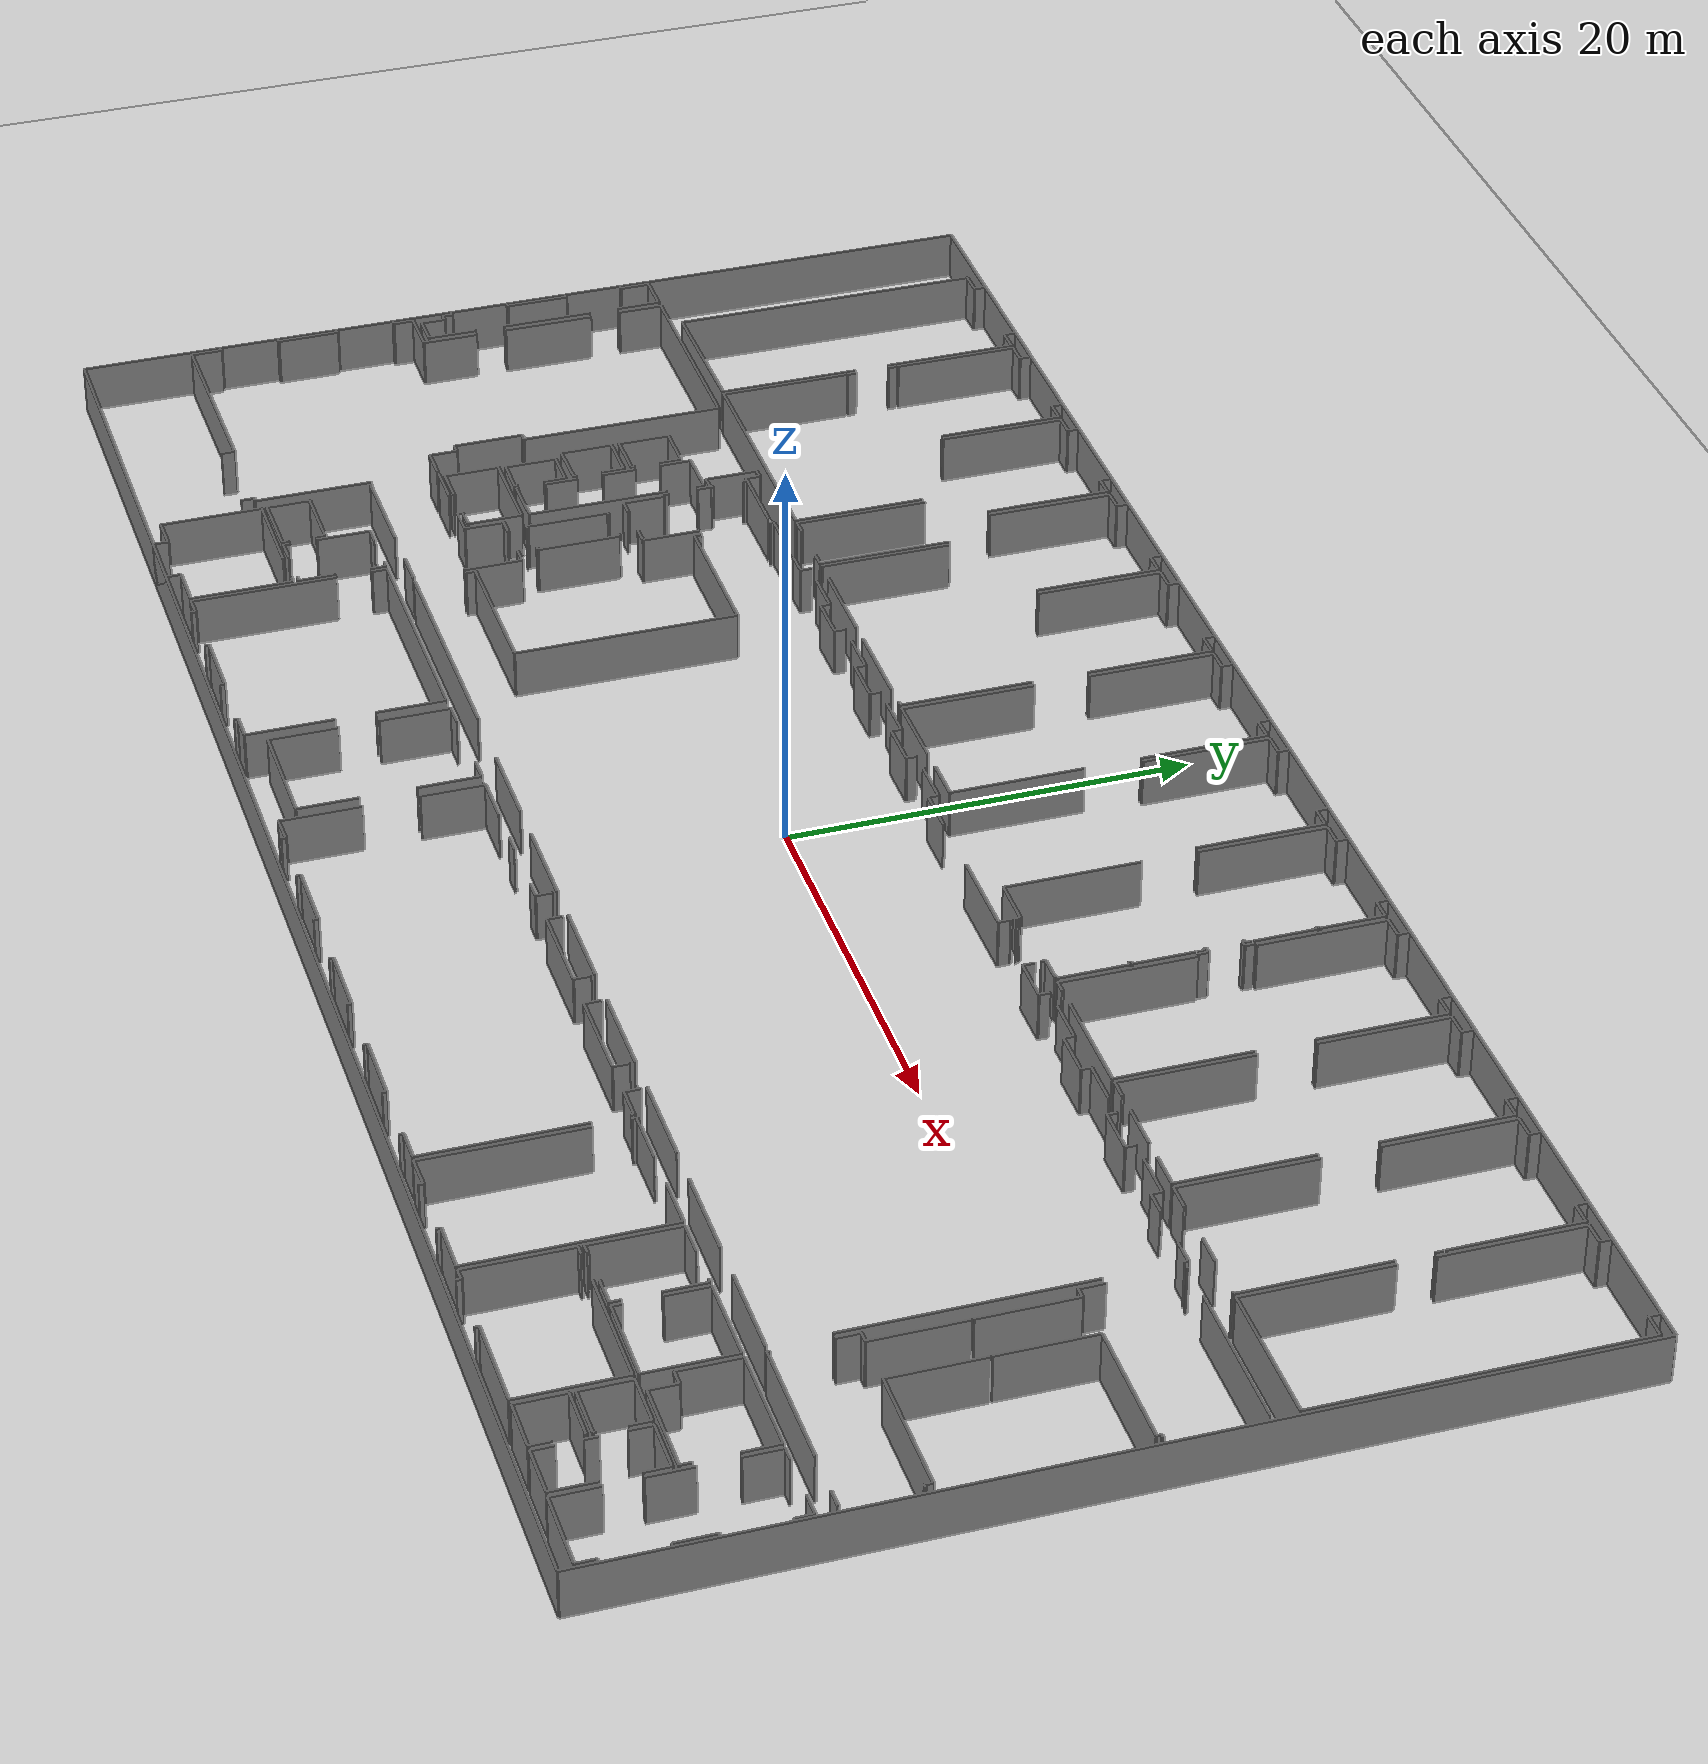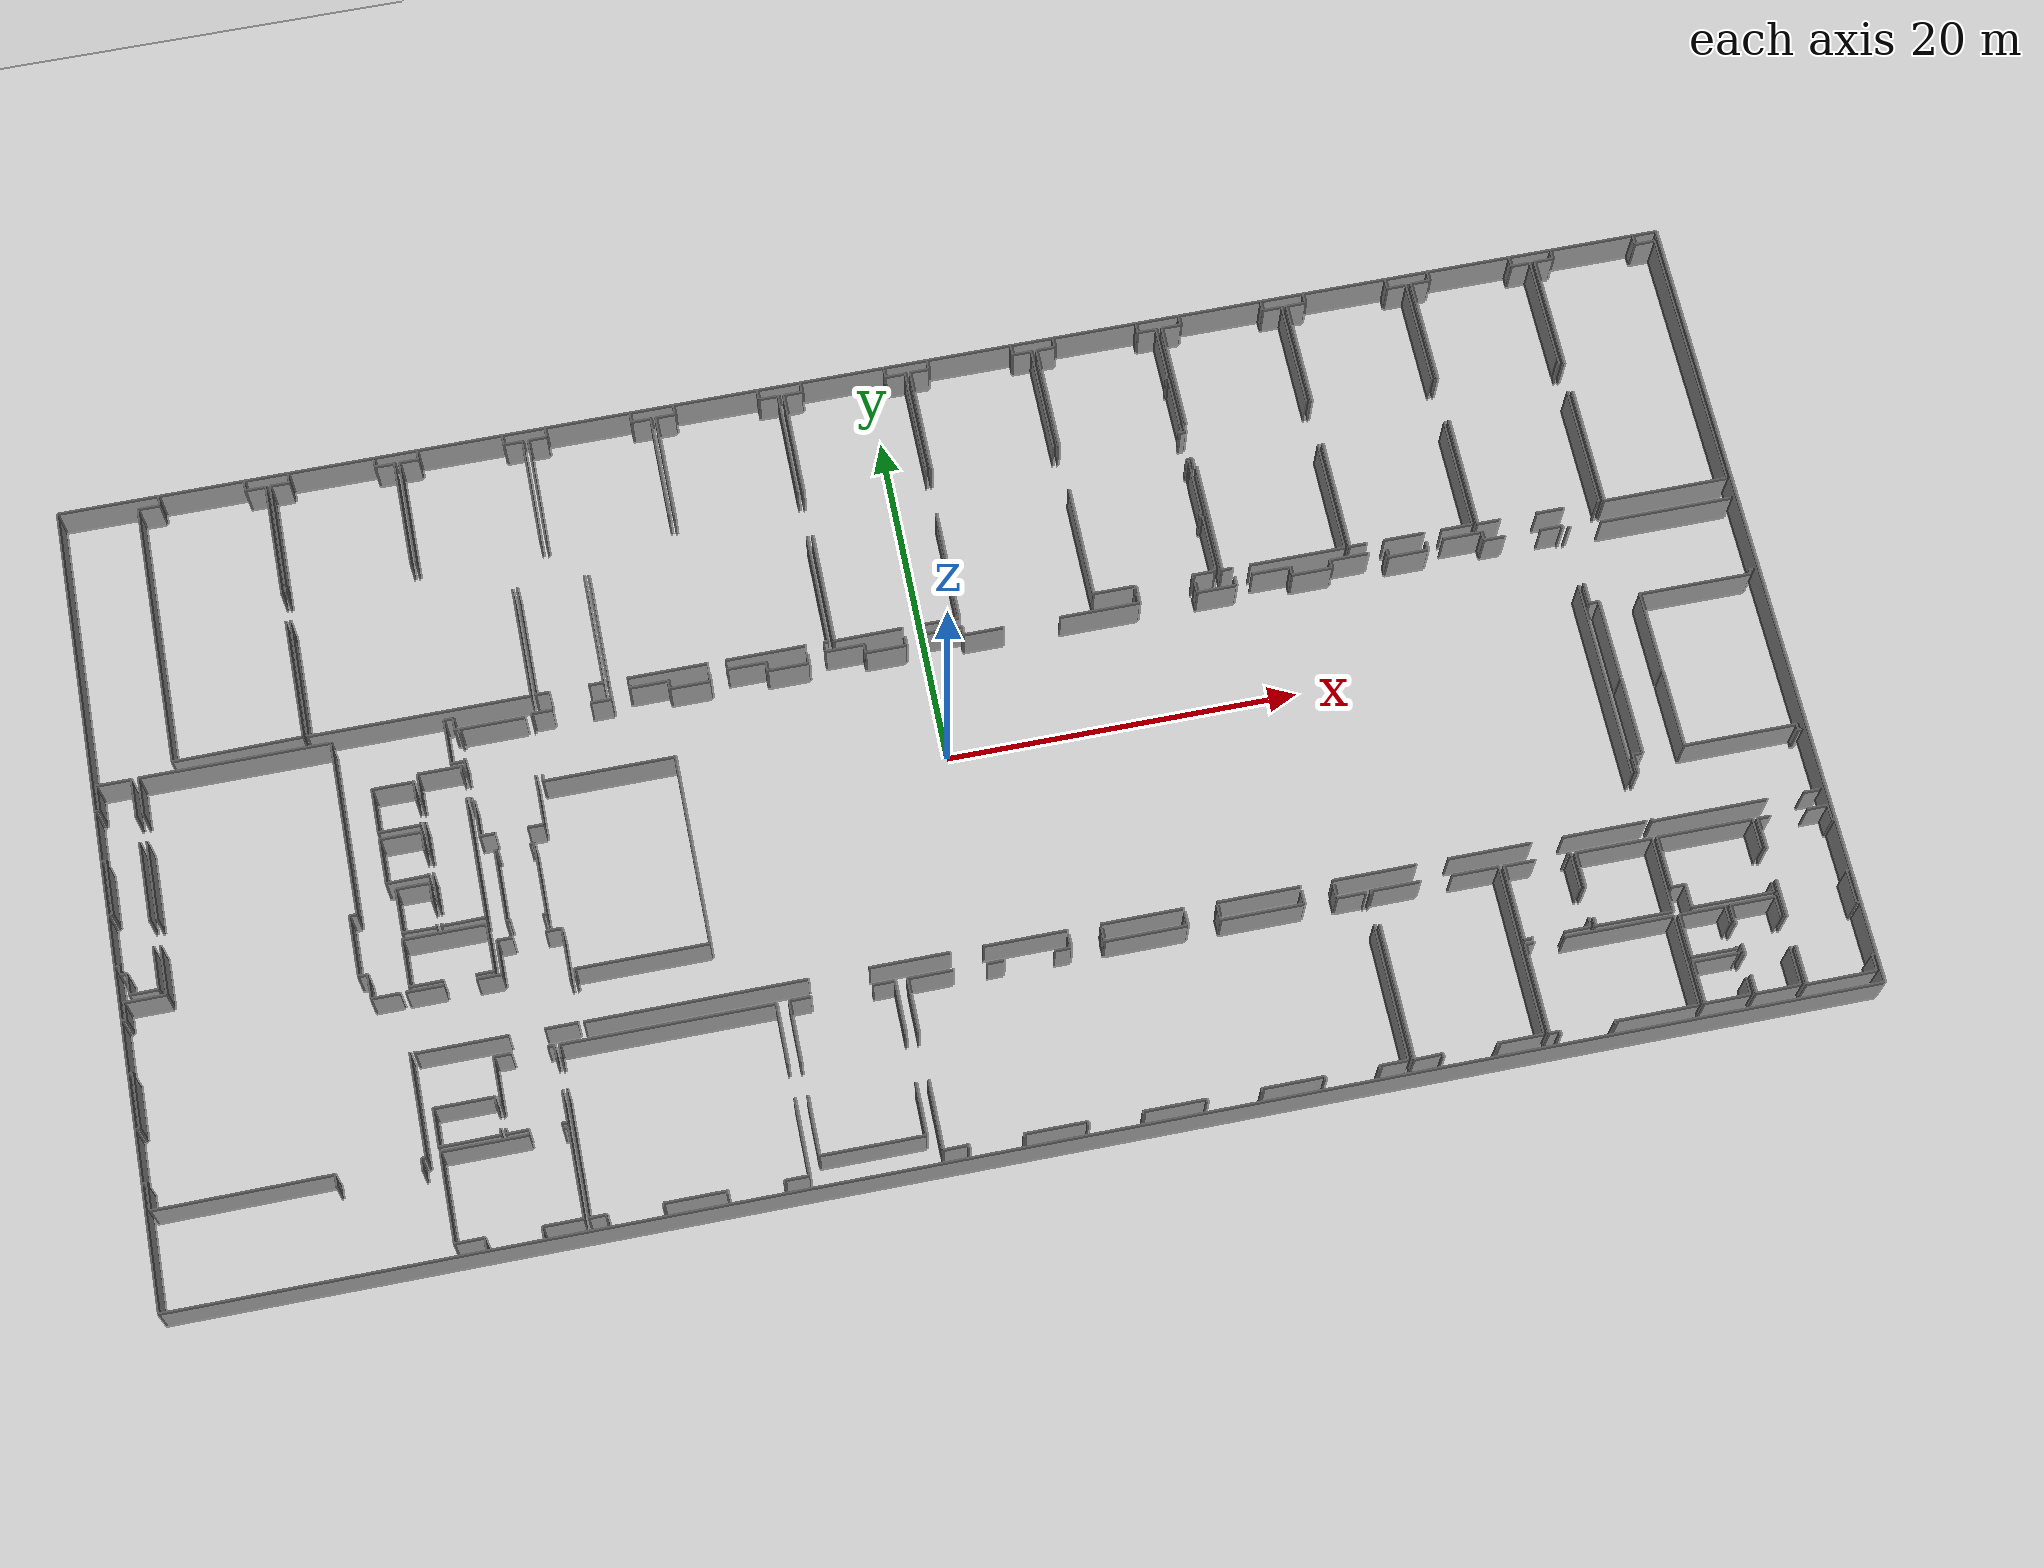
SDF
<sdf version="1.6">
  <world name="default">
    <light name="sun" type="directional">
      <cast_shadows>1</cast_shadows>
      <pose frame="">0 0 10 0 -0 0</pose>
      <diffuse>0.8 0.8 0.8 1</diffuse>
      <specular>0.1 0.1 0.1 1</specular>
      <attenuation>
        <range>1000</range>
        <constant>0.9</constant>
        <linear>0.01</linear>
        <quadratic>0.001</quadratic>
      </attenuation>
      <direction>-0.5 0.5 -1</direction>
    </light>
    <model name="ground_plane">
      <static>1</static>
      <link name="link">
        <collision name="collision">
          <geometry>
            <plane>
              <normal>0 0 1</normal>
              <size>100 100</size>
            </plane>
          </geometry>
          <surface>
            <friction>
              <ode>
                <mu>100</mu>
                <mu2>50</mu2>
              </ode>
              <torsional>
                <ode />
              </torsional>
            </friction>
            <contact>
              <ode />
            </contact>
            <bounce />
          </surface>
          <max_contacts>10</max_contacts>
        </collision>
        <visual name="visual">
          <cast_shadows>0</cast_shadows>
          <geometry>
            <plane>
              <normal>0 0 1</normal>
              <size>100 100</size>
            </plane>
          </geometry>
          <material>
            <script>
              <uri>file://media/materials/scripts/gazebo.material</uri>
              <name>Gazebo/Grey</name>
            </script>
          </material>
        </visual>
        <self_collide>0</self_collide>
        <kinematic>0</kinematic>
        <gravity>1</gravity>
      </link>
    </model>
    <gravity>0 0 -9.8</gravity>
    <magnetic_field>6e-06 2.3e-05 -4.2e-05</magnetic_field>
    <atmosphere type="adiabatic" />
    <physics default="0" name="default_physics" type="ode">
      <max_step_size>0.001</max_step_size>
      <real_time_factor>1</real_time_factor>
      <real_time_update_rate>1000</real_time_update_rate>
    </physics>
    <scene>
      <ambient>0.4 0.4 0.4 1</ambient>
      <background>0.7 0.7 0.7 1</background>
      <shadows>1</shadows>
    </scene>
    <spherical_coordinates>
      <surface_model>EARTH_WGS84</surface_model>
      <latitude_deg>0</latitude_deg>
      <longitude_deg>0</longitude_deg>
      <elevation>0</elevation>
      <heading_deg>0</heading_deg>
    </spherical_coordinates>
  <model name="50045229">
		<static>1</static>
		<link name="Wall_0">
			<collision name="Wall_0_Collision">
				<geometry>
					<box>
						<size>15.8074096638 0.1 2.5</size>
					</box>
				</geometry>
				<pose frame="">7.90370483189 0 1.25 0 0 0</pose>
			</collision>
			<visual name="Wall_0_Visual">
				<pose frame="">7.90370483189 0 1.25 0 0 0</pose>
				<geometry>
					<box>
						<size>15.8074096638 0.1 2.5</size>
					</box>
				</geometry>
				<material>
					<script>
						<uri>file://media/materials/scripts/gazebo.material</uri>
						<name>Gazebo/Grey</name>
					</script>
					<ambient>1 1 1 1</ambient>
				</material>
			</visual>
			<pose frame="">4.53489700339 -16.4062242191 0 0 0 1.57079632679</pose>
		</link>
		<link name="Wall_1">
			<collision name="Wall_1_Collision">
				<geometry>
					<box>
						<size>1.24471690211 0.1 2.5</size>
					</box>
				</geometry>
				<pose frame="">0.622358451053 0 1.25 0 0 0</pose>
			</collision>
			<visual name="Wall_1_Visual">
				<pose frame="">0.622358451053 0 1.25 0 0 0</pose>
				<geometry>
					<box>
						<size>1.24471690211 0.1 2.5</size>
					</box>
				</geometry>
				<material>
					<script>
						<uri>file://media/materials/scripts/gazebo.material</uri>
						<name>Gazebo/Grey</name>
					</script>
					<ambient>1 1 1 1</ambient>
				</material>
			</visual>
			<pose frame="">4.53489700339 -0.598814555331 0 0 0 0.0</pose>
		</link>
		<link name="Wall_2">
			<collision name="Wall_2_Collision">
				<geometry>
					<box>
						<size>0.562895835713 0.1 2.5</size>
					</box>
				</geometry>
				<pose frame="">0.281447917857 0 1.25 0 0 0</pose>
			</collision>
			<visual name="Wall_2_Visual">
				<pose frame="">0.281447917857 0 1.25 0 0 0</pose>
				<geometry>
					<box>
						<size>0.562895835713 0.1 2.5</size>
					</box>
				</geometry>
				<material>
					<script>
						<uri>file://media/materials/scripts/gazebo.material</uri>
						<name>Gazebo/Grey</name>
					</script>
					<ambient>1 1 1 1</ambient>
				</material>
			</visual>
			<pose frame="">5.77961390549 -0.598814555331 0 0 0 1.57079632679</pose>
		</link>
		<link name="Wall_3">
			<collision name="Wall_3_Collision">
				<geometry>
					<box>
						<size>0.573937986267 0.1 2.5</size>
					</box>
				</geometry>
				<pose frame="">0.286968993134 0 1.25 0 0 0</pose>
			</collision>
			<visual name="Wall_3_Visual">
				<pose frame="">0.286968993134 0 1.25 0 0 0</pose>
				<geometry>
					<box>
						<size>0.573937986267 0.1 2.5</size>
					</box>
				</geometry>
				<material>
					<script>
						<uri>file://media/materials/scripts/gazebo.material</uri>
						<name>Gazebo/Grey</name>
					</script>
					<ambient>1 1 1 1</ambient>
				</material>
			</visual>
			<pose frame="">10.6908324766 -0.0359187196182 0 0 0 -1.57079632679</pose>
		</link>
		<link name="Wall_4">
			<collision name="Wall_4_Collision">
				<geometry>
					<box>
						<size>1.15891812309 0.1 2.5</size>
					</box>
				</geometry>
				<pose frame="">0.579459061544 0 1.25 0 0 0</pose>
			</collision>
			<visual name="Wall_4_Visual">
				<pose frame="">0.579459061544 0 1.25 0 0 0</pose>
				<geometry>
					<box>
						<size>1.15891812309 0.1 2.5</size>
					</box>
				</geometry>
				<material>
					<script>
						<uri>file://media/materials/scripts/gazebo.material</uri>
						<name>Gazebo/Grey</name>
					</script>
					<ambient>1 1 1 1</ambient>
				</material>
			</visual>
			<pose frame="">10.6908324766 -0.609856705885 0 0 0 0.0</pose>
		</link>
		<link name="Wall_5">
			<collision name="Wall_5_Collision">
				<geometry>
					<box>
						<size>6.79638020536 0.1 2.5</size>
					</box>
				</geometry>
				<pose frame="">3.39819010268 0 1.25 0 0 0</pose>
			</collision>
			<visual name="Wall_5_Visual">
				<pose frame="">3.39819010268 0 1.25 0 0 0</pose>
				<geometry>
					<box>
						<size>6.79638020536 0.1 2.5</size>
					</box>
				</geometry>
				<material>
					<script>
						<uri>file://media/materials/scripts/gazebo.material</uri>
						<name>Gazebo/Grey</name>
					</script>
					<ambient>1 1 1 1</ambient>
				</material>
			</visual>
			<pose frame="">11.8497505997 -0.609856705885 0 0 0 -1.57079632679</pose>
		</link>
		<link name="Wall_6">
			<collision name="Wall_6_Collision">
				<geometry>
					<box>
						<size>7.14858673165 0.1 2.5</size>
					</box>
				</geometry>
				<pose frame="">3.57429336583 0 1.25 0 0 0</pose>
			</collision>
			<visual name="Wall_6_Visual">
				<pose frame="">3.57429336583 0 1.25 0 0 0</pose>
				<geometry>
					<box>
						<size>7.14858673165 0.1 2.5</size>
					</box>
				</geometry>
				<material>
					<script>
						<uri>file://media/materials/scripts/gazebo.material</uri>
						<name>Gazebo/Grey</name>
					</script>
					<ambient>1 1 1 1</ambient>
				</material>
			</visual>
			<pose frame="">11.8497505997 -9.18846539492 0 0 0 -1.57079632679</pose>
		</link>
		<link name="Wall_7">
			<collision name="Wall_7_Collision">
				<geometry>
					<box>
						<size>7.31518064807 0.1 2.5</size>
					</box>
				</geometry>
				<pose frame="">3.65759032404 0 1.25 0 0 0</pose>
			</collision>
			<visual name="Wall_7_Visual">
				<pose frame="">3.65759032404 0 1.25 0 0 0</pose>
				<geometry>
					<box>
						<size>7.31518064807 0.1 2.5</size>
					</box>
				</geometry>
				<material>
					<script>
						<uri>file://media/materials/scripts/gazebo.material</uri>
						<name>Gazebo/Grey</name>
					</script>
					<ambient>1 1 1 1</ambient>
				</material>
			</visual>
			<pose frame="">11.8497505997 -16.3370521266 0 0 0 -3.13213654762</pose>
		</link>
		<link name="Wall_8">
			<collision name="Wall_8_Collision">
				<geometry>
					<box>
						<size>0.4605972915 0.1 2.5</size>
					</box>
				</geometry>
				<pose frame="">0.23029864575 0 1.25 0 0 0</pose>
			</collision>
			<visual name="Wall_8_Visual">
				<pose frame="">0.23029864575 0 1.25 0 0 0</pose>
				<geometry>
					<box>
						<size>0.4605972915 0.1 2.5</size>
					</box>
				</geometry>
				<material>
					<script>
						<uri>file://media/materials/scripts/gazebo.material</uri>
						<name>Gazebo/Grey</name>
					</script>
					<ambient>1 1 1 1</ambient>
				</material>
			</visual>
			<pose frame="">12.0963586287 -9.66277018366 0 0 0 1.57079632679</pose>
		</link>
		<link name="Wall_9">
			<collision name="Wall_9_Collision">
				<geometry>
					<box>
						<size>0.437878384038 0.1 2.5</size>
					</box>
				</geometry>
				<pose frame="">0.218939192019 0 1.25 0 0 0</pose>
			</collision>
			<visual name="Wall_9_Visual">
				<pose frame="">0.218939192019 0 1.25 0 0 0</pose>
				<geometry>
					<box>
						<size>0.437878384038 0.1 2.5</size>
					</box>
				</geometry>
				<material>
					<script>
						<uri>file://media/materials/scripts/gazebo.material</uri>
						<name>Gazebo/Grey</name>
					</script>
					<ambient>1 1 1 1</ambient>
				</material>
			</visual>
			<pose frame="">12.0963586287 -7.44431329246 0 0 0 1.57079632679</pose>
		</link>
		<link name="Wall_10">
			<collision name="Wall_10_Collision">
				<geometry>
					<box>
						<size>0.32428384673 0.1 2.5</size>
					</box>
				</geometry>
				<pose frame="">0.162141923365 0 1.25 0 0 0</pose>
			</collision>
			<visual name="Wall_10_Visual">
				<pose frame="">0.162141923365 0 1.25 0 0 0</pose>
				<geometry>
					<box>
						<size>0.32428384673 0.1 2.5</size>
					</box>
				</geometry>
				<material>
					<script>
						<uri>file://media/materials/scripts/gazebo.material</uri>
						<name>Gazebo/Grey</name>
					</script>
					<ambient>1 1 1 1</ambient>
				</material>
			</visual>
			<pose frame="">63.8438106842 -7.00643490843 0 0 0 -1.57079632679</pose>
		</link>
		<link name="Wall_11">
			<collision name="Wall_11_Collision">
				<geometry>
					<box>
						<size>0.143928721014 0.1 2.5</size>
					</box>
				</geometry>
				<pose frame="">0.0719643605072 0 1.25 0 0 0</pose>
			</collision>
			<visual name="Wall_11_Visual">
				<pose frame="">0.0719643605072 0 1.25 0 0 0</pose>
				<geometry>
					<box>
						<size>0.143928721014 0.1 2.5</size>
					</box>
				</geometry>
				<material>
					<script>
						<uri>file://media/materials/scripts/gazebo.material</uri>
						<name>Gazebo/Grey</name>
					</script>
					<ambient>1 1 1 1</ambient>
				</material>
			</visual>
			<pose frame="">63.8438106842 -7.33071875516 0 0 0 3.14159265359</pose>
		</link>
		<link name="Wall_12">
			<collision name="Wall_12_Collision">
				<geometry>
					<box>
						<size>0.115117592557 0.1 2.5</size>
					</box>
				</geometry>
				<pose frame="">0.0575587962787 0 1.25 0 0 0</pose>
			</collision>
			<visual name="Wall_12_Visual">
				<pose frame="">0.0575587962787 0 1.25 0 0 0</pose>
				<geometry>
					<box>
						<size>0.115117592557 0.1 2.5</size>
					</box>
				</geometry>
				<material>
					<script>
						<uri>file://media/materials/scripts/gazebo.material</uri>
						<name>Gazebo/Grey</name>
					</script>
					<ambient>1 1 1 1</ambient>
				</material>
			</visual>
			<pose frame="">63.6998819632 -7.33071875516 0 0 0 -1.57079632679</pose>
		</link>
		<link name="Wall_13">
			<collision name="Wall_13_Collision">
				<geometry>
					<box>
						<size>0.345479698943 0.1 2.5</size>
					</box>
				</geometry>
				<pose frame="">0.172739849471 0 1.25 0 0 0</pose>
			</collision>
			<visual name="Wall_13_Visual">
				<pose frame="">0.172739849471 0 1.25 0 0 0</pose>
				<geometry>
					<box>
						<size>0.345479698943 0.1 2.5</size>
					</box>
				</geometry>
				<material>
					<script>
						<uri>file://media/materials/scripts/gazebo.material</uri>
						<name>Gazebo/Grey</name>
					</script>
					<ambient>1 1 1 1</ambient>
				</material>
			</visual>
			<pose frame="">63.6998819632 -7.44583634771 0 0 0 0.0</pose>
		</link>
		<link name="Wall_14">
			<collision name="Wall_14_Collision">
				<geometry>
					<box>
						<size>0.451078196195 0.1 2.5</size>
					</box>
				</geometry>
				<pose frame="">0.225539098097 0 1.25 0 0 0</pose>
			</collision>
			<visual name="Wall_14_Visual">
				<pose frame="">0.225539098097 0 1.25 0 0 0</pose>
				<geometry>
					<box>
						<size>0.451078196195 0.1 2.5</size>
					</box>
				</geometry>
				<material>
					<script>
						<uri>file://media/materials/scripts/gazebo.material</uri>
						<name>Gazebo/Grey</name>
					</script>
					<ambient>1 1 1 1</ambient>
				</material>
			</visual>
			<pose frame="">64.0453616622 -7.44583634771 0 0 0 1.57079632679</pose>
		</link>
		<link name="Wall_15">
			<collision name="Wall_15_Collision">
				<geometry>
					<box>
						<size>0.431913084314 0.1 2.5</size>
					</box>
				</geometry>
				<pose frame="">0.215956542157 0 1.25 0 0 0</pose>
			</collision>
			<visual name="Wall_15_Visual">
				<pose frame="">0.215956542157 0 1.25 0 0 0</pose>
				<geometry>
					<box>
						<size>0.431913084314 0.1 2.5</size>
					</box>
				</geometry>
				<material>
					<script>
						<uri>file://media/materials/scripts/gazebo.material</uri>
						<name>Gazebo/Grey</name>
					</script>
					<ambient>1 1 1 1</ambient>
				</material>
			</visual>
			<pose frame="">86.2049270837 -6.99475815152 0 0 0 -1.57079632679</pose>
		</link>
		<link name="Wall_16">
			<collision name="Wall_16_Collision">
				<geometry>
					<box>
						<size>7.16381728414 0.1 2.5</size>
					</box>
				</geometry>
				<pose frame="">3.58190864207 0 1.25 0 0 0</pose>
			</collision>
			<visual name="Wall_16_Visual">
				<pose frame="">3.58190864207 0 1.25 0 0 0</pose>
				<geometry>
					<box>
						<size>7.16381728414 0.1 2.5</size>
					</box>
				</geometry>
				<material>
					<script>
						<uri>file://media/materials/scripts/gazebo.material</uri>
						<name>Gazebo/Grey</name>
					</script>
					<ambient>1 1 1 1</ambient>
				</material>
			</visual>
			<pose frame="">86.2049270837 -9.20737666426 0 0 0 -1.57079632679</pose>
		</link>
		<link name="Wall_17">
			<collision name="Wall_17_Collision">
				<geometry>
					<box>
						<size>0.134282704438 0.1 2.5</size>
					</box>
				</geometry>
				<pose frame="">0.0671413522192 0 1.25 0 0 0</pose>
			</collision>
			<visual name="Wall_17_Visual">
				<pose frame="">0.0671413522192 0 1.25 0 0 0</pose>
				<geometry>
					<box>
						<size>0.134282704438 0.1 2.5</size>
					</box>
				</geometry>
				<material>
					<script>
						<uri>file://media/materials/scripts/gazebo.material</uri>
						<name>Gazebo/Grey</name>
					</script>
					<ambient>1 1 1 1</ambient>
				</material>
			</visual>
			<pose frame="">86.2049270837 -16.3711939484 0 0 0 3.14159265359</pose>
		</link>
		<link name="Wall_18">
			<collision name="Wall_18_Collision">
				<geometry>
					<box>
						<size>1.5865158842 0.1 2.5</size>
					</box>
				</geometry>
				<pose frame="">0.793257942099 0 1.25 0 0 0</pose>
			</collision>
			<visual name="Wall_18_Visual">
				<pose frame="">0.793257942099 0 1.25 0 0 0</pose>
				<geometry>
					<box>
						<size>1.5865158842 0.1 2.5</size>
					</box>
				</geometry>
				<material>
					<script>
						<uri>file://media/materials/scripts/gazebo.material</uri>
						<name>Gazebo/Grey</name>
					</script>
					<ambient>1 1 1 1</ambient>
				</material>
			</visual>
			<pose frame="">84.0872456815 -16.3711939484 0 0 0 3.14159265359</pose>
		</link>
		<link name="Wall_19">
			<collision name="Wall_19_Collision">
				<geometry>
					<box>
						<size>1.31998121565 0.1 2.5</size>
					</box>
				</geometry>
				<pose frame="">0.659990607826 0 1.25 0 0 0</pose>
			</collision>
			<visual name="Wall_19_Visual">
				<pose frame="">0.659990607826 0 1.25 0 0 0</pose>
				<geometry>
					<box>
						<size>1.31998121565 0.1 2.5</size>
					</box>
				</geometry>
				<material>
					<script>
						<uri>file://media/materials/scripts/gazebo.material</uri>
						<name>Gazebo/Grey</name>
					</script>
					<ambient>1 1 1 1</ambient>
				</material>
			</visual>
			<pose frame="">80.3557603219 -16.3711939484 0 0 0 3.14159265359</pose>
		</link>
		<link name="Wall_20">
			<collision name="Wall_20_Collision">
				<geometry>
					<box>
						<size>6.68925865286 0.1 2.5</size>
					</box>
				</geometry>
				<pose frame="">3.34462932643 0 1.25 0 0 0</pose>
			</collision>
			<visual name="Wall_20_Visual">
				<pose frame="">3.34462932643 0 1.25 0 0 0</pose>
				<geometry>
					<box>
						<size>6.68925865286 0.1 2.5</size>
					</box>
				</geometry>
				<material>
					<script>
						<uri>file://media/materials/scripts/gazebo.material</uri>
						<name>Gazebo/Grey</name>
					</script>
					<ambient>1 1 1 1</ambient>
				</material>
			</visual>
			<pose frame="">79.0357791062 -16.3711939484 0 0 0 1.57079632679</pose>
		</link>
		<link name="Wall_21">
			<collision name="Wall_21_Collision">
				<geometry>
					<box>
						<size>0.509461980733 0.1 2.5</size>
					</box>
				</geometry>
				<pose frame="">0.254730990367 0 1.25 0 0 0</pose>
			</collision>
			<visual name="Wall_21_Visual">
				<pose frame="">0.254730990367 0 1.25 0 0 0</pose>
				<geometry>
					<box>
						<size>0.509461980733 0.1 2.5</size>
					</box>
				</geometry>
				<material>
					<script>
						<uri>file://media/materials/scripts/gazebo.material</uri>
						<name>Gazebo/Grey</name>
					</script>
					<ambient>1 1 1 1</ambient>
				</material>
			</visual>
			<pose frame="">64.0317810862 -9.68193529554 0 0 0 1.57079632679</pose>
		</link>
		<link name="Wall_22">
			<collision name="Wall_22_Collision">
				<geometry>
					<box>
						<size>0.311972483469 0.1 2.5</size>
					</box>
				</geometry>
				<pose frame="">0.155986241734 0 1.25 0 0 0</pose>
			</collision>
			<visual name="Wall_22_Visual">
				<pose frame="">0.155986241734 0 1.25 0 0 0</pose>
				<geometry>
					<box>
						<size>0.311972483469 0.1 2.5</size>
					</box>
				</geometry>
				<material>
					<script>
						<uri>file://media/materials/scripts/gazebo.material</uri>
						<name>Gazebo/Grey</name>
					</script>
					<ambient>1 1 1 1</ambient>
				</material>
			</visual>
			<pose frame="">64.0317810862 -9.1724733148 0 0 0 3.14159265359</pose>
		</link>
		<link name="Wall_23">
			<collision name="Wall_23_Collision">
				<geometry>
					<box>
						<size>0.116132962723 0.1 2.5</size>
					</box>
				</geometry>
				<pose frame="">0.0580664813616 0 1.25 0 0 0</pose>
			</collision>
			<visual name="Wall_23_Visual">
				<pose frame="">0.0580664813616 0 1.25 0 0 0</pose>
				<geometry>
					<box>
						<size>0.116132962723 0.1 2.5</size>
					</box>
				</geometry>
				<material>
					<script>
						<uri>file://media/materials/scripts/gazebo.material</uri>
						<name>Gazebo/Grey</name>
					</script>
					<ambient>1 1 1 1</ambient>
				</material>
			</visual>
			<pose frame="">63.7198086027 -9.1724733148 0 0 0 -1.57079632679</pose>
		</link>
		<link name="Wall_24">
			<collision name="Wall_24_Collision">
				<geometry>
					<box>
						<size>0.130601987587 0.1 2.5</size>
					</box>
				</geometry>
				<pose frame="">0.0653009937935 0 1.25 0 0 0</pose>
			</collision>
			<visual name="Wall_24_Visual">
				<pose frame="">0.0653009937935 0 1.25 0 0 0</pose>
				<geometry>
					<box>
						<size>0.130601987587 0.1 2.5</size>
					</box>
				</geometry>
				<material>
					<script>
						<uri>file://media/materials/scripts/gazebo.material</uri>
						<name>Gazebo/Grey</name>
					</script>
					<ambient>1 1 1 1</ambient>
				</material>
			</visual>
			<pose frame="">63.7198086027 -9.28860627753 0 0 0 0.0</pose>
		</link>
		<link name="Wall_25">
			<collision name="Wall_25_Collision">
				<geometry>
					<box>
						<size>0.341037454467 0.1 2.5</size>
					</box>
				</geometry>
				<pose frame="">0.170518727233 0 1.25 0 0 0</pose>
			</collision>
			<visual name="Wall_25_Visual">
				<pose frame="">0.170518727233 0 1.25 0 0 0</pose>
				<geometry>
					<box>
						<size>0.341037454467 0.1 2.5</size>
					</box>
				</geometry>
				<material>
					<script>
						<uri>file://media/materials/scripts/gazebo.material</uri>
						<name>Gazebo/Grey</name>
					</script>
					<ambient>1 1 1 1</ambient>
				</material>
			</visual>
			<pose frame="">63.8504105903 -9.28860627753 0 0 0 -1.57079632679</pose>
		</link>
		<link name="Wall_26">
			<collision name="Wall_26_Collision">
				<geometry>
					<box>
						<size>6.7198466791 0.1 2.5</size>
					</box>
				</geometry>
				<pose frame="">3.35992333955 0 1.25 0 0 0</pose>
			</collision>
			<visual name="Wall_26_Visual">
				<pose frame="">3.35992333955 0 1.25 0 0 0</pose>
				<geometry>
					<box>
						<size>6.7198466791 0.1 2.5</size>
					</box>
				</geometry>
				<material>
					<script>
						<uri>file://media/materials/scripts/gazebo.material</uri>
						<name>Gazebo/Grey</name>
					</script>
					<ambient>1 1 1 1</ambient>
				</material>
			</visual>
			<pose frame="">28.746906294 -9.62964373199 0 0 0 -1.57079632679</pose>
		</link>
		<link name="Wall_27">
			<collision name="Wall_27_Collision">
				<geometry>
					<box>
						<size>0.831968929673 0.1 2.5</size>
					</box>
				</geometry>
				<pose frame="">0.415984464836 0 1.25 0 0 0</pose>
			</collision>
			<visual name="Wall_27_Visual">
				<pose frame="">0.415984464836 0 1.25 0 0 0</pose>
				<geometry>
					<box>
						<size>0.831968929673 0.1 2.5</size>
					</box>
				</geometry>
				<material>
					<script>
						<uri>file://media/materials/scripts/gazebo.material</uri>
						<name>Gazebo/Grey</name>
					</script>
					<ambient>1 1 1 1</ambient>
				</material>
			</visual>
			<pose frame="">28.746906294 -16.3494904111 0 0 0 3.14159265359</pose>
		</link>
		<link name="Wall_28">
			<collision name="Wall_28_Collision">
				<geometry>
					<box>
						<size>0.786911878562 0.1 2.5</size>
					</box>
				</geometry>
				<pose frame="">0.393455939281 0 1.25 0 0 0</pose>
			</collision>
			<visual name="Wall_28_Visual">
				<pose frame="">0.393455939281 0 1.25 0 0 0</pose>
				<geometry>
					<box>
						<size>0.786911878562 0.1 2.5</size>
					</box>
				</geometry>
				<material>
					<script>
						<uri>file://media/materials/scripts/gazebo.material</uri>
						<name>Gazebo/Grey</name>
					</script>
					<ambient>1 1 1 1</ambient>
				</material>
			</visual>
			<pose frame="">25.7049841983 -16.3494904111 0 0 0 3.14159265359</pose>
		</link>
		<link name="Wall_29">
			<collision name="Wall_29_Collision">
				<geometry>
					<box>
						<size>6.68456256584 0.1 2.5</size>
					</box>
				</geometry>
				<pose frame="">3.34228128292 0 1.25 0 0 0</pose>
			</collision>
			<visual name="Wall_29_Visual">
				<pose frame="">3.34228128292 0 1.25 0 0 0</pose>
				<geometry>
					<box>
						<size>6.68456256584 0.1 2.5</size>
					</box>
				</geometry>
				<material>
					<script>
						<uri>file://media/materials/scripts/gazebo.material</uri>
						<name>Gazebo/Grey</name>
					</script>
					<ambient>1 1 1 1</ambient>
				</material>
			</visual>
			<pose frame="">24.9180723197 -16.3494904111 0 0 0 1.57079632679</pose>
		</link>
		<link name="Wall_30">
			<collision name="Wall_30_Collision">
				<geometry>
					<box>
						<size>6.31687164452 0.1 2.5</size>
					</box>
				</geometry>
				<pose frame="">3.15843582226 0 1.25 0 0 0</pose>
			</collision>
			<visual name="Wall_30_Visual">
				<pose frame="">3.15843582226 0 1.25 0 0 0</pose>
				<geometry>
					<box>
						<size>6.31687164452 0.1 2.5</size>
					</box>
				</geometry>
				<material>
					<script>
						<uri>file://media/materials/scripts/gazebo.material</uri>
						<name>Gazebo/Grey</name>
					</script>
					<ambient>1 1 1 1</ambient>
				</material>
			</visual>
			<pose frame="">12.1024508497 -6.91568619985 0 0 0 1.57079632679</pose>
		</link>
		<link name="Wall_31">
			<collision name="Wall_31_Collision">
				<geometry>
					<box>
						<size>1.10472274048 0.1 2.5</size>
					</box>
				</geometry>
				<pose frame="">0.552361370242 0 1.25 0 0 0</pose>
			</collision>
			<visual name="Wall_31_Visual">
				<pose frame="">0.552361370242 0 1.25 0 0 0</pose>
				<geometry>
					<box>
						<size>1.10472274048 0.1 2.5</size>
					</box>
				</geometry>
				<material>
					<script>
						<uri>file://media/materials/scripts/gazebo.material</uri>
						<name>Gazebo/Grey</name>
					</script>
					<ambient>1 1 1 1</ambient>
				</material>
			</visual>
			<pose frame="">12.1024508497 -0.598814555331 0 0 0 0.0</pose>
		</link>
		<link name="Wall_32">
			<collision name="Wall_32_Collision">
				<geometry>
					<box>
						<size>0.562895835713 0.1 2.5</size>
					</box>
				</geometry>
				<pose frame="">0.281447917857 0 1.25 0 0 0</pose>
			</collision>
			<visual name="Wall_32_Visual">
				<pose frame="">0.281447917857 0 1.25 0 0 0</pose>
				<geometry>
					<box>
						<size>0.562895835713 0.1 2.5</size>
					</box>
				</geometry>
				<material>
					<script>
						<uri>file://media/materials/scripts/gazebo.material</uri>
						<name>Gazebo/Grey</name>
					</script>
					<ambient>1 1 1 1</ambient>
				</material>
			</visual>
			<pose frame="">13.2071735902 -0.598814555331 0 0 0 1.57079632679</pose>
		</link>
		<link name="Wall_33">
			<collision name="Wall_33_Collision">
				<geometry>
					<box>
						<size>0.538400030461 0.1 2.5</size>
					</box>
				</geometry>
				<pose frame="">0.269200015231 0 1.25 0 0 0</pose>
			</collision>
			<visual name="Wall_33_Visual">
				<pose frame="">0.269200015231 0 1.25 0 0 0</pose>
				<geometry>
					<box>
						<size>0.538400030461 0.1 2.5</size>
					</box>
				</geometry>
				<material>
					<script>
						<uri>file://media/materials/scripts/gazebo.material</uri>
						<name>Gazebo/Grey</name>
					</script>
					<ambient>1 1 1 1</ambient>
				</material>
			</visual>
			<pose frame="">18.1521532194 -0.0359187196182 0 0 0 -1.57079632679</pose>
		</link>
		<link name="Wall_34">
			<collision name="Wall_34_Collision">
				<geometry>
					<box>
						<size>1.10358044905 0.1 2.5</size>
					</box>
				</geometry>
				<pose frame="">0.551790224524 0 1.25 0 0 0</pose>
			</collision>
			<visual name="Wall_34_Visual">
				<pose frame="">0.551790224524 0 1.25 0 0 0</pose>
				<geometry>
					<box>
						<size>1.10358044905 0.1 2.5</size>
					</box>
				</geometry>
				<material>
					<script>
						<uri>file://media/materials/scripts/gazebo.material</uri>
						<name>Gazebo/Grey</name>
					</script>
					<ambient>1 1 1 1</ambient>
				</material>
			</visual>
			<pose frame="">18.1521532194 -0.574318750079 0 0 0 0.0</pose>
		</link>
		<link name="Wall_35">
			<collision name="Wall_35_Collision">
				<geometry>
					<box>
						<size>6.33667136275 0.1 2.5</size>
					</box>
				</geometry>
				<pose frame="">3.16833568138 0 1.25 0 0 0</pose>
			</collision>
			<visual name="Wall_35_Visual">
				<pose frame="">3.16833568138 0 1.25 0 0 0</pose>
				<geometry>
					<box>
						<size>6.33667136275 0.1 2.5</size>
					</box>
				</geometry>
				<material>
					<script>
						<uri>file://media/materials/scripts/gazebo.material</uri>
						<name>Gazebo/Grey</name>
					</script>
					<ambient>1 1 1 1</ambient>
				</material>
			</visual>
			<pose frame="">19.2557336684 -0.574318750079 0 0 0 -1.57079632679</pose>
		</link>
		<link name="Wall_36">
			<collision name="Wall_36_Collision">
				<geometry>
					<box>
						<size>6.35494802574 0.1 2.5</size>
					</box>
				</geometry>
				<pose frame="">3.17747401287 0 1.25 0 0 0</pose>
			</collision>
			<visual name="Wall_36_Visual">
				<pose frame="">3.17747401287 0 1.25 0 0 0</pose>
				<geometry>
					<box>
						<size>6.35494802574 0.1 2.5</size>
					</box>
				</geometry>
				<material>
					<script>
						<uri>file://media/materials/scripts/gazebo.material</uri>
						<name>Gazebo/Grey</name>
					</script>
					<ambient>1 1 1 1</ambient>
				</material>
			</visual>
			<pose frame="">19.547144906 -6.92825140565 0 0 0 1.57079632679</pose>
		</link>
		<link name="Wall_37">
			<collision name="Wall_37_Collision">
				<geometry>
					<box>
						<size>1.09647285789 0.1 2.5</size>
					</box>
				</geometry>
				<pose frame="">0.548236428943 0 1.25 0 0 0</pose>
			</collision>
			<visual name="Wall_37_Visual">
				<pose frame="">0.548236428943 0 1.25 0 0 0</pose>
				<geometry>
					<box>
						<size>1.09647285789 0.1 2.5</size>
					</box>
				</geometry>
				<material>
					<script>
						<uri>file://media/materials/scripts/gazebo.material</uri>
						<name>Gazebo/Grey</name>
					</script>
					<ambient>1 1 1 1</ambient>
				</material>
			</visual>
			<pose frame="">19.547144906 -0.573303379913 0 0 0 0.0</pose>
		</link>
		<link name="Wall_38">
			<collision name="Wall_38_Collision">
				<geometry>
					<box>
						<size>0.544365330186 0.1 2.5</size>
					</box>
				</geometry>
				<pose frame="">0.272182665093 0 1.25 0 0 0</pose>
			</collision>
			<visual name="Wall_38_Visual">
				<pose frame="">0.272182665093 0 1.25 0 0 0</pose>
				<geometry>
					<box>
						<size>0.544365330186 0.1 2.5</size>
					</box>
				</geometry>
				<material>
					<script>
						<uri>file://media/materials/scripts/gazebo.material</uri>
						<name>Gazebo/Grey</name>
					</script>
					<ambient>1 1 1 1</ambient>
				</material>
			</visual>
			<pose frame="">20.6436177639 -0.573303379913 0 0 0 1.57079632679</pose>
		</link>
		<link name="Wall_39">
			<collision name="Wall_39_Collision">
				<geometry>
					<box>
						<size>0.566068867481 0.1 2.5</size>
					</box>
				</geometry>
				<pose frame="">0.283034433741 0 1.25 0 0 0</pose>
			</collision>
			<visual name="Wall_39_Visual">
				<pose frame="">0.283034433741 0 1.25 0 0 0</pose>
				<geometry>
					<box>
						<size>0.566068867481 0.1 2.5</size>
					</box>
				</geometry>
				<material>
					<script>
						<uri>file://media/materials/scripts/gazebo.material</uri>
						<name>Gazebo/Grey</name>
					</script>
					<ambient>1 1 1 1</ambient>
				</material>
			</visual>
			<pose frame="">25.5781898488 -0.0289380497278 0 0 0 -1.57079632679</pose>
		</link>
		<link name="Wall_40">
			<collision name="Wall_40_Collision">
				<geometry>
					<box>
						<size>1.08847681783 0.1 2.5</size>
					</box>
				</geometry>
				<pose frame="">0.544238408915 0 1.25 0 0 0</pose>
			</collision>
			<visual name="Wall_40_Visual">
				<pose frame="">0.544238408915 0 1.25 0 0 0</pose>
				<geometry>
					<box>
						<size>1.08847681783 0.1 2.5</size>
					</box>
				</geometry>
				<material>
					<script>
						<uri>file://media/materials/scripts/gazebo.material</uri>
						<name>Gazebo/Grey</name>
					</script>
					<ambient>1 1 1 1</ambient>
				</material>
			</visual>
			<pose frame="">25.5781898488 -0.595006917209 0 0 0 0.0</pose>
		</link>
		<link name="Wall_41">
			<collision name="Wall_41_Collision">
				<geometry>
					<box>
						<size>6.3277868738 0.1 2.5</size>
					</box>
				</geometry>
				<pose frame="">3.1638934369 0 1.25 0 0 0</pose>
			</collision>
			<visual name="Wall_41_Visual">
				<pose frame="">3.1638934369 0 1.25 0 0 0</pose>
				<geometry>
					<box>
						<size>6.3277868738 0.1 2.5</size>
					</box>
				</geometry>
				<material>
					<script>
						<uri>file://media/materials/scripts/gazebo.material</uri>
						<name>Gazebo/Grey</name>
					</script>
					<ambient>1 1 1 1</ambient>
				</material>
			</visual>
			<pose frame="">26.6666666667 -0.595006917209 0 0 0 -1.57079632679</pose>
		</link>
		<link name="Wall_42">
			<collision name="Wall_42_Collision">
				<geometry>
					<box>
						<size>6.34060592215 0.1 2.5</size>
					</box>
				</geometry>
				<pose frame="">3.17030296107 0 1.25 0 0 0</pose>
			</collision>
			<visual name="Wall_42_Visual">
				<pose frame="">3.17030296107 0 1.25 0 0 0</pose>
				<geometry>
					<box>
						<size>6.34060592215 0.1 2.5</size>
					</box>
				</geometry>
				<material>
					<script>
						<uri>file://media/materials/scripts/gazebo.material</uri>
						<name>Gazebo/Grey</name>
					</script>
					<ambient>1 1 1 1</ambient>
				</material>
			</visual>
			<pose frame="">26.9995811598 -6.93675513079 0 0 0 1.57079632679</pose>
		</link>
		<link name="Wall_43">
			<collision name="Wall_43_Collision">
				<geometry>
					<box>
						<size>1.06372717004 0.1 2.5</size>
					</box>
				</geometry>
				<pose frame="">0.531863585018 0 1.25 0 0 0</pose>
			</collision>
			<visual name="Wall_43_Visual">
				<pose frame="">0.531863585018 0 1.25 0 0 0</pose>
				<geometry>
					<box>
						<size>1.06372717004 0.1 2.5</size>
					</box>
				</geometry>
				<material>
					<script>
						<uri>file://media/materials/scripts/gazebo.material</uri>
						<name>Gazebo/Grey</name>
					</script>
					<ambient>1 1 1 1</ambient>
				</material>
			</visual>
			<pose frame="">26.9995811598 -0.596149208646 0 0 0 0.0</pose>
		</link>
		<link name="Wall_44">
			<collision name="Wall_44_Collision">
				<geometry>
					<box>
						<size>0.565180418586 0.1 2.5</size>
					</box>
				</geometry>
				<pose frame="">0.282590209293 0 1.25 0 0 0</pose>
			</collision>
			<visual name="Wall_44_Visual">
				<pose frame="">0.282590209293 0 1.25 0 0 0</pose>
				<geometry>
					<box>
						<size>0.565180418586 0.1 2.5</size>
					</box>
				</geometry>
				<material>
					<script>
						<uri>file://media/materials/scripts/gazebo.material</uri>
						<name>Gazebo/Grey</name>
					</script>
					<ambient>1 1 1 1</ambient>
				</material>
			</visual>
			<pose frame="">28.0633083298 -0.596149208646 0 0 0 1.57079632679</pose>
		</link>
		<link name="Wall_45">
			<collision name="Wall_45_Collision">
				<geometry>
					<box>
						<size>0.570638033228 0.1 2.5</size>
					</box>
				</geometry>
				<pose frame="">0.285319016614 0 1.25 0 0 0</pose>
			</collision>
			<visual name="Wall_45_Visual">
				<pose frame="">0.285319016614 0 1.25 0 0 0</pose>
				<geometry>
					<box>
						<size>0.570638033228 0.1 2.5</size>
					</box>
				</geometry>
				<material>
					<script>
						<uri>file://media/materials/scripts/gazebo.material</uri>
						<name>Gazebo/Grey</name>
					</script>
					<ambient>1 1 1 1</ambient>
				</material>
			</visual>
			<pose frame="">32.9907728236 -0.0309687900595 0 0 0 -1.57079632679</pose>
		</link>
		<link name="Wall_46">
			<collision name="Wall_46_Collision">
				<geometry>
					<box>
						<size>1.12477630126 0.1 2.5</size>
					</box>
				</geometry>
				<pose frame="">0.56238815063 0 1.25 0 0 0</pose>
			</collision>
			<visual name="Wall_46_Visual">
				<pose frame="">0.56238815063 0 1.25 0 0 0</pose>
				<geometry>
					<box>
						<size>1.12477630126 0.1 2.5</size>
					</box>
				</geometry>
				<material>
					<script>
						<uri>file://media/materials/scripts/gazebo.material</uri>
						<name>Gazebo/Grey</name>
					</script>
					<ambient>1 1 1 1</ambient>
				</material>
			</visual>
			<pose frame="">32.9907728236 -0.601606823288 0 0 0 0.0</pose>
		</link>
		<link name="Wall_47">
			<collision name="Wall_47_Collision">
				<geometry>
					<box>
						<size>6.30938328955 0.1 2.5</size>
					</box>
				</geometry>
				<pose frame="">3.15469164477 0 1.25 0 0 0</pose>
			</collision>
			<visual name="Wall_47_Visual">
				<pose frame="">3.15469164477 0 1.25 0 0 0</pose>
				<geometry>
					<box>
						<size>6.30938328955 0.1 2.5</size>
					</box>
				</geometry>
				<material>
					<script>
						<uri>file://media/materials/scripts/gazebo.material</uri>
						<name>Gazebo/Grey</name>
					</script>
					<ambient>1 1 1 1</ambient>
				</material>
			</visual>
			<pose frame="">34.1155491249 -0.601606823288 0 0 0 -1.57079632679</pose>
		</link>
		<link name="Wall_48">
			<collision name="Wall_48_Collision">
				<geometry>
					<box>
						<size>6.34936348983 0.1 2.5</size>
					</box>
				</geometry>
				<pose frame="">3.17468174491 0 1.25 0 0 0</pose>
			</collision>
			<visual name="Wall_48_Visual">
				<pose frame="">3.17468174491 0 1.25 0 0 0</pose>
				<geometry>
					<box>
						<size>6.34936348983 0.1 2.5</size>
					</box>
				</geometry>
				<material>
					<script>
						<uri>file://media/materials/scripts/gazebo.material</uri>
						<name>Gazebo/Grey</name>
					</script>
					<ambient>1 1 1 1</ambient>
				</material>
			</visual>
			<pose frame="">34.4049296222 -6.94437040704 0 0 0 1.57079632679</pose>
		</link>
		<link name="Wall_49">
			<collision name="Wall_49_Collision">
				<geometry>
					<box>
						<size>1.12236479712 0.1 2.5</size>
					</box>
				</geometry>
				<pose frame="">0.561182398558 0 1.25 0 0 0</pose>
			</collision>
			<visual name="Wall_49_Visual">
				<pose frame="">0.561182398558 0 1.25 0 0 0</pose>
				<geometry>
					<box>
						<size>1.12236479712 0.1 2.5</size>
					</box>
				</geometry>
				<material>
					<script>
						<uri>file://media/materials/scripts/gazebo.material</uri>
						<name>Gazebo/Grey</name>
					</script>
					<ambient>1 1 1 1</ambient>
				</material>
			</visual>
			<pose frame="">34.4049296222 -0.595006917209 0 0 0 0.0</pose>
		</link>
		<link name="Wall_50">
			<collision name="Wall_50_Collision">
				<geometry>
					<box>
						<size>0.595006917209 0.1 2.5</size>
					</box>
				</geometry>
				<pose frame="">0.297503458605 0 1.25 0 0 0</pose>
			</collision>
			<visual name="Wall_50_Visual">
				<pose frame="">0.297503458605 0 1.25 0 0 0</pose>
				<geometry>
					<box>
						<size>0.595006917209 0.1 2.5</size>
					</box>
				</geometry>
				<material>
					<script>
						<uri>file://media/materials/scripts/gazebo.material</uri>
						<name>Gazebo/Grey</name>
					</script>
					<ambient>1 1 1 1</ambient>
				</material>
			</visual>
			<pose frame="">35.5272944193 -0.595006917209 0 0 0 1.57079632679</pose>
		</link>
		<link name="Wall_51">
			<collision name="Wall_51_Collision">
				<geometry>
					<box>
						<size>0.595006917209 0.1 2.5</size>
					</box>
				</geometry>
				<pose frame="">0.297503458605 0 1.25 0 0 0</pose>
			</collision>
			<visual name="Wall_51_Visual">
				<pose frame="">0.297503458605 0 1.25 0 0 0</pose>
				<geometry>
					<box>
						<size>0.595006917209 0.1 2.5</size>
					</box>
				</geometry>
				<material>
					<script>
						<uri>file://media/materials/scripts/gazebo.material</uri>
						<name>Gazebo/Grey</name>
					</script>
					<ambient>1 1 1 1</ambient>
				</material>
			</visual>
			<pose frame="">40.4255670208 -0.0 0 0 0 -1.57079632679</pose>
		</link>
		<link name="Wall_52">
			<collision name="Wall_52_Collision">
				<geometry>
					<box>
						<size>1.13201081369 0.1 2.5</size>
					</box>
				</geometry>
				<pose frame="">0.566005406846 0 1.25 0 0 0</pose>
			</collision>
			<visual name="Wall_52_Visual">
				<pose frame="">0.566005406846 0 1.25 0 0 0</pose>
				<geometry>
					<box>
						<size>1.13201081369 0.1 2.5</size>
					</box>
				</geometry>
				<material>
					<script>
						<uri>file://media/materials/scripts/gazebo.material</uri>
						<name>Gazebo/Grey</name>
					</script>
					<ambient>1 1 1 1</ambient>
				</material>
			</visual>
			<pose frame="">40.4255670208 -0.595006917209 0 0 0 0.0</pose>
		</link>
		<link name="Wall_53">
			<collision name="Wall_53_Collision">
				<geometry>
					<box>
						<size>6.31598319562 0.1 2.5</size>
					</box>
				</geometry>
				<pose frame="">3.15799159781 0 1.25 0 0 0</pose>
			</collision>
			<visual name="Wall_53_Visual">
				<pose frame="">3.15799159781 0 1.25 0 0 0</pose>
				<geometry>
					<box>
						<size>6.31598319562 0.1 2.5</size>
					</box>
				</geometry>
				<material>
					<script>
						<uri>file://media/materials/scripts/gazebo.material</uri>
						<name>Gazebo/Grey</name>
					</script>
					<ambient>1 1 1 1</ambient>
				</material>
			</visual>
			<pose frame="">41.5575778345 -0.595006917209 0 0 0 -1.57079632679</pose>
		</link>
		<link name="Wall_54">
			<collision name="Wall_54_Collision">
				<geometry>
					<box>
						<size>6.32309078678 0.1 2.5</size>
					</box>
				</geometry>
				<pose frame="">3.16154539339 0 1.25 0 0 0</pose>
			</collision>
			<visual name="Wall_54_Visual">
				<pose frame="">3.16154539339 0 1.25 0 0 0</pose>
				<geometry>
					<box>
						<size>6.32309078678 0.1 2.5</size>
					</box>
				</geometry>
				<material>
					<script>
						<uri>file://media/materials/scripts/gazebo.material</uri>
						<name>Gazebo/Grey</name>
					</script>
					<ambient>1 1 1 1</ambient>
				</material>
			</visual>
			<pose frame="">41.8694233967 -6.93015522471 0 0 0 1.57079632679</pose>
		</link>
		<link name="Wall_55">
			<collision name="Wall_55_Collision">
				<geometry>
					<box>
						<size>1.07502316313 0.1 2.5</size>
					</box>
				</geometry>
				<pose frame="">0.537511581566 0 1.25 0 0 0</pose>
			</collision>
			<visual name="Wall_55_Visual">
				<pose frame="">0.537511581566 0 1.25 0 0 0</pose>
				<geometry>
					<box>
						<size>1.07502316313 0.1 2.5</size>
					</box>
				</geometry>
				<material>
					<script>
						<uri>file://media/materials/scripts/gazebo.material</uri>
						<name>Gazebo/Grey</name>
					</script>
					<ambient>1 1 1 1</ambient>
				</material>
			</visual>
			<pose frame="">41.8694233967 -0.607064437929 0 0 0 0.0</pose>
		</link>
		<link name="Wall_56">
			<collision name="Wall_56_Collision">
				<geometry>
					<box>
						<size>0.587137798424 0.1 2.5</size>
					</box>
				</geometry>
				<pose frame="">0.293568899212 0 1.25 0 0 0</pose>
			</collision>
			<visual name="Wall_56_Visual">
				<pose frame="">0.293568899212 0 1.25 0 0 0</pose>
				<geometry>
					<box>
						<size>0.587137798424 0.1 2.5</size>
					</box>
				</geometry>
				<material>
					<script>
						<uri>file://media/materials/scripts/gazebo.material</uri>
						<name>Gazebo/Grey</name>
					</script>
					<ambient>1 1 1 1</ambient>
				</material>
			</visual>
			<pose frame="">42.9444465598 -0.607064437929 0 0 0 1.57079632679</pose>
		</link>
		<link name="Wall_57">
			<collision name="Wall_57_Collision">
				<geometry>
					<box>
						<size>0.587137798424 0.1 2.5</size>
					</box>
				</geometry>
				<pose frame="">0.293568899212 0 1.25 0 0 0</pose>
			</collision>
			<visual name="Wall_57_Visual">
				<pose frame="">0.293568899212 0 1.25 0 0 0</pose>
				<geometry>
					<box>
						<size>0.587137798424 0.1 2.5</size>
					</box>
				</geometry>
				<material>
					<script>
						<uri>file://media/materials/scripts/gazebo.material</uri>
						<name>Gazebo/Grey</name>
					</script>
					<ambient>1 1 1 1</ambient>
				</material>
			</visual>
			<pose frame="">47.8499536737 -0.0199266395055 0 0 0 -1.57079632679</pose>
		</link>
		<link name="Wall_58">
			<collision name="Wall_58_Collision">
				<geometry>
					<box>
						<size>1.14686060237 0.1 2.5</size>
					</box>
				</geometry>
				<pose frame="">0.573430301184 0 1.25 0 0 0</pose>
			</collision>
			<visual name="Wall_58_Visual">
				<pose frame="">0.573430301184 0 1.25 0 0 0</pose>
				<geometry>
					<box>
						<size>1.14686060237 0.1 2.5</size>
					</box>
				</geometry>
				<material>
					<script>
						<uri>file://media/materials/scripts/gazebo.material</uri>
						<name>Gazebo/Grey</name>
					</script>
					<ambient>1 1 1 1</ambient>
				</material>
			</visual>
			<pose frame="">47.8499536737 -0.607064437929 0 0 0 0.0</pose>
		</link>
		<link name="Wall_59">
			<collision name="Wall_59_Collision">
				<geometry>
					<box>
						<size>6.32312463092 0.1 2.5</size>
					</box>
				</geometry>
				<pose frame="">3.16156231546 0 1.25 0 0 0</pose>
			</collision>
			<visual name="Wall_59_Visual">
				<pose frame="">3.16156231546 0 1.25 0 0 0</pose>
				<geometry>
					<box>
						<size>6.32312463092 0.1 2.5</size>
					</box>
				</geometry>
				<material>
					<script>
						<uri>file://media/materials/scripts/gazebo.material</uri>
						<name>Gazebo/Grey</name>
					</script>
					<ambient>1 1 1 1</ambient>
				</material>
			</visual>
			<pose frame="">48.9968142761 -0.607064437929 0 0 0 -1.56752449439</pose>
		</link>
		<link name="Wall_60">
			<collision name="Wall_60_Collision">
				<geometry>
					<box>
						<size>6.33197527574 0.1 2.5</size>
					</box>
				</geometry>
				<pose frame="">3.16598763787 0 1.25 0 0 0</pose>
			</collision>
			<visual name="Wall_60_Visual">
				<pose frame="">3.16598763787 0 1.25 0 0 0</pose>
				<geometry>
					<box>
						<size>6.33197527574 0.1 2.5</size>
					</box>
				</geometry>
				<material>
					<script>
						<uri>file://media/materials/scripts/gazebo.material</uri>
						<name>Gazebo/Grey</name>
					</script>
					<ambient>1 1 1 1</ambient>
				</material>
			</visual>
			<pose frame="">56.4377006943 -6.93383594157 0 0 0 1.57079632679</pose>
		</link>
		<link name="Wall_61">
			<collision name="Wall_61_Collision">
				<geometry>
					<box>
						<size>1.09444211755 0.1 2.5</size>
					</box>
				</geometry>
				<pose frame="">0.547221058777 0 1.25 0 0 0</pose>
			</collision>
			<visual name="Wall_61_Visual">
				<pose frame="">0.547221058777 0 1.25 0 0 0</pose>
				<geometry>
					<box>
						<size>1.09444211755 0.1 2.5</size>
					</box>
				</geometry>
				<material>
					<script>
						<uri>file://media/materials/scripts/gazebo.material</uri>
						<name>Gazebo/Grey</name>
					</script>
					<ambient>1 1 1 1</ambient>
				</material>
			</visual>
			<pose frame="">56.4377006943 -0.601860665829 0 0 0 3.14159265359</pose>
		</link>
		<link name="Wall_62">
			<collision name="Wall_62_Collision">
				<geometry>
					<box>
						<size>0.575714884057 0.1 2.5</size>
					</box>
				</geometry>
				<pose frame="">0.287857442029 0 1.25 0 0 0</pose>
			</collision>
			<visual name="Wall_62_Visual">
				<pose frame="">0.287857442029 0 1.25 0 0 0</pose>
				<geometry>
					<box>
						<size>0.575714884057 0.1 2.5</size>
					</box>
				</geometry>
				<material>
					<script>
						<uri>file://media/materials/scripts/gazebo.material</uri>
						<name>Gazebo/Grey</name>
					</script>
					<ambient>1 1 1 1</ambient>
				</material>
			</visual>
			<pose frame="">55.3432585767 -0.601860665829 0 0 0 1.57079632679</pose>
		</link>
		<link name="Wall_63">
			<collision name="Wall_63_Collision">
				<geometry>
					<box>
						<size>0.553503661679 0.1 2.5</size>
					</box>
				</geometry>
				<pose frame="">0.276751830839 0 1.25 0 0 0</pose>
			</collision>
			<visual name="Wall_63_Visual">
				<pose frame="">0.276751830839 0 1.25 0 0 0</pose>
				<geometry>
					<box>
						<size>0.553503661679 0.1 2.5</size>
					</box>
				</geometry>
				<material>
					<script>
						<uri>file://media/materials/scripts/gazebo.material</uri>
						<name>Gazebo/Grey</name>
					</script>
					<ambient>1 1 1 1</ambient>
				</material>
			</visual>
			<pose frame="">50.3877444821 -0.0261457817716 0 0 0 -1.57079632679</pose>
		</link>
		<link name="Wall_64">
			<collision name="Wall_64_Collision">
				<geometry>
					<box>
						<size>1.10764192971 0.1 2.5</size>
					</box>
				</geometry>
				<pose frame="">0.553820964856 0 1.25 0 0 0</pose>
			</collision>
			<visual name="Wall_64_Visual">
				<pose frame="">0.553820964856 0 1.25 0 0 0</pose>
				<geometry>
					<box>
						<size>1.10764192971 0.1 2.5</size>
					</box>
				</geometry>
				<material>
					<script>
						<uri>file://media/materials/scripts/gazebo.material</uri>
						<name>Gazebo/Grey</name>
					</script>
					<ambient>1 1 1 1</ambient>
				</material>
			</visual>
			<pose frame="">50.3877444821 -0.57964944345 0 0 0 3.14159265359</pose>
		</link>
		<link name="Wall_65">
			<collision name="Wall_65_Collision">
				<geometry>
					<box>
						<size>6.34454048154 0.1 2.5</size>
					</box>
				</geometry>
				<pose frame="">3.17227024077 0 1.25 0 0 0</pose>
			</collision>
			<visual name="Wall_65_Visual">
				<pose frame="">3.17227024077 0 1.25 0 0 0</pose>
				<geometry>
					<box>
						<size>6.34454048154 0.1 2.5</size>
					</box>
				</geometry>
				<material>
					<script>
						<uri>file://media/materials/scripts/gazebo.material</uri>
						<name>Gazebo/Grey</name>
					</script>
					<ambient>1 1 1 1</ambient>
				</material>
			</visual>
			<pose frame="">49.2801025524 -0.57964944345 0 0 0 -1.57079632679</pose>
		</link>
		<link name="Wall_66">
			<collision name="Wall_66_Collision">
				<geometry>
					<box>
						<size>6.34238281994 0.1 2.5</size>
					</box>
				</geometry>
				<pose frame="">3.17119140997 0 1.25 0 0 0</pose>
			</collision>
			<visual name="Wall_66_Visual">
				<pose frame="">3.17119140997 0 1.25 0 0 0</pose>
				<geometry>
					<box>
						<size>6.34238281994 0.1 2.5</size>
					</box>
				</geometry>
				<material>
					<script>
						<uri>file://media/materials/scripts/gazebo.material</uri>
						<name>Gazebo/Grey</name>
					</script>
					<ambient>1 1 1 1</ambient>
				</material>
			</visual>
			<pose frame="">56.7369810507 -6.93599360317 0 0 0 1.57079632679</pose>
		</link>
		<link name="Wall_67">
			<collision name="Wall_67_Collision">
				<geometry>
					<box>
						<size>1.09317290485 0.1 2.5</size>
					</box>
				</geometry>
				<pose frame="">0.546586452424 0 1.25 0 0 0</pose>
			</collision>
			<visual name="Wall_67_Visual">
				<pose frame="">0.546586452424 0 1.25 0 0 0</pose>
				<geometry>
					<box>
						<size>1.09317290485 0.1 2.5</size>
					</box>
				</geometry>
				<material>
					<script>
						<uri>file://media/materials/scripts/gazebo.material</uri>
						<name>Gazebo/Grey</name>
					</script>
					<ambient>1 1 1 1</ambient>
				</material>
			</visual>
			<pose frame="">56.7369810507 -0.593610783231 0 0 0 0.0</pose>
		</link>
		<link name="Wall_68">
			<collision name="Wall_68_Collision">
				<geometry>
					<box>
						<size>0.575841805328 0.1 2.5</size>
					</box>
				</geometry>
				<pose frame="">0.287920902664 0 1.25 0 0 0</pose>
			</collision>
			<visual name="Wall_68_Visual">
				<pose frame="">0.287920902664 0 1.25 0 0 0</pose>
				<geometry>
					<box>
						<size>0.575841805328 0.1 2.5</size>
					</box>
				</geometry>
				<material>
					<script>
						<uri>file://media/materials/scripts/gazebo.material</uri>
						<name>Gazebo/Grey</name>
					</script>
					<ambient>1 1 1 1</ambient>
				</material>
			</visual>
			<pose frame="">57.8301539555 -0.593610783231 0 0 0 1.57079632679</pose>
		</link>
		<link name="Wall_69">
			<collision name="Wall_69_Collision">
				<geometry>
					<box>
						<size>0.583837845385 0.1 2.5</size>
					</box>
				</geometry>
				<pose frame="">0.291918922692 0 1.25 0 0 0</pose>
			</collision>
			<visual name="Wall_69_Visual">
				<pose frame="">0.291918922692 0 1.25 0 0 0</pose>
				<geometry>
					<box>
						<size>0.583837845385 0.1 2.5</size>
					</box>
				</geometry>
				<material>
					<script>
						<uri>file://media/materials/scripts/gazebo.material</uri>
						<name>Gazebo/Grey</name>
					</script>
					<ambient>1 1 1 1</ambient>
				</material>
			</visual>
			<pose frame="">62.7407379203 -0.017768977903 0 0 0 -1.57079632679</pose>
		</link>
		<link name="Wall_70">
			<collision name="Wall_70_Collision">
				<geometry>
					<box>
						<size>1.08238459683 0.1 2.5</size>
					</box>
				</geometry>
				<pose frame="">0.541192298417 0 1.25 0 0 0</pose>
			</collision>
			<visual name="Wall_70_Visual">
				<pose frame="">0.541192298417 0 1.25 0 0 0</pose>
				<geometry>
					<box>
						<size>1.08238459683 0.1 2.5</size>
					</box>
				</geometry>
				<material>
					<script>
						<uri>file://media/materials/scripts/gazebo.material</uri>
						<name>Gazebo/Grey</name>
					</script>
					<ambient>1 1 1 1</ambient>
				</material>
			</visual>
			<pose frame="">62.7407379203 -0.601606823288 0 0 0 0.0</pose>
		</link>
		<link name="Wall_71">
			<collision name="Wall_71_Collision">
				<geometry>
					<box>
						<size>3.15513586922 0.1 2.5</size>
					</box>
				</geometry>
				<pose frame="">1.57756793461 0 1.25 0 0 0</pose>
			</collision>
			<visual name="Wall_71_Visual">
				<pose frame="">1.57756793461 0 1.25 0 0 0</pose>
				<geometry>
					<box>
						<size>3.15513586922 0.1 2.5</size>
					</box>
				</geometry>
				<material>
					<script>
						<uri>file://media/materials/scripts/gazebo.material</uri>
						<name>Gazebo/Grey</name>
					</script>
					<ambient>1 1 1 1</ambient>
				</material>
			</visual>
			<pose frame="">63.8231225171 -0.601606823288 0 0 0 -1.57079632679</pose>
		</link>
		<link name="Wall_72">
			<collision name="Wall_72_Collision">
				<geometry>
					<box>
						<size>0.0932871339908 0.1 2.5</size>
					</box>
				</geometry>
				<pose frame="">0.0466435669954 0 1.25 0 0 0</pose>
			</collision>
			<visual name="Wall_72_Visual">
				<pose frame="">0.0466435669954 0 1.25 0 0 0</pose>
				<geometry>
					<box>
						<size>0.0932871339908 0.1 2.5</size>
					</box>
				</geometry>
				<material>
					<script>
						<uri>file://media/materials/scripts/gazebo.material</uri>
						<name>Gazebo/Grey</name>
					</script>
					<ambient>1 1 1 1</ambient>
				</material>
			</visual>
			<pose frame="">63.8231225171 -3.75674269251 0 0 0 3.14159265359</pose>
		</link>
		<link name="Wall_73">
			<collision name="Wall_73_Collision">
				<geometry>
					<box>
						<size>0.159159273503 0.1 2.5</size>
					</box>
				</geometry>
				<pose frame="">0.0795796367513 0 1.25 0 0 0</pose>
			</collision>
			<visual name="Wall_73_Visual">
				<pose frame="">0.0795796367513 0 1.25 0 0 0</pose>
				<geometry>
					<box>
						<size>0.159159273503 0.1 2.5</size>
					</box>
				</geometry>
				<material>
					<script>
						<uri>file://media/materials/scripts/gazebo.material</uri>
						<name>Gazebo/Grey</name>
					</script>
					<ambient>1 1 1 1</ambient>
				</material>
			</visual>
			<pose frame="">63.7298353831 -3.75674269251 0 0 0 -1.57079632679</pose>
		</link>
		<link name="Wall_74">
			<collision name="Wall_74_Collision">
				<geometry>
					<box>
						<size>0.109659977916 0.1 2.5</size>
					</box>
				</geometry>
				<pose frame="">0.0548299889578 0 1.25 0 0 0</pose>
			</collision>
			<visual name="Wall_74_Visual">
				<pose frame="">0.0548299889578 0 1.25 0 0 0</pose>
				<geometry>
					<box>
						<size>0.109659977916 0.1 2.5</size>
					</box>
				</geometry>
				<material>
					<script>
						<uri>file://media/materials/scripts/gazebo.material</uri>
						<name>Gazebo/Grey</name>
					</script>
					<ambient>1 1 1 1</ambient>
				</material>
			</visual>
			<pose frame="">63.7298353831 -3.91590196601 0 0 0 0.0</pose>
		</link>
		<link name="Wall_75">
			<collision name="Wall_75_Collision">
				<geometry>
					<box>
						<size>3.02288390511 0.1 2.5</size>
					</box>
				</geometry>
				<pose frame="">1.51144195256 0 1.25 0 0 0</pose>
			</collision>
			<visual name="Wall_75_Visual">
				<pose frame="">1.51144195256 0 1.25 0 0 0</pose>
				<geometry>
					<box>
						<size>3.02288390511 0.1 2.5</size>
					</box>
				</geometry>
				<material>
					<script>
						<uri>file://media/materials/scripts/gazebo.material</uri>
						<name>Gazebo/Grey</name>
					</script>
					<ambient>1 1 1 1</ambient>
				</material>
			</visual>
			<pose frame="">63.839495361 -3.91590196601 0 0 0 -1.57079632679</pose>
		</link>
		<link name="Wall_76">
			<collision name="Wall_76_Collision">
				<geometry>
					<box>
						<size>6.32423307822 0.1 2.5</size>
					</box>
				</geometry>
				<pose frame="">3.16211653911 0 1.25 0 0 0</pose>
			</collision>
			<visual name="Wall_76_Visual">
				<pose frame="">3.16211653911 0 1.25 0 0 0</pose>
				<geometry>
					<box>
						<size>6.32423307822 0.1 2.5</size>
					</box>
				</geometry>
				<material>
					<script>
						<uri>file://media/materials/scripts/gazebo.material</uri>
						<name>Gazebo/Grey</name>
					</script>
					<ambient>1 1 1 1</ambient>
				</material>
			</visual>
			<pose frame="">64.155910089 -6.91923999543 0 0 0 1.57079632679</pose>
		</link>
		<link name="Wall_77">
			<collision name="Wall_77_Collision">
				<geometry>
					<box>
						<size>1.12401477364 0.1 2.5</size>
					</box>
				</geometry>
				<pose frame="">0.562007386818 0 1.25 0 0 0</pose>
			</collision>
			<visual name="Wall_77_Visual">
				<pose frame="">0.562007386818 0 1.25 0 0 0</pose>
				<geometry>
					<box>
						<size>1.12401477364 0.1 2.5</size>
					</box>
				</geometry>
				<material>
					<script>
						<uri>file://media/materials/scripts/gazebo.material</uri>
						<name>Gazebo/Grey</name>
					</script>
					<ambient>1 1 1 1</ambient>
				</material>
			</visual>
			<pose frame="">64.155910089 -0.595006917209 0 0 0 0.0</pose>
		</link>
		<link name="Wall_78">
			<collision name="Wall_78_Collision">
				<geometry>
					<box>
						<size>0.580537892345 0.1 2.5</size>
					</box>
				</geometry>
				<pose frame="">0.290268946173 0 1.25 0 0 0</pose>
			</collision>
			<visual name="Wall_78_Visual">
				<pose frame="">0.290268946173 0 1.25 0 0 0</pose>
				<geometry>
					<box>
						<size>0.580537892345 0.1 2.5</size>
					</box>
				</geometry>
				<material>
					<script>
						<uri>file://media/materials/scripts/gazebo.material</uri>
						<name>Gazebo/Grey</name>
					</script>
					<ambient>1 1 1 1</ambient>
				</material>
			</visual>
			<pose frame="">65.2799248626 -0.595006917209 0 0 0 1.57079632679</pose>
		</link>
		<link name="Wall_79">
			<collision name="Wall_79_Collision">
				<geometry>
					<box>
						<size>0.587772404777 0.1 2.5</size>
					</box>
				</geometry>
				<pose frame="">0.293886202389 0 1.25 0 0 0</pose>
			</collision>
			<visual name="Wall_79_Visual">
				<pose frame="">0.293886202389 0 1.25 0 0 0</pose>
				<geometry>
					<box>
						<size>0.587772404777 0.1 2.5</size>
					</box>
				</geometry>
				<material>
					<script>
						<uri>file://media/materials/scripts/gazebo.material</uri>
						<name>Gazebo/Grey</name>
					</script>
					<ambient>1 1 1 1</ambient>
				</material>
			</visual>
			<pose frame="">70.1783243854 -0.0144690248639 0 0 0 -1.57079632679</pose>
		</link>
		<link name="Wall_80">
			<collision name="Wall_80_Collision">
				<geometry>
					<box>
						<size>1.13201081369 0.1 2.5</size>
					</box>
				</geometry>
				<pose frame="">0.566005406846 0 1.25 0 0 0</pose>
			</collision>
			<visual name="Wall_80_Visual">
				<pose frame="">0.566005406846 0 1.25 0 0 0</pose>
				<geometry>
					<box>
						<size>1.13201081369 0.1 2.5</size>
					</box>
				</geometry>
				<material>
					<script>
						<uri>file://media/materials/scripts/gazebo.material</uri>
						<name>Gazebo/Grey</name>
					</script>
					<ambient>1 1 1 1</ambient>
				</material>
			</visual>
			<pose frame="">70.1783243854 -0.602241429641 0 0 0 0.0</pose>
		</link>
		<link name="Wall_81">
			<collision name="Wall_81_Collision">
				<geometry>
					<box>
						<size>6.31344477021 0.1 2.5</size>
					</box>
				</geometry>
				<pose frame="">3.1567223851 0 1.25 0 0 0</pose>
			</collision>
			<visual name="Wall_81_Visual">
				<pose frame="">3.1567223851 0 1.25 0 0 0</pose>
				<geometry>
					<box>
						<size>6.31344477021 0.1 2.5</size>
					</box>
				</geometry>
				<material>
					<script>
						<uri>file://media/materials/scripts/gazebo.material</uri>
						<name>Gazebo/Grey</name>
					</script>
					<ambient>1 1 1 1</ambient>
				</material>
			</visual>
			<pose frame="">71.3103351991 -0.602241429641 0 0 0 -1.57079632679</pose>
		</link>
		<link name="Wall_82">
			<collision name="Wall_82_Collision">
				<geometry>
					<box>
						<size>6.33984439452 0.1 2.5</size>
					</box>
				</geometry>
				<pose frame="">3.16992219726 0 1.25 0 0 0</pose>
			</collision>
			<visual name="Wall_82_Visual">
				<pose frame="">3.16992219726 0 1.25 0 0 0</pose>
				<geometry>
					<box>
						<size>6.33984439452 0.1 2.5</size>
					</box>
				</geometry>
				<material>
					<script>
						<uri>file://media/materials/scripts/gazebo.material</uri>
						<name>Gazebo/Grey</name>
					</script>
					<ambient>1 1 1 1</ambient>
				</material>
			</visual>
			<pose frame="">71.591592735 -6.93599360317 0 0 0 1.57079632679</pose>
		</link>
		<link name="Wall_83">
			<collision name="Wall_83_Collision">
				<geometry>
					<box>
						<size>1.11513028468 0.1 2.5</size>
					</box>
				</geometry>
				<pose frame="">0.557565142342 0 1.25 0 0 0</pose>
			</collision>
			<visual name="Wall_83_Visual">
				<pose frame="">0.557565142342 0 1.25 0 0 0</pose>
				<geometry>
					<box>
						<size>1.11513028468 0.1 2.5</size>
					</box>
				</geometry>
				<material>
					<script>
						<uri>file://media/materials/scripts/gazebo.material</uri>
						<name>Gazebo/Grey</name>
					</script>
					<ambient>1 1 1 1</ambient>
				</material>
			</visual>
			<pose frame="">71.591592735 -0.596149208646 0 0 0 0.0</pose>
		</link>
		<link name="Wall_84">
			<collision name="Wall_84_Collision">
				<geometry>
					<box>
						<size>0.570638033228 0.1 2.5</size>
					</box>
				</geometry>
				<pose frame="">0.285319016614 0 1.25 0 0 0</pose>
			</collision>
			<visual name="Wall_84_Visual">
				<pose frame="">0.285319016614 0 1.25 0 0 0</pose>
				<geometry>
					<box>
						<size>0.570638033228 0.1 2.5</size>
					</box>
				</geometry>
				<material>
					<script>
						<uri>file://media/materials/scripts/gazebo.material</uri>
						<name>Gazebo/Grey</name>
					</script>
					<ambient>1 1 1 1</ambient>
				</material>
			</visual>
			<pose frame="">72.7067230197 -0.596149208646 0 0 0 1.57079632679</pose>
		</link>
		<link name="Wall_85">
			<collision name="Wall_85_Collision">
				<geometry>
					<box>
						<size>0.57609564787 0.1 2.5</size>
					</box>
				</geometry>
				<pose frame="">0.288047823935 0 1.25 0 0 0</pose>
			</collision>
			<visual name="Wall_85_Visual">
				<pose frame="">0.288047823935 0 1.25 0 0 0</pose>
				<geometry>
					<box>
						<size>0.57609564787 0.1 2.5</size>
					</box>
				</geometry>
				<material>
					<script>
						<uri>file://media/materials/scripts/gazebo.material</uri>
						<name>Gazebo/Grey</name>
					</script>
					<ambient>1 1 1 1</ambient>
				</material>
			</visual>
			<pose frame="">77.6178146696 -0.0255111754179 0 0 0 -1.57079632679</pose>
		</link>
		<link name="Wall_86">
			<collision name="Wall_86_Collision">
				<geometry>
					<box>
						<size>1.12477630126 0.1 2.5</size>
					</box>
				</geometry>
				<pose frame="">0.56238815063 0 1.25 0 0 0</pose>
			</collision>
			<visual name="Wall_86_Visual">
				<pose frame="">0.56238815063 0 1.25 0 0 0</pose>
				<geometry>
					<box>
						<size>1.12477630126 0.1 2.5</size>
					</box>
				</geometry>
				<material>
					<script>
						<uri>file://media/materials/scripts/gazebo.material</uri>
						<name>Gazebo/Grey</name>
					</script>
					<ambient>1 1 1 1</ambient>
				</material>
			</visual>
			<pose frame="">77.6178146696 -0.601606823288 0 0 0 0.0</pose>
		</link>
		<link name="Wall_87">
			<collision name="Wall_87_Collision">
				<geometry>
					<box>
						<size>6.31814085723 0.1 2.5</size>
					</box>
				</geometry>
				<pose frame="">3.15907042861 0 1.25 0 0 0</pose>
			</collision>
			<visual name="Wall_87_Visual">
				<pose frame="">3.15907042861 0 1.25 0 0 0</pose>
				<geometry>
					<box>
						<size>6.31814085723 0.1 2.5</size>
					</box>
				</geometry>
				<material>
					<script>
						<uri>file://media/materials/scripts/gazebo.material</uri>
						<name>Gazebo/Grey</name>
					</script>
					<ambient>1 1 1 1</ambient>
				</material>
			</visual>
			<pose frame="">78.7425909708 -0.601606823288 0 0 0 -1.57079632679</pose>
		</link>
		<link name="Wall_88">
			<collision name="Wall_88_Collision">
				<geometry>
					<box>
						<size>6.37068626331 0.1 2.5</size>
					</box>
				</geometry>
				<pose frame="">3.18534313166 0 1.25 0 0 0</pose>
			</collision>
			<visual name="Wall_88_Visual">
				<pose frame="">3.18534313166 0 1.25 0 0 0</pose>
				<geometry>
					<box>
						<size>6.37068626331 0.1 2.5</size>
					</box>
				</geometry>
				<material>
					<script>
						<uri>file://media/materials/scripts/gazebo.material</uri>
						<name>Gazebo/Grey</name>
					</script>
					<ambient>1 1 1 1</ambient>
				</material>
			</visual>
			<pose frame="">79.0359060275 -6.94678191118 0 0 0 1.57079632679</pose>
		</link>
		<link name="Wall_89">
			<collision name="Wall_89_Collision">
				<geometry>
					<box>
						<size>1.10840345734 0.1 2.5</size>
					</box>
				</geometry>
				<pose frame="">0.554201728668 0 1.25 0 0 0</pose>
			</collision>
			<visual name="Wall_89_Visual">
				<pose frame="">0.554201728668 0 1.25 0 0 0</pose>
				<geometry>
					<box>
						<size>1.10840345734 0.1 2.5</size>
					</box>
				</geometry>
				<material>
					<script>
						<uri>file://media/materials/scripts/gazebo.material</uri>
						<name>Gazebo/Grey</name>
					</script>
					<ambient>1 1 1 1</ambient>
				</material>
			</visual>
			<pose frame="">79.0359060275 -0.57609564787 0 0 0 0.0</pose>
		</link>
		<link name="Wall_90">
			<collision name="Wall_90_Collision">
				<geometry>
					<box>
						<size>0.542715353666 0.1 2.5</size>
					</box>
				</geometry>
				<pose frame="">0.271357676833 0 1.25 0 0 0</pose>
			</collision>
			<visual name="Wall_90_Visual">
				<pose frame="">0.271357676833 0 1.25 0 0 0</pose>
				<geometry>
					<box>
						<size>0.542715353666 0.1 2.5</size>
					</box>
				</geometry>
				<material>
					<script>
						<uri>file://media/materials/scripts/gazebo.material</uri>
						<name>Gazebo/Grey</name>
					</script>
					<ambient>1 1 1 1</ambient>
				</material>
			</visual>
			<pose frame="">80.1443094848 -0.57609564787 0 0 0 1.57079632679</pose>
		</link>
		<link name="Wall_91">
			<collision name="Wall_91_Collision">
				<geometry>
					<box>
						<size>0.555280559469 0.1 2.5</size>
					</box>
				</geometry>
				<pose frame="">0.277640279734 0 1.25 0 0 0</pose>
			</collision>
			<visual name="Wall_91_Visual">
				<pose frame="">0.277640279734 0 1.25 0 0 0</pose>
				<geometry>
					<box>
						<size>0.555280559469 0.1 2.5</size>
					</box>
				</geometry>
				<material>
					<script>
						<uri>file://media/materials/scripts/gazebo.material</uri>
						<name>Gazebo/Grey</name>
					</script>
					<ambient>1 1 1 1</ambient>
				</material>
			</visual>
			<pose frame="">85.0726624275 -0.0333802942035 0 0 0 -1.57079632679</pose>
		</link>
		<link name="Wall_92">
			<collision name="Wall_92_Collision">
				<geometry>
					<box>
						<size>1.12325324601 0.1 2.5</size>
					</box>
				</geometry>
				<pose frame="">0.561626623006 0 1.25 0 0 0</pose>
			</collision>
			<visual name="Wall_92_Visual">
				<pose frame="">0.561626623006 0 1.25 0 0 0</pose>
				<geometry>
					<box>
						<size>1.12325324601 0.1 2.5</size>
					</box>
				</geometry>
				<material>
					<script>
						<uri>file://media/materials/scripts/gazebo.material</uri>
						<name>Gazebo/Grey</name>
					</script>
					<ambient>1 1 1 1</ambient>
				</material>
			</visual>
			<pose frame="">85.0726624275 -0.588660853672 0 0 0 0.0</pose>
		</link>
		<link name="Wall_93">
			<collision name="Wall_93_Collision">
				<geometry>
					<box>
						<size>6.34149437104 0.1 2.5</size>
					</box>
				</geometry>
				<pose frame="">3.17074718552 0 1.25 0 0 0</pose>
			</collision>
			<visual name="Wall_93_Visual">
				<pose frame="">3.17074718552 0 1.25 0 0 0</pose>
				<geometry>
					<box>
						<size>6.34149437104 0.1 2.5</size>
					</box>
				</geometry>
				<material>
					<script>
						<uri>file://media/materials/scripts/gazebo.material</uri>
						<name>Gazebo/Grey</name>
					</script>
					<ambient>1 1 1 1</ambient>
				</material>
			</visual>
			<pose frame="">86.1959156735 -0.588660853672 0 0 0 -1.57079632679</pose>
		</link>
		<link name="Wall_94">
			<collision name="Wall_94_Collision">
				<geometry>
					<box>
						<size>7.13297541535 0.1 2.5</size>
					</box>
				</geometry>
				<pose frame="">3.56648770767 0 1.25 0 0 0</pose>
			</collision>
			<visual name="Wall_94_Visual">
				<pose frame="">3.56648770767 0 1.25 0 0 0</pose>
				<geometry>
					<box>
						<size>7.13297541535 0.1 2.5</size>
					</box>
				</geometry>
				<material>
					<script>
						<uri>file://media/materials/scripts/gazebo.material</uri>
						<name>Gazebo/Grey</name>
					</script>
					<ambient>1 1 1 1</ambient>
				</material>
			</visual>
			<pose frame="">86.461942657 -16.3624363807 0 0 0 1.57079632679</pose>
		</link>
		<link name="Wall_95">
			<collision name="Wall_95_Collision">
				<geometry>
					<box>
						<size>6.86491769156 0.1 2.5</size>
					</box>
				</geometry>
				<pose frame="">3.43245884578 0 1.25 0 0 0</pose>
			</collision>
			<visual name="Wall_95_Visual">
				<pose frame="">3.43245884578 0 1.25 0 0 0</pose>
				<geometry>
					<box>
						<size>6.86491769156 0.1 2.5</size>
					</box>
				</geometry>
				<material>
					<script>
						<uri>file://media/materials/scripts/gazebo.material</uri>
						<name>Gazebo/Grey</name>
					</script>
					<ambient>1 1 1 1</ambient>
				</material>
			</visual>
			<pose frame="">86.461942657 -7.44279023722 0 0 0 1.57079632679</pose>
		</link>
		<link name="Wall_96">
			<collision name="Wall_96_Collision">
				<geometry>
					<box>
						<size>1.10294584269 0.1 2.5</size>
					</box>
				</geometry>
				<pose frame="">0.551472921347 0 1.25 0 0 0</pose>
			</collision>
			<visual name="Wall_96_Visual">
				<pose frame="">0.551472921347 0 1.25 0 0 0</pose>
				<geometry>
					<box>
						<size>1.10294584269 0.1 2.5</size>
					</box>
				</geometry>
				<material>
					<script>
						<uri>file://media/materials/scripts/gazebo.material</uri>
						<name>Gazebo/Grey</name>
					</script>
					<ambient>1 1 1 1</ambient>
				</material>
			</visual>
			<pose frame="">86.461942657 -0.57787254566 0 0 0 0.0</pose>
		</link>
		<link name="Wall_97">
			<collision name="Wall_97_Collision">
				<geometry>
					<box>
						<size>0.560103567757 0.1 2.5</size>
					</box>
				</geometry>
				<pose frame="">0.280051783878 0 1.25 0 0 0</pose>
			</collision>
			<visual name="Wall_97_Visual">
				<pose frame="">0.280051783878 0 1.25 0 0 0</pose>
				<geometry>
					<box>
						<size>0.560103567757 0.1 2.5</size>
					</box>
				</geometry>
				<material>
					<script>
						<uri>file://media/materials/scripts/gazebo.material</uri>
						<name>Gazebo/Grey</name>
					</script>
					<ambient>1 1 1 1</ambient>
				</material>
			</visual>
			<pose frame="">87.5648884997 -0.57787254566 0 0 0 1.57079632679</pose>
		</link>
		<link name="Wall_98">
			<collision name="Wall_98_Collision">
				<geometry>
					<box>
						<size>0.566195788752 0.1 2.5</size>
					</box>
				</geometry>
				<pose frame="">0.283097894376 0 1.25 0 0 0</pose>
			</collision>
			<visual name="Wall_98_Visual">
				<pose frame="">0.283097894376 0 1.25 0 0 0</pose>
				<geometry>
					<box>
						<size>0.566195788752 0.1 2.5</size>
					</box>
				</geometry>
				<material>
					<script>
						<uri>file://media/materials/scripts/gazebo.material</uri>
						<name>Gazebo/Grey</name>
					</script>
					<ambient>1 1 1 1</ambient>
				</material>
			</visual>
			<pose frame="">92.5294140045 -0.017768977903 0 0 0 -1.57079632679</pose>
		</link>
		<link name="Wall_99">
			<collision name="Wall_99_Collision">
				<geometry>
					<box>
						<size>1.19965985099 0.1 2.5</size>
					</box>
				</geometry>
				<pose frame="">0.599829925497 0 1.25 0 0 0</pose>
			</collision>
			<visual name="Wall_99_Visual">
				<pose frame="">0.599829925497 0 1.25 0 0 0</pose>
				<geometry>
					<box>
						<size>1.19965985099 0.1 2.5</size>
					</box>
				</geometry>
				<material>
					<script>
						<uri>file://media/materials/scripts/gazebo.material</uri>
						<name>Gazebo/Grey</name>
					</script>
					<ambient>1 1 1 1</ambient>
				</material>
			</visual>
			<pose frame="">92.5294140045 -0.583964766655 0 0 0 0.0</pose>
		</link>
		<link name="Wall_100">
			<collision name="Wall_100_Collision">
				<geometry>
					<box>
						<size>15.7641295105 0.1 2.5</size>
					</box>
				</geometry>
				<pose frame="">7.88206475523 0 1.25 0 0 0</pose>
			</collision>
			<visual name="Wall_100_Visual">
				<pose frame="">7.88206475523 0 1.25 0 0 0</pose>
				<geometry>
					<box>
						<size>15.7641295105 0.1 2.5</size>
					</box>
				</geometry>
				<material>
					<script>
						<uri>file://media/materials/scripts/gazebo.material</uri>
						<name>Gazebo/Grey</name>
					</script>
					<ambient>1 1 1 1</ambient>
				</material>
			</visual>
			<pose frame="">93.7290738555 -0.583964766655 0 0 0 -1.57079632679</pose>
		</link>
		<link name="Wall_101">
			<collision name="Wall_101_Collision">
				<geometry>
					<box>
						<size>7.26714535099 0.1 2.5</size>
					</box>
				</geometry>
				<pose frame="">3.63357267549 0 1.25 0 0 0</pose>
			</collision>
			<visual name="Wall_101_Visual">
				<pose frame="">3.63357267549 0 1.25 0 0 0</pose>
				<geometry>
					<box>
						<size>7.26714535099 0.1 2.5</size>
					</box>
				</geometry>
				<material>
					<script>
						<uri>file://media/materials/scripts/gazebo.material</uri>
						<name>Gazebo/Grey</name>
					</script>
					<ambient>1 1 1 1</ambient>
				</material>
			</visual>
			<pose frame="">93.7290738555 -16.3480942771 0 0 0 -3.13961909833</pose>
		</link>
		<link name="Wall_102">
			<collision name="Wall_102_Collision">
				<geometry>
					<box>
						<size>6.60904440975 0.1 2.5</size>
					</box>
				</geometry>
				<pose frame="">3.30452220488 0 1.25 0 0 0</pose>
			</collision>
			<visual name="Wall_102_Visual">
				<pose frame="">3.30452220488 0 1.25 0 0 0</pose>
				<geometry>
					<box>
						<size>6.60904440975 0.1 2.5</size>
					</box>
				</geometry>
				<material>
					<script>
						<uri>file://media/materials/scripts/gazebo.material</uri>
						<name>Gazebo/Grey</name>
					</script>
					<ambient>1 1 1 1</ambient>
				</material>
			</visual>
			<pose frame="">71.5791544505 -16.3390828669 0 0 0 1.57079632679</pose>
		</link>
		<link name="Wall_103">
			<collision name="Wall_103_Collision">
				<geometry>
					<box>
						<size>6.61107515008 0.1 2.5</size>
					</box>
				</geometry>
				<pose frame="">3.30553757504 0 1.25 0 0 0</pose>
			</collision>
			<visual name="Wall_103_Visual">
				<pose frame="">3.30553757504 0 1.25 0 0 0</pose>
				<geometry>
					<box>
						<size>6.61107515008 0.1 2.5</size>
					</box>
				</geometry>
				<material>
					<script>
						<uri>file://media/materials/scripts/gazebo.material</uri>
						<name>Gazebo/Grey</name>
					</script>
					<ambient>1 1 1 1</ambient>
				</material>
			</visual>
			<pose frame="">78.7601061062 -9.73003845715 0 0 0 -1.57079632679</pose>
		</link>
		<link name="Wall_104">
			<collision name="Wall_104_Collision">
				<geometry>
					<box>
						<size>1.82753937732 0.1 2.5</size>
					</box>
				</geometry>
				<pose frame="">0.913769688662 0 1.25 0 0 0</pose>
			</collision>
			<visual name="Wall_104_Visual">
				<pose frame="">0.913769688662 0 1.25 0 0 0</pose>
				<geometry>
					<box>
						<size>1.82753937732 0.1 2.5</size>
					</box>
				</geometry>
				<material>
					<script>
						<uri>file://media/materials/scripts/gazebo.material</uri>
						<name>Gazebo/Grey</name>
					</script>
					<ambient>1 1 1 1</ambient>
				</material>
			</visual>
			<pose frame="">78.7601061062 -16.3411136072 0 0 0 3.14159265359</pose>
		</link>
		<link name="Wall_105">
			<collision name="Wall_105_Collision">
				<geometry>
					<box>
						<size>2.34512431938 0.1 2.5</size>
					</box>
				</geometry>
				<pose frame="">1.17256215969 0 1.25 0 0 0</pose>
			</collision>
			<visual name="Wall_105_Visual">
				<pose frame="">1.17256215969 0 1.25 0 0 0</pose>
				<geometry>
					<box>
						<size>2.34512431938 0.1 2.5</size>
					</box>
				</geometry>
				<material>
					<script>
						<uri>file://media/materials/scripts/gazebo.material</uri>
						<name>Gazebo/Grey</name>
					</script>
					<ambient>1 1 1 1</ambient>
				</material>
			</visual>
			<pose frame="">75.9227810989 -16.3411136072 0 0 0 3.14159265359</pose>
		</link>
		<link name="Wall_106">
			<collision name="Wall_106_Collision">
				<geometry>
					<box>
						<size>0.988845705517 0.1 2.5</size>
					</box>
				</geometry>
				<pose frame="">0.494422852758 0 1.25 0 0 0</pose>
			</collision>
			<visual name="Wall_106_Visual">
				<pose frame="">0.494422852758 0 1.25 0 0 0</pose>
				<geometry>
					<box>
						<size>0.988845705517 0.1 2.5</size>
					</box>
				</geometry>
				<material>
					<script>
						<uri>file://media/materials/scripts/gazebo.material</uri>
						<name>Gazebo/Grey</name>
					</script>
					<ambient>1 1 1 1</ambient>
				</material>
			</visual>
			<pose frame="">72.5679980708 -16.3411136072 0 0 0 3.13953900483</pose>
		</link>
		<link name="Wall_107">
			<collision name="Wall_107_Collision">
				<geometry>
					<box>
						<size>6.6218634581 0.1 2.5</size>
					</box>
				</geometry>
				<pose frame="">3.31093172905 0 1.25 0 0 0</pose>
			</collision>
			<visual name="Wall_107_Visual">
				<pose frame="">3.31093172905 0 1.25 0 0 0</pose>
				<geometry>
					<box>
						<size>6.6218634581 0.1 2.5</size>
					</box>
				</geometry>
				<material>
					<script>
						<uri>file://media/materials/scripts/gazebo.material</uri>
						<name>Gazebo/Grey</name>
					</script>
					<ambient>1 1 1 1</ambient>
				</material>
			</visual>
			<pose frame="">64.1604792547 -16.3519019152 0 0 0 1.57079632679</pose>
		</link>
		<link name="Wall_108">
			<collision name="Wall_108_Collision">
				<geometry>
					<box>
						<size>6.62414804097 0.1 2.5</size>
					</box>
				</geometry>
				<pose frame="">3.31207402049 0 1.25 0 0 0</pose>
			</collision>
			<visual name="Wall_108_Visual">
				<pose frame="">3.31207402049 0 1.25 0 0 0</pose>
				<geometry>
					<box>
						<size>6.62414804097 0.1 2.5</size>
					</box>
				</geometry>
				<material>
					<script>
						<uri>file://media/materials/scripts/gazebo.material</uri>
						<name>Gazebo/Grey</name>
					</script>
					<ambient>1 1 1 1</ambient>
				</material>
			</visual>
			<pose frame="">71.3161735775 -9.73003845715 0 0 0 -1.57079632679</pose>
		</link>
		<link name="Wall_109">
			<collision name="Wall_109_Collision">
				<geometry>
					<box>
						<size>5.53097513612 0.1 2.5</size>
					</box>
				</geometry>
				<pose frame="">2.76548756806 0 1.25 0 0 0</pose>
			</collision>
			<visual name="Wall_109_Visual">
				<pose frame="">2.76548756806 0 1.25 0 0 0</pose>
				<geometry>
					<box>
						<size>5.53097513612 0.1 2.5</size>
					</box>
				</geometry>
				<material>
					<script>
						<uri>file://media/materials/scripts/gazebo.material</uri>
						<name>Gazebo/Grey</name>
					</script>
					<ambient>1 1 1 1</ambient>
				</material>
			</visual>
			<pose frame="">71.3161735775 -16.3541864981 0 0 0 3.14159265359</pose>
		</link>
		<link name="Wall_110">
			<collision name="Wall_110_Collision">
				<geometry>
					<box>
						<size>0.622045343178 0.1 2.5</size>
					</box>
				</geometry>
				<pose frame="">0.311022671589 0 1.25 0 0 0</pose>
			</collision>
			<visual name="Wall_110_Visual">
				<pose frame="">0.311022671589 0 1.25 0 0 0</pose>
				<geometry>
					<box>
						<size>0.622045343178 0.1 2.5</size>
					</box>
				</geometry>
				<material>
					<script>
						<uri>file://media/materials/scripts/gazebo.material</uri>
						<name>Gazebo/Grey</name>
					</script>
					<ambient>1 1 1 1</ambient>
				</material>
			</visual>
			<pose frame="">64.7825204026 -16.3541864981 0 0 0 3.13791995025</pose>
		</link>
		<link name="Wall_111">
			<collision name="Wall_111_Collision">
				<geometry>
					<box>
						<size>6.66019368186 0.1 2.5</size>
					</box>
				</geometry>
				<pose frame="">3.33009684093 0 1.25 0 0 0</pose>
			</collision>
			<visual name="Wall_111_Visual">
				<pose frame="">3.33009684093 0 1.25 0 0 0</pose>
				<geometry>
					<box>
						<size>6.66019368186 0.1 2.5</size>
					</box>
				</geometry>
				<material>
					<script>
						<uri>file://media/materials/scripts/gazebo.material</uri>
						<name>Gazebo/Grey</name>
					</script>
					<ambient>1 1 1 1</ambient>
				</material>
			</visual>
			<pose frame="">56.7300003808 -16.3624363807 0 0 0 1.57079632679</pose>
		</link>
		<link name="Wall_112">
			<collision name="Wall_112_Collision">
				<geometry>
					<box>
						<size>3.00841488025 0.1 2.5</size>
					</box>
				</geometry>
				<pose frame="">1.50420744012 0 1.25 0 0 0</pose>
			</collision>
			<visual name="Wall_112_Visual">
				<pose frame="">1.50420744012 0 1.25 0 0 0</pose>
				<geometry>
					<box>
						<size>3.00841488025 0.1 2.5</size>
					</box>
				</geometry>
				<material>
					<script>
						<uri>file://media/materials/scripts/gazebo.material</uri>
						<name>Gazebo/Grey</name>
					</script>
					<ambient>1 1 1 1</ambient>
				</material>
			</visual>
			<pose frame="">63.8341646677 -9.70224269885 0 0 0 -1.57079632679</pose>
		</link>
		<link name="Wall_113">
			<collision name="Wall_113_Collision">
				<geometry>
					<box>
						<size>0.127936640902 0.1 2.5</size>
					</box>
				</geometry>
				<pose frame="">0.0639683204508 0 1.25 0 0 0</pose>
			</collision>
			<visual name="Wall_113_Visual">
				<pose frame="">0.0639683204508 0 1.25 0 0 0</pose>
				<geometry>
					<box>
						<size>0.127936640902 0.1 2.5</size>
					</box>
				</geometry>
				<material>
					<script>
						<uri>file://media/materials/scripts/gazebo.material</uri>
						<name>Gazebo/Grey</name>
					</script>
					<ambient>1 1 1 1</ambient>
				</material>
			</visual>
			<pose frame="">63.8341646677 -12.7106575791 0 0 0 3.14159265359</pose>
		</link>
		<link name="Wall_114">
			<collision name="Wall_114_Collision">
				<geometry>
					<box>
						<size>0.151417075988 0.1 2.5</size>
					</box>
				</geometry>
				<pose frame="">0.0757085379939 0 1.25 0 0 0</pose>
			</collision>
			<visual name="Wall_114_Visual">
				<pose frame="">0.0757085379939 0 1.25 0 0 0</pose>
				<geometry>
					<box>
						<size>0.151417075988 0.1 2.5</size>
					</box>
				</geometry>
				<material>
					<script>
						<uri>file://media/materials/scripts/gazebo.material</uri>
						<name>Gazebo/Grey</name>
					</script>
					<ambient>1 1 1 1</ambient>
				</material>
			</visual>
			<pose frame="">63.7062280268 -12.7106575791 0 0 0 -1.57079632679</pose>
		</link>
		<link name="Wall_115">
			<collision name="Wall_115_Collision">
				<geometry>
					<box>
						<size>0.145071012451 0.1 2.5</size>
					</box>
				</geometry>
				<pose frame="">0.0725355062255 0 1.25 0 0 0</pose>
			</collision>
			<visual name="Wall_115_Visual">
				<pose frame="">0.0725355062255 0 1.25 0 0 0</pose>
				<geometry>
					<box>
						<size>0.145071012451 0.1 2.5</size>
					</box>
				</geometry>
				<material>
					<script>
						<uri>file://media/materials/scripts/gazebo.material</uri>
						<name>Gazebo/Grey</name>
					</script>
					<ambient>1 1 1 1</ambient>
				</material>
			</visual>
			<pose frame="">63.7062280268 -12.8620746551 0 0 0 0.0</pose>
		</link>
		<link name="Wall_116">
			<collision name="Wall_116_Collision">
				<geometry>
					<box>
						<size>3.40491693003 0.1 2.5</size>
					</box>
				</geometry>
				<pose frame="">1.70245846501 0 1.25 0 0 0</pose>
			</collision>
			<visual name="Wall_116_Visual">
				<pose frame="">1.70245846501 0 1.25 0 0 0</pose>
				<geometry>
					<box>
						<size>3.40491693003 0.1 2.5</size>
					</box>
				</geometry>
				<material>
					<script>
						<uri>file://media/materials/scripts/gazebo.material</uri>
						<name>Gazebo/Grey</name>
					</script>
					<ambient>1 1 1 1</ambient>
				</material>
			</visual>
			<pose frame="">63.8512990392 -12.8620746551 0 0 0 -1.57079632679</pose>
		</link>
		<link name="Wall_117">
			<collision name="Wall_117_Collision">
				<geometry>
					<box>
						<size>0.133648098085 0.1 2.5</size>
					</box>
				</geometry>
				<pose frame="">0.0668240490424 0 1.25 0 0 0</pose>
			</collision>
			<visual name="Wall_117_Visual">
				<pose frame="">0.0668240490424 0 1.25 0 0 0</pose>
				<geometry>
					<box>
						<size>0.133648098085 0.1 2.5</size>
					</box>
				</geometry>
				<material>
					<script>
						<uri>file://media/materials/scripts/gazebo.material</uri>
						<name>Gazebo/Grey</name>
					</script>
					<ambient>1 1 1 1</ambient>
				</material>
			</visual>
			<pose frame="">63.8512990392 -16.2669915851 0 0 0 3.14159265359</pose>
		</link>
		<link name="Wall_118">
			<collision name="Wall_118_Collision">
				<geometry>
					<box>
						<size>0.071583596695 0.1 2.5</size>
					</box>
				</geometry>
				<pose frame="">0.0357917983475 0 1.25 0 0 0</pose>
			</collision>
			<visual name="Wall_118_Visual">
				<pose frame="">0.0357917983475 0 1.25 0 0 0</pose>
				<geometry>
					<box>
						<size>0.071583596695 0.1 2.5</size>
					</box>
				</geometry>
				<material>
					<script>
						<uri>file://media/materials/scripts/gazebo.material</uri>
						<name>Gazebo/Grey</name>
					</script>
					<ambient>1 1 1 1</ambient>
				</material>
			</visual>
			<pose frame="">63.7176509411 -16.2669915851 0 0 0 -1.57079632679</pose>
		</link>
		<link name="Wall_119">
			<collision name="Wall_119_Collision">
				<geometry>
					<box>
						<size>1.25017451675 0.1 2.5</size>
					</box>
				</geometry>
				<pose frame="">0.625087258374 0 1.25 0 0 0</pose>
			</collision>
			<visual name="Wall_119_Visual">
				<pose frame="">0.625087258374 0 1.25 0 0 0</pose>
				<geometry>
					<box>
						<size>1.25017451675 0.1 2.5</size>
					</box>
				</geometry>
				<material>
					<script>
						<uri>file://media/materials/scripts/gazebo.material</uri>
						<name>Gazebo/Grey</name>
					</script>
					<ambient>1 1 1 1</ambient>
				</material>
			</visual>
			<pose frame="">63.7176509411 -16.3385751818 0 0 0 3.14159265359</pose>
		</link>
		<link name="Wall_120">
			<collision name="Wall_120_Collision">
				<geometry>
					<box>
						<size>0.22426988539 0.1 2.5</size>
					</box>
				</geometry>
				<pose frame="">0.112134942695 0 1.25 0 0 0</pose>
			</collision>
			<visual name="Wall_120_Visual">
				<pose frame="">0.112134942695 0 1.25 0 0 0</pose>
				<geometry>
					<box>
						<size>0.22426988539 0.1 2.5</size>
					</box>
				</geometry>
				<material>
					<script>
						<uri>file://media/materials/scripts/gazebo.material</uri>
						<name>Gazebo/Grey</name>
					</script>
					<ambient>1 1 1 1</ambient>
				</material>
			</visual>
			<pose frame="">62.4674764244 -16.3385751818 0 0 0 -1.57079632679</pose>
		</link>
		<link name="Wall_121">
			<collision name="Wall_121_Collision">
				<geometry>
					<box>
						<size>0.126921270736 0.1 2.5</size>
					</box>
				</geometry>
				<pose frame="">0.0634606353679 0 1.25 0 0 0</pose>
			</collision>
			<visual name="Wall_121_Visual">
				<pose frame="">0.0634606353679 0 1.25 0 0 0</pose>
				<geometry>
					<box>
						<size>0.126921270736 0.1 2.5</size>
					</box>
				</geometry>
				<material>
					<script>
						<uri>file://media/materials/scripts/gazebo.material</uri>
						<name>Gazebo/Grey</name>
					</script>
					<ambient>1 1 1 1</ambient>
				</material>
			</visual>
			<pose frame="">59.2614451256 -16.5628450672 0 0 0 3.14159265359</pose>
		</link>
		<link name="Wall_122">
			<collision name="Wall_122_Collision">
				<geometry>
					<box>
						<size>0.195966442016 0.1 2.5</size>
					</box>
				</geometry>
				<pose frame="">0.097983221008 0 1.25 0 0 0</pose>
			</collision>
			<visual name="Wall_122_Visual">
				<pose frame="">0.097983221008 0 1.25 0 0 0</pose>
				<geometry>
					<box>
						<size>0.195966442016 0.1 2.5</size>
					</box>
				</geometry>
				<material>
					<script>
						<uri>file://media/materials/scripts/gazebo.material</uri>
						<name>Gazebo/Grey</name>
					</script>
					<ambient>1 1 1 1</ambient>
				</material>
			</visual>
			<pose frame="">59.1345238549 -16.5628450672 0 0 0 1.57079632679</pose>
		</link>
		<link name="Wall_123">
			<collision name="Wall_123_Collision">
				<geometry>
					<box>
						<size>2.4045275775 0.1 2.5</size>
					</box>
				</geometry>
				<pose frame="">1.20226378875 0 1.25 0 0 0</pose>
			</collision>
			<visual name="Wall_123_Visual">
				<pose frame="">1.20226378875 0 1.25 0 0 0</pose>
				<geometry>
					<box>
						<size>2.4045275775 0.1 2.5</size>
					</box>
				</geometry>
				<material>
					<script>
						<uri>file://media/materials/scripts/gazebo.material</uri>
						<name>Gazebo/Grey</name>
					</script>
					<ambient>1 1 1 1</ambient>
				</material>
			</visual>
			<pose frame="">59.1345238549 -16.3668786252 0 0 0 3.13974520254</pose>
		</link>
		<link name="Wall_124">
			<collision name="Wall_124_Collision">
				<geometry>
					<box>
						<size>6.64826308241 0.1 2.5</size>
					</box>
				</geometry>
				<pose frame="">3.3241315412 0 1.25 0 0 0</pose>
			</collision>
			<visual name="Wall_124_Visual">
				<pose frame="">3.3241315412 0 1.25 0 0 0</pose>
				<geometry>
					<box>
						<size>6.64826308241 0.1 2.5</size>
					</box>
				</geometry>
				<material>
					<script>
						<uri>file://media/materials/scripts/gazebo.material</uri>
						<name>Gazebo/Grey</name>
					</script>
					<ambient>1 1 1 1</ambient>
				</material>
			</visual>
			<pose frame="">41.8605389077 -16.3795707523 0 0 0 1.57079632679</pose>
		</link>
		<link name="Wall_125">
			<collision name="Wall_125_Collision">
				<geometry>
					<box>
						<size>6.62643262384 0.1 2.5</size>
					</box>
				</geometry>
				<pose frame="">3.31321631192 0 1.25 0 0 0</pose>
			</collision>
			<visual name="Wall_125_Visual">
				<pose frame="">3.31321631192 0 1.25 0 0 0</pose>
				<geometry>
					<box>
						<size>6.62643262384 0.1 2.5</size>
					</box>
				</geometry>
				<material>
					<script>
						<uri>file://media/materials/scripts/gazebo.material</uri>
						<name>Gazebo/Grey</name>
					</script>
					<ambient>1 1 1 1</ambient>
				</material>
			</visual>
			<pose frame="">49.0092525606 -9.73130766985 0 0 0 -1.57079632679</pose>
		</link>
		<link name="Wall_126">
			<collision name="Wall_126_Collision">
				<geometry>
					<box>
						<size>2.18647273096 0.1 2.5</size>
					</box>
				</geometry>
				<pose frame="">1.09323636548 0 1.25 0 0 0</pose>
			</collision>
			<visual name="Wall_126_Visual">
				<pose frame="">1.09323636548 0 1.25 0 0 0</pose>
				<geometry>
					<box>
						<size>2.18647273096 0.1 2.5</size>
					</box>
				</geometry>
				<material>
					<script>
						<uri>file://media/materials/scripts/gazebo.material</uri>
						<name>Gazebo/Grey</name>
					</script>
					<ambient>1 1 1 1</ambient>
				</material>
			</visual>
			<pose frame="">49.0092525606 -16.3577402937 0 0 0 3.14159265359</pose>
		</link>
		<link name="Wall_127">
			<collision name="Wall_127_Collision">
				<geometry>
					<box>
						<size>3.91913579851 0.1 2.5</size>
					</box>
				</geometry>
				<pose frame="">1.95956789925 0 1.25 0 0 0</pose>
			</collision>
			<visual name="Wall_127_Visual">
				<pose frame="">1.95956789925 0 1.25 0 0 0</pose>
				<geometry>
					<box>
						<size>3.91913579851 0.1 2.5</size>
					</box>
				</geometry>
				<material>
					<script>
						<uri>file://media/materials/scripts/gazebo.material</uri>
						<name>Gazebo/Grey</name>
					</script>
					<ambient>1 1 1 1</ambient>
				</material>
			</visual>
			<pose frame="">45.7796139055 -16.3577402937 0 0 0 -3.13602240224</pose>
		</link>
		<link name="Wall_128">
			<collision name="Wall_128_Collision">
				<geometry>
					<box>
						<size>6.60485600782 0.1 2.5</size>
					</box>
				</geometry>
				<pose frame="">3.30242800391 0 1.25 0 0 0</pose>
			</collision>
			<visual name="Wall_128_Visual">
				<pose frame="">3.30242800391 0 1.25 0 0 0</pose>
				<geometry>
					<box>
						<size>6.60485600782 0.1 2.5</size>
					</box>
				</geometry>
				<material>
					<script>
						<uri>file://media/materials/scripts/gazebo.material</uri>
						<name>Gazebo/Grey</name>
					</script>
					<ambient>1 1 1 1</ambient>
				</material>
			</visual>
			<pose frame="">29.0006219142 -16.3370521266 0 0 0 1.57079632679</pose>
		</link>
		<link name="Wall_129">
			<collision name="Wall_129_Collision">
				<geometry>
					<box>
						<size>6.61970579649 0.1 2.5</size>
					</box>
				</geometry>
				<pose frame="">3.30985289825 0 1.25 0 0 0</pose>
			</collision>
			<visual name="Wall_129_Visual">
				<pose frame="">3.30985289825 0 1.25 0 0 0</pose>
				<geometry>
					<box>
						<size>6.61970579649 0.1 2.5</size>
					</box>
				</geometry>
				<material>
					<script>
						<uri>file://media/materials/scripts/gazebo.material</uri>
						<name>Gazebo/Grey</name>
					</script>
					<ambient>1 1 1 1</ambient>
				</material>
			</visual>
			<pose frame="">41.5485664242 -9.73219611875 0 0 0 -1.57079632679</pose>
		</link>
		<link name="Wall_130">
			<collision name="Wall_130_Collision">
				<geometry>
					<box>
						<size>0.286715150592 0.1 2.5</size>
					</box>
				</geometry>
				<pose frame="">0.143357575296 0 1.25 0 0 0</pose>
			</collision>
			<visual name="Wall_130_Visual">
				<pose frame="">0.143357575296 0 1.25 0 0 0</pose>
				<geometry>
					<box>
						<size>0.286715150592 0.1 2.5</size>
					</box>
				</geometry>
				<material>
					<script>
						<uri>file://media/materials/scripts/gazebo.material</uri>
						<name>Gazebo/Grey</name>
					</script>
					<ambient>1 1 1 1</ambient>
				</material>
			</visual>
			<pose frame="">41.5485664242 -16.3519019152 0 0 0 3.14159265359</pose>
		</link>
		<link name="Wall_131">
			<collision name="Wall_131_Collision">
				<geometry>
					<box>
						<size>4.56243891914 0.1 2.5</size>
					</box>
				</geometry>
				<pose frame="">2.28121945957 0 1.25 0 0 0</pose>
			</collision>
			<visual name="Wall_131_Visual">
				<pose frame="">2.28121945957 0 1.25 0 0 0</pose>
				<geometry>
					<box>
						<size>4.56243891914 0.1 2.5</size>
					</box>
				</geometry>
				<material>
					<script>
						<uri>file://media/materials/scripts/gazebo.material</uri>
						<name>Gazebo/Grey</name>
					</script>
					<ambient>1 1 1 1</ambient>
				</material>
			</visual>
			<pose frame="">40.2254121768 -16.3519019152 0 0 0 3.14159265359</pose>
		</link>
		<link name="Wall_132">
			<collision name="Wall_132_Collision">
				<geometry>
					<box>
						<size>4.5673888487 0.1 2.5</size>
					</box>
				</geometry>
				<pose frame="">2.28369442435 0 1.25 0 0 0</pose>
			</collision>
			<visual name="Wall_132_Visual">
				<pose frame="">2.28369442435 0 1.25 0 0 0</pose>
				<geometry>
					<box>
						<size>4.5673888487 0.1 2.5</size>
					</box>
				</geometry>
				<material>
					<script>
						<uri>file://media/materials/scripts/gazebo.material</uri>
						<name>Gazebo/Grey</name>
					</script>
					<ambient>1 1 1 1</ambient>
				</material>
			</visual>
			<pose frame="">34.6495069109 -16.3519019152 0 0 0 3.14159265359</pose>
		</link>
		<link name="Wall_133">
			<collision name="Wall_133_Collision">
				<geometry>
					<box>
						<size>6.6374747744 0.1 2.5</size>
					</box>
				</geometry>
				<pose frame="">3.3187373872 0 1.25 0 0 0</pose>
			</collision>
			<visual name="Wall_133_Visual">
				<pose frame="">3.3187373872 0 1.25 0 0 0</pose>
				<geometry>
					<box>
						<size>6.6374747744 0.1 2.5</size>
					</box>
				</geometry>
				<material>
					<script>
						<uri>file://media/materials/scripts/gazebo.material</uri>
						<name>Gazebo/Grey</name>
					</script>
					<ambient>1 1 1 1</ambient>
				</material>
			</visual>
			<pose frame="">12.0963586287 -16.3615479318 0 0 0 1.57079632679</pose>
		</link>
		<link name="Wall_134">
			<collision name="Wall_134_Collision">
				<geometry>
					<box>
						<size>6.63506327025 0.1 2.5</size>
					</box>
				</geometry>
				<pose frame="">3.31753163513 0 1.25 0 0 0</pose>
			</collision>
			<visual name="Wall_134_Visual">
				<pose frame="">3.31753163513 0 1.25 0 0 0</pose>
				<geometry>
					<box>
						<size>6.63506327025 0.1 2.5</size>
					</box>
				</geometry>
				<material>
					<script>
						<uri>file://media/materials/scripts/gazebo.material</uri>
						<name>Gazebo/Grey</name>
					</script>
					<ambient>1 1 1 1</ambient>
				</material>
			</visual>
			<pose frame="">24.6521722575 -9.72407315742 0 0 0 -1.57079632679</pose>
		</link>
		<link name="Wall_135">
			<collision name="Wall_135_Collision">
				<geometry>
					<box>
						<size>12.5558138604 0.1 2.5</size>
					</box>
				</geometry>
				<pose frame="">6.27790693019 0 1.25 0 0 0</pose>
			</collision>
			<visual name="Wall_135_Visual">
				<pose frame="">6.27790693019 0 1.25 0 0 0</pose>
				<geometry>
					<box>
						<size>12.5558138604 0.1 2.5</size>
					</box>
				</geometry>
				<material>
					<script>
						<uri>file://media/materials/scripts/gazebo.material</uri>
						<name>Gazebo/Grey</name>
					</script>
					<ambient>1 1 1 1</ambient>
				</material>
			</visual>
			<pose frame="">24.6521722575 -16.3591364277 0 0 0 -3.14140059084</pose>
		</link>
		<link name="Wall_136">
			<collision name="Wall_136_Collision">
				<geometry>
					<box>
						<size>1.23050171978 0.1 2.5</size>
					</box>
				</geometry>
				<pose frame="">0.615250859892 0 1.25 0 0 0</pose>
			</collision>
			<visual name="Wall_136_Visual">
				<pose frame="">0.615250859892 0 1.25 0 0 0</pose>
				<geometry>
					<box>
						<size>1.23050171978 0.1 2.5</size>
					</box>
				</geometry>
				<material>
					<script>
						<uri>file://media/materials/scripts/gazebo.material</uri>
						<name>Gazebo/Grey</name>
					</script>
					<ambient>1 1 1 1</ambient>
				</material>
			</visual>
			<pose frame="">0.603383721078 -29.514779982 0 0 0 1.57079632679</pose>
		</link>
		<link name="Wall_137">
			<collision name="Wall_137_Collision">
				<geometry>
					<box>
						<size>0.352841132645 0.1 2.5</size>
					</box>
				</geometry>
				<pose frame="">0.176420566323 0 1.25 0 0 0</pose>
			</collision>
			<visual name="Wall_137_Visual">
				<pose frame="">0.176420566323 0 1.25 0 0 0</pose>
				<geometry>
					<box>
						<size>0.352841132645 0.1 2.5</size>
					</box>
				</geometry>
				<material>
					<script>
						<uri>file://media/materials/scripts/gazebo.material</uri>
						<name>Gazebo/Grey</name>
					</script>
					<ambient>1 1 1 1</ambient>
				</material>
			</visual>
			<pose frame="">0.603383721078 -28.2842782622 0 0 0 3.14159265359</pose>
		</link>
		<link name="Wall_138">
			<collision name="Wall_138_Collision">
				<geometry>
					<box>
						<size>0.499308279074 0.1 2.5</size>
					</box>
				</geometry>
				<pose frame="">0.249654139537 0 1.25 0 0 0</pose>
			</collision>
			<visual name="Wall_138_Visual">
				<pose frame="">0.249654139537 0 1.25 0 0 0</pose>
				<geometry>
					<box>
						<size>0.499308279074 0.1 2.5</size>
					</box>
				</geometry>
				<material>
					<script>
						<uri>file://media/materials/scripts/gazebo.material</uri>
						<name>Gazebo/Grey</name>
					</script>
					<ambient>1 1 1 1</ambient>
				</material>
			</visual>
			<pose frame="">0.250542588432 -28.2842782622 0 0 0 1.57079632679</pose>
		</link>
		<link name="Wall_139">
			<collision name="Wall_139_Collision">
				<geometry>
					<box>
						<size>0.232139004176 0.1 2.5</size>
					</box>
				</geometry>
				<pose frame="">0.116069502088 0 1.25 0 0 0</pose>
			</collision>
			<visual name="Wall_139_Visual">
				<pose frame="">0.116069502088 0 1.25 0 0 0</pose>
				<geometry>
					<box>
						<size>0.232139004176 0.1 2.5</size>
					</box>
				</geometry>
				<material>
					<script>
						<uri>file://media/materials/scripts/gazebo.material</uri>
						<name>Gazebo/Grey</name>
					</script>
					<ambient>1 1 1 1</ambient>
				</material>
			</visual>
			<pose frame="">0.250542588432 -27.7849699831 0 0 0 3.14159265359</pose>
		</link>
		<link name="Wall_140">
			<collision name="Wall_140_Collision">
				<geometry>
					<box>
						<size>0.222239145058 0.1 2.5</size>
					</box>
				</geometry>
				<pose frame="">0.111119572529 0 1.25 0 0 0</pose>
			</collision>
			<visual name="Wall_140_Visual">
				<pose frame="">0.111119572529 0 1.25 0 0 0</pose>
				<geometry>
					<box>
						<size>0.222239145058 0.1 2.5</size>
					</box>
				</geometry>
				<material>
					<script>
						<uri>file://media/materials/scripts/gazebo.material</uri>
						<name>Gazebo/Grey</name>
					</script>
					<ambient>1 1 1 1</ambient>
				</material>
			</visual>
			<pose frame="">0.0184035842567 -24.7396210131 0 0 0 0.0</pose>
		</link>
		<link name="Wall_141">
			<collision name="Wall_141_Collision">
				<geometry>
					<box>
						<size>3.18242394243 0.1 2.5</size>
					</box>
				</geometry>
				<pose frame="">1.59121197121 0 1.25 0 0 0</pose>
			</collision>
			<visual name="Wall_141_Visual">
				<pose frame="">1.59121197121 0 1.25 0 0 0</pose>
				<geometry>
					<box>
						<size>3.18242394243 0.1 2.5</size>
					</box>
				</geometry>
				<material>
					<script>
						<uri>file://media/materials/scripts/gazebo.material</uri>
						<name>Gazebo/Grey</name>
					</script>
					<ambient>1 1 1 1</ambient>
				</material>
			</visual>
			<pose frame="">0.240642729315 -24.7396210131 0 0 0 1.57079632679</pose>
		</link>
		<link name="Wall_142">
			<collision name="Wall_142_Collision">
				<geometry>
					<box>
						<size>0.240642729315 0.1 2.5</size>
					</box>
				</geometry>
				<pose frame="">0.120321364658 0 1.25 0 0 0</pose>
			</collision>
			<visual name="Wall_142_Visual">
				<pose frame="">0.120321364658 0 1.25 0 0 0</pose>
				<geometry>
					<box>
						<size>0.240642729315 0.1 2.5</size>
					</box>
				</geometry>
				<material>
					<script>
						<uri>file://media/materials/scripts/gazebo.material</uri>
						<name>Gazebo/Grey</name>
					</script>
					<ambient>1 1 1 1</ambient>
				</material>
			</visual>
			<pose frame="">0.240642729315 -21.5571970707 0 0 0 3.14159265359</pose>
		</link>
		<link name="Wall_143">
			<collision name="Wall_143_Collision">
				<geometry>
					<box>
						<size>0.232012082905 0.1 2.5</size>
					</box>
				</geometry>
				<pose frame="">0.116006041452 0 1.25 0 0 0</pose>
			</collision>
			<visual name="Wall_143_Visual">
				<pose frame="">0.116006041452 0 1.25 0 0 0</pose>
				<geometry>
					<box>
						<size>0.232012082905 0.1 2.5</size>
					</box>
				</geometry>
				<material>
					<script>
						<uri>file://media/materials/scripts/gazebo.material</uri>
						<name>Gazebo/Grey</name>
					</script>
					<ambient>1 1 1 1</ambient>
				</material>
			</visual>
			<pose frame="">0.0 -18.5345670081 0 0 0 0.0</pose>
		</link>
		<link name="Wall_144">
			<collision name="Wall_144_Collision">
				<geometry>
					<box>
						<size>1.51556689386 0.1 2.5</size>
					</box>
				</geometry>
				<pose frame="">0.757783446928 0 1.25 0 0 0</pose>
			</collision>
			<visual name="Wall_144_Visual">
				<pose frame="">0.757783446928 0 1.25 0 0 0</pose>
				<geometry>
					<box>
						<size>1.51556689386 0.1 2.5</size>
					</box>
				</geometry>
				<material>
					<script>
						<uri>file://media/materials/scripts/gazebo.material</uri>
						<name>Gazebo/Grey</name>
					</script>
					<ambient>1 1 1 1</ambient>
				</material>
			</visual>
			<pose frame="">0.232012082905 -18.5345670081 0 0 0 1.57079632679</pose>
		</link>
		<link name="Wall_145">
			<collision name="Wall_145_Collision">
				<geometry>
					<box>
						<size>1.95242990773 0.1 2.5</size>
					</box>
				</geometry>
				<pose frame="">0.976214953864 0 1.25 0 0 0</pose>
			</collision>
			<visual name="Wall_145_Visual">
				<pose frame="">0.976214953864 0 1.25 0 0 0</pose>
				<geometry>
					<box>
						<size>1.95242990773 0.1 2.5</size>
					</box>
				</geometry>
				<material>
					<script>
						<uri>file://media/materials/scripts/gazebo.material</uri>
						<name>Gazebo/Grey</name>
					</script>
					<ambient>1 1 1 1</ambient>
				</material>
			</visual>
			<pose frame="">0.232012082905 -17.0190001142 0 0 0 0.0</pose>
		</link>
		<link name="Wall_146">
			<collision name="Wall_146_Collision">
				<geometry>
					<box>
						<size>2.25285255556 0.1 2.5</size>
					</box>
				</geometry>
				<pose frame="">1.12642627778 0 1.25 0 0 0</pose>
			</collision>
			<visual name="Wall_146_Visual">
				<pose frame="">1.12642627778 0 1.25 0 0 0</pose>
				<geometry>
					<box>
						<size>2.25285255556 0.1 2.5</size>
					</box>
				</geometry>
				<material>
					<script>
						<uri>file://media/materials/scripts/gazebo.material</uri>
						<name>Gazebo/Grey</name>
					</script>
					<ambient>1 1 1 1</ambient>
				</material>
			</visual>
			<pose frame="">2.18444199063 -17.0190001142 0 0 0 -1.57079632679</pose>
		</link>
		<link name="Wall_147">
			<collision name="Wall_147_Collision">
				<geometry>
					<box>
						<size>4.63656094125 0.1 2.5</size>
					</box>
				</geometry>
				<pose frame="">2.31828047062 0 1.25 0 0 0</pose>
			</collision>
			<visual name="Wall_147_Visual">
				<pose frame="">2.31828047062 0 1.25 0 0 0</pose>
				<geometry>
					<box>
						<size>4.63656094125 0.1 2.5</size>
					</box>
				</geometry>
				<material>
					<script>
						<uri>file://media/materials/scripts/gazebo.material</uri>
						<name>Gazebo/Grey</name>
					</script>
					<ambient>1 1 1 1</ambient>
				</material>
			</visual>
			<pose frame="">2.18444199063 -20.821815228 0 0 0 -1.57079632679</pose>
		</link>
		<link name="Wall_148">
			<collision name="Wall_148_Collision">
				<geometry>
					<box>
						<size>2.49171838708 0.1 2.5</size>
					</box>
				</geometry>
				<pose frame="">1.24585919354 0 1.25 0 0 0</pose>
			</collision>
			<visual name="Wall_148_Visual">
				<pose frame="">1.24585919354 0 1.25 0 0 0</pose>
				<geometry>
					<box>
						<size>2.49171838708 0.1 2.5</size>
					</box>
				</geometry>
				<material>
					<script>
						<uri>file://media/materials/scripts/gazebo.material</uri>
						<name>Gazebo/Grey</name>
					</script>
					<ambient>1 1 1 1</ambient>
				</material>
			</visual>
			<pose frame="">2.18444199063 -27.0143040272 0 0 0 -1.57079632679</pose>
		</link>
		<link name="Wall_149">
			<collision name="Wall_149_Collision">
				<geometry>
					<box>
						<size>1.58108252369 0.1 2.5</size>
					</box>
				</geometry>
				<pose frame="">0.790541261846 0 1.25 0 0 0</pose>
			</collision>
			<visual name="Wall_149_Visual">
				<pose frame="">0.790541261846 0 1.25 0 0 0</pose>
				<geometry>
					<box>
						<size>1.58108252369 0.1 2.5</size>
					</box>
				</geometry>
				<material>
					<script>
						<uri>file://media/materials/scripts/gazebo.material</uri>
						<name>Gazebo/Grey</name>
					</script>
					<ambient>1 1 1 1</ambient>
				</material>
			</visual>
			<pose frame="">2.18444199063 -29.5060224143 0 0 0 -3.13605365589</pose>
		</link>
		<link name="Wall_150">
			<collision name="Wall_150_Collision">
				<geometry>
					<box>
						<size>1.54526647121 0.1 2.5</size>
					</box>
				</geometry>
				<pose frame="">0.772633235604 0 1.25 0 0 0</pose>
			</collision>
			<visual name="Wall_150_Visual">
				<pose frame="">0.772633235604 0 1.25 0 0 0</pose>
				<geometry>
					<box>
						<size>1.54526647121 0.1 2.5</size>
					</box>
				</geometry>
				<material>
					<script>
						<uri>file://media/materials/scripts/gazebo.material</uri>
						<name>Gazebo/Grey</name>
					</script>
					<ambient>1 1 1 1</ambient>
				</material>
			</visual>
			<pose frame="">0.24153117821 -41.7352676135 0 0 0 1.57079632679</pose>
		</link>
		<link name="Wall_151">
			<collision name="Wall_151_Collision">
				<geometry>
					<box>
						<size>0.214243105002 0.1 2.5</size>
					</box>
				</geometry>
				<pose frame="">0.107121552501 0 1.25 0 0 0</pose>
			</collision>
			<visual name="Wall_151_Visual">
				<pose frame="">0.107121552501 0 1.25 0 0 0</pose>
				<geometry>
					<box>
						<size>0.214243105002 0.1 2.5</size>
					</box>
				</geometry>
				<material>
					<script>
						<uri>file://media/materials/scripts/gazebo.material</uri>
						<name>Gazebo/Grey</name>
					</script>
					<ambient>1 1 1 1</ambient>
				</material>
			</visual>
			<pose frame="">0.24153117821 -40.1900011423 0 0 0 3.14159265359</pose>
		</link>
		<link name="Wall_152">
			<collision name="Wall_152_Collision">
				<geometry>
					<box>
						<size>0.210308545609 0.1 2.5</size>
					</box>
				</geometry>
				<pose frame="">0.105154272805 0 1.25 0 0 0</pose>
			</collision>
			<visual name="Wall_152_Visual">
				<pose frame="">0.105154272805 0 1.25 0 0 0</pose>
				<geometry>
					<box>
						<size>0.210308545609 0.1 2.5</size>
					</box>
				</geometry>
				<material>
					<script>
						<uri>file://media/materials/scripts/gazebo.material</uri>
						<name>Gazebo/Grey</name>
					</script>
					<ambient>1 1 1 1</ambient>
				</material>
			</visual>
			<pose frame="">0.0272880732082 -37.1182525479 0 0 0 0.0</pose>
		</link>
		<link name="Wall_153">
			<collision name="Wall_153_Collision">
				<geometry>
					<box>
						<size>3.14358603358 0.1 2.5</size>
					</box>
				</geometry>
				<pose frame="">1.57179301679 0 1.25 0 0 0</pose>
			</collision>
			<visual name="Wall_153_Visual">
				<pose frame="">1.57179301679 0 1.25 0 0 0</pose>
				<geometry>
					<box>
						<size>3.14358603358 0.1 2.5</size>
					</box>
				</geometry>
				<material>
					<script>
						<uri>file://media/materials/scripts/gazebo.material</uri>
						<name>Gazebo/Grey</name>
					</script>
					<ambient>1 1 1 1</ambient>
				</material>
			</visual>
			<pose frame="">0.237596618817 -37.1182525479 0 0 0 1.57079632679</pose>
		</link>
		<link name="Wall_154">
			<collision name="Wall_154_Collision">
				<geometry>
					<box>
						<size>0.223508357766 0.1 2.5</size>
					</box>
				</geometry>
				<pose frame="">0.111754178883 0 1.25 0 0 0</pose>
			</collision>
			<visual name="Wall_154_Visual">
				<pose frame="">0.111754178883 0 1.25 0 0 0</pose>
				<geometry>
					<box>
						<size>0.223508357766 0.1 2.5</size>
					</box>
				</geometry>
				<material>
					<script>
						<uri>file://media/materials/scripts/gazebo.material</uri>
						<name>Gazebo/Grey</name>
					</script>
					<ambient>1 1 1 1</ambient>
				</material>
			</visual>
			<pose frame="">0.237596618817 -33.9746665144 0 0 0 3.14159265359</pose>
		</link>
		<link name="Wall_155">
			<collision name="Wall_155_Collision">
				<geometry>
					<box>
						<size>0.233662059425 0.1 2.5</size>
					</box>
				</geometry>
				<pose frame="">0.116831029712 0 1.25 0 0 0</pose>
			</collision>
			<visual name="Wall_155_Visual">
				<pose frame="">0.116831029712 0 1.25 0 0 0</pose>
				<geometry>
					<box>
						<size>0.233662059425 0.1 2.5</size>
					</box>
				</geometry>
				<material>
					<script>
						<uri>file://media/materials/scripts/gazebo.material</uri>
						<name>Gazebo/Grey</name>
					</script>
					<ambient>1 1 1 1</ambient>
				</material>
			</visual>
			<pose frame="">0.0140882610517 -30.928682938 0 0 0 0.0</pose>
		</link>
		<link name="Wall_156">
			<collision name="Wall_156_Collision">
				<geometry>
					<box>
						<size>1.03478912031 0.1 2.5</size>
					</box>
				</geometry>
				<pose frame="">0.517394560154 0 1.25 0 0 0</pose>
			</collision>
			<visual name="Wall_156_Visual">
				<pose frame="">0.517394560154 0 1.25 0 0 0</pose>
				<geometry>
					<box>
						<size>1.03478912031 0.1 2.5</size>
					</box>
				</geometry>
				<material>
					<script>
						<uri>file://media/materials/scripts/gazebo.material</uri>
						<name>Gazebo/Grey</name>
					</script>
					<ambient>1 1 1 1</ambient>
				</material>
			</visual>
			<pose frame="">0.247750320476 -30.928682938 0 0 0 1.57079632679</pose>
		</link>
		<link name="Wall_157">
			<collision name="Wall_157_Collision">
				<geometry>
					<box>
						<size>2.33662059425 0.1 2.5</size>
					</box>
				</geometry>
				<pose frame="">1.16831029712 0 1.25 0 0 0</pose>
			</collision>
			<visual name="Wall_157_Visual">
				<pose frame="">1.16831029712 0 1.25 0 0 0</pose>
				<geometry>
					<box>
						<size>2.33662059425 0.1 2.5</size>
					</box>
				</geometry>
				<material>
					<script>
						<uri>file://media/materials/scripts/gazebo.material</uri>
						<name>Gazebo/Grey</name>
					</script>
					<ambient>1 1 1 1</ambient>
				</material>
			</visual>
			<pose frame="">0.247750320476 -29.8938938177 0 0 0 0.0</pose>
		</link>
		<link name="Wall_158">
			<collision name="Wall_158_Collision">
				<geometry>
					<box>
						<size>2.84582873244 0.1 2.5</size>
					</box>
				</geometry>
				<pose frame="">1.42291436622 0 1.25 0 0 0</pose>
			</collision>
			<visual name="Wall_158_Visual">
				<pose frame="">1.42291436622 0 1.25 0 0 0</pose>
				<geometry>
					<box>
						<size>2.84582873244 0.1 2.5</size>
					</box>
				</geometry>
				<material>
					<script>
						<uri>file://media/materials/scripts/gazebo.material</uri>
						<name>Gazebo/Grey</name>
					</script>
					<ambient>1 1 1 1</ambient>
				</material>
			</visual>
			<pose frame="">2.58437091472 -29.8938938177 0 0 0 1.57079632679</pose>
		</link>
		<link name="Wall_159">
			<collision name="Wall_159_Collision">
				<geometry>
					<box>
						<size>4.6319917755 0.1 2.5</size>
					</box>
				</geometry>
				<pose frame="">2.31599588775 0 1.25 0 0 0</pose>
			</collision>
			<visual name="Wall_159_Visual">
				<pose frame="">2.31599588775 0 1.25 0 0 0</pose>
				<geometry>
					<box>
						<size>4.6319917755 0.1 2.5</size>
					</box>
				</geometry>
				<material>
					<script>
						<uri>file://media/materials/scripts/gazebo.material</uri>
						<name>Gazebo/Grey</name>
					</script>
					<ambient>1 1 1 1</ambient>
				</material>
			</visual>
			<pose frame="">2.58437091472 -25.4753836195 0 0 0 1.57079632679</pose>
		</link>
		<link name="Wall_160">
			<collision name="Wall_160_Collision">
				<geometry>
					<box>
						<size>2.27455609286 0.1 2.5</size>
					</box>
				</geometry>
				<pose frame="">1.13727804643 0 1.25 0 0 0</pose>
			</collision>
			<visual name="Wall_160_Visual">
				<pose frame="">1.13727804643 0 1.25 0 0 0</pose>
				<geometry>
					<box>
						<size>2.27455609286 0.1 2.5</size>
					</box>
				</geometry>
				<material>
					<script>
						<uri>file://media/materials/scripts/gazebo.material</uri>
						<name>Gazebo/Grey</name>
					</script>
					<ambient>1 1 1 1</ambient>
				</material>
			</visual>
			<pose frame="">2.58437091472 -19.2790871822 0 0 0 1.57079632679</pose>
		</link>
		<link name="Wall_161">
			<collision name="Wall_161_Collision">
				<geometry>
					<box>
						<size>10.7315742045 0.1 2.5</size>
					</box>
				</geometry>
				<pose frame="">5.36578710226 0 1.25 0 0 0</pose>
			</collision>
			<visual name="Wall_161_Visual">
				<pose frame="">5.36578710226 0 1.25 0 0 0</pose>
				<geometry>
					<box>
						<size>10.7315742045 0.1 2.5</size>
					</box>
				</geometry>
				<material>
					<script>
						<uri>file://media/materials/scripts/gazebo.material</uri>
						<name>Gazebo/Grey</name>
					</script>
					<ambient>1 1 1 1</ambient>
				</material>
			</visual>
			<pose frame="">2.58437091472 -17.0045310894 0 0 0 0.0</pose>
		</link>
		<link name="Wall_162">
			<collision name="Wall_162_Collision">
				<geometry>
					<box>
						<size>10.3194608384 0.1 2.5</size>
					</box>
				</geometry>
				<pose frame="">5.15973041922 0 1.25 0 0 0</pose>
			</collision>
			<visual name="Wall_162_Visual">
				<pose frame="">5.15973041922 0 1.25 0 0 0</pose>
				<geometry>
					<box>
						<size>10.3194608384 0.1 2.5</size>
					</box>
				</geometry>
				<material>
					<script>
						<uri>file://media/materials/scripts/gazebo.material</uri>
						<name>Gazebo/Grey</name>
					</script>
					<ambient>1 1 1 1</ambient>
				</material>
			</visual>
			<pose frame="">13.3159451192 -17.0045310894 0 0 0 -1.57079632679</pose>
		</link>
		<link name="Wall_163">
			<collision name="Wall_163_Collision">
				<geometry>
					<box>
						<size>0.417570980721 0.1 2.5</size>
					</box>
				</geometry>
				<pose frame="">0.20878549036 0 1.25 0 0 0</pose>
			</collision>
			<visual name="Wall_163_Visual">
				<pose frame="">0.20878549036 0 1.25 0 0 0</pose>
				<geometry>
					<box>
						<size>0.417570980721 0.1 2.5</size>
					</box>
				</geometry>
				<material>
					<script>
						<uri>file://media/materials/scripts/gazebo.material</uri>
						<name>Gazebo/Grey</name>
					</script>
					<ambient>1 1 1 1</ambient>
				</material>
			</visual>
			<pose frame="">13.3159451192 -27.3239919278 0 0 0 3.14159265359</pose>
		</link>
		<link name="Wall_164">
			<collision name="Wall_164_Collision">
				<geometry>
					<box>
						<size>3.55938011651 0.1 2.5</size>
					</box>
				</geometry>
				<pose frame="">1.77969005826 0 1.25 0 0 0</pose>
			</collision>
			<visual name="Wall_164_Visual">
				<pose frame="">1.77969005826 0 1.25 0 0 0</pose>
				<geometry>
					<box>
						<size>3.55938011651 0.1 2.5</size>
					</box>
				</geometry>
				<material>
					<script>
						<uri>file://media/materials/scripts/gazebo.material</uri>
						<name>Gazebo/Grey</name>
					</script>
					<ambient>1 1 1 1</ambient>
				</material>
			</visual>
			<pose frame="">12.8983741385 -27.3239919278 0 0 0 -1.57079632679</pose>
		</link>
		<link name="Wall_165">
			<collision name="Wall_165_Collision">
				<geometry>
					<box>
						<size>0.496516011118 0.1 2.5</size>
					</box>
				</geometry>
				<pose frame="">0.248258005559 0 1.25 0 0 0</pose>
			</collision>
			<visual name="Wall_165_Visual">
				<pose frame="">0.248258005559 0 1.25 0 0 0</pose>
				<geometry>
					<box>
						<size>0.496516011118 0.1 2.5</size>
					</box>
				</geometry>
				<material>
					<script>
						<uri>file://media/materials/scripts/gazebo.material</uri>
						<name>Gazebo/Grey</name>
					</script>
					<ambient>1 1 1 1</ambient>
				</material>
			</visual>
			<pose frame="">12.8983741385 -30.8833720443 0 0 0 0.0</pose>
		</link>
		<link name="Wall_166">
			<collision name="Wall_166_Collision">
				<geometry>
					<box>
						<size>1.40159159274 0.1 2.5</size>
					</box>
				</geometry>
				<pose frame="">0.700795796368 0 1.25 0 0 0</pose>
			</collision>
			<visual name="Wall_166_Visual">
				<pose frame="">0.700795796368 0 1.25 0 0 0</pose>
				<geometry>
					<box>
						<size>1.40159159274 0.1 2.5</size>
					</box>
				</geometry>
				<material>
					<script>
						<uri>file://media/materials/scripts/gazebo.material</uri>
						<name>Gazebo/Grey</name>
					</script>
					<ambient>1 1 1 1</ambient>
				</material>
			</visual>
			<pose frame="">13.3948901496 -30.8833720443 0 0 0 -1.57079632679</pose>
		</link>
		<link name="Wall_167">
			<collision name="Wall_167_Collision">
				<geometry>
					<box>
						<size>1.60022338144 0.1 2.5</size>
					</box>
				</geometry>
				<pose frame="">0.800111690718 0 1.25 0 0 0</pose>
			</collision>
			<visual name="Wall_167_Visual">
				<pose frame="">0.800111690718 0 1.25 0 0 0</pose>
				<geometry>
					<box>
						<size>1.60022338144 0.1 2.5</size>
					</box>
				</geometry>
				<material>
					<script>
						<uri>file://media/materials/scripts/gazebo.material</uri>
						<name>Gazebo/Grey</name>
					</script>
					<ambient>1 1 1 1</ambient>
				</material>
			</visual>
			<pose frame="">13.3948901496 -32.2849636371 0 0 0 0.0</pose>
		</link>
		<link name="Wall_168">
			<collision name="Wall_168_Collision">
				<geometry>
					<box>
						<size>5.98598789171 0.1 2.5</size>
					</box>
				</geometry>
				<pose frame="">2.99299394586 0 1.25 0 0 0</pose>
			</collision>
			<visual name="Wall_168_Visual">
				<pose frame="">2.99299394586 0 1.25 0 0 0</pose>
				<geometry>
					<box>
						<size>5.98598789171 0.1 2.5</size>
					</box>
				</geometry>
				<material>
					<script>
						<uri>file://media/materials/scripts/gazebo.material</uri>
						<name>Gazebo/Grey</name>
					</script>
					<ambient>1 1 1 1</ambient>
				</material>
			</visual>
			<pose frame="">14.9951135311 -35.7021919303 0 0 0 -1.57079632679</pose>
		</link>
		<link name="Wall_169">
			<collision name="Wall_169_Collision">
				<geometry>
					<box>
						<size>0.253842541472 0.1 2.5</size>
					</box>
				</geometry>
				<pose frame="">0.126921270736 0 1.25 0 0 0</pose>
			</collision>
			<visual name="Wall_169_Visual">
				<pose frame="">0.126921270736 0 1.25 0 0 0</pose>
				<geometry>
					<box>
						<size>0.253842541472 0.1 2.5</size>
					</box>
				</geometry>
				<material>
					<script>
						<uri>file://media/materials/scripts/gazebo.material</uri>
						<name>Gazebo/Grey</name>
					</script>
					<ambient>1 1 1 1</ambient>
				</material>
			</visual>
			<pose frame="">14.9951135311 -41.6881798221 0 0 0 3.14159265359</pose>
		</link>
		<link name="Wall_170">
			<collision name="Wall_170_Collision">
				<geometry>
					<box>
						<size>0.673317341253 0.1 2.5</size>
					</box>
				</geometry>
				<pose frame="">0.336658670627 0 1.25 0 0 0</pose>
			</collision>
			<visual name="Wall_170_Visual">
				<pose frame="">0.336658670627 0 1.25 0 0 0</pose>
				<geometry>
					<box>
						<size>0.673317341253 0.1 2.5</size>
					</box>
				</geometry>
				<material>
					<script>
						<uri>file://media/materials/scripts/gazebo.material</uri>
						<name>Gazebo/Grey</name>
					</script>
					<ambient>1 1 1 1</ambient>
				</material>
			</visual>
			<pose frame="">14.7412709896 -41.6881798221 0 0 0 -1.57079632679</pose>
		</link>
		<link name="Wall_171">
			<collision name="Wall_171_Collision">
				<geometry>
					<box>
						<size>0.684359491807 0.1 2.5</size>
					</box>
				</geometry>
				<pose frame="">0.342179745904 0 1.25 0 0 0</pose>
			</collision>
			<visual name="Wall_171_Visual">
				<pose frame="">0.342179745904 0 1.25 0 0 0</pose>
				<geometry>
					<box>
						<size>0.684359491807 0.1 2.5</size>
					</box>
				</geometry>
				<material>
					<script>
						<uri>file://media/materials/scripts/gazebo.material</uri>
						<name>Gazebo/Grey</name>
					</script>
					<ambient>1 1 1 1</ambient>
				</material>
			</visual>
			<pose frame="">10.1280635622 -42.3614971633 0 0 0 1.57079632679</pose>
		</link>
		<link name="Wall_172">
			<collision name="Wall_172_Collision">
				<geometry>
					<box>
						<size>9.88670327608 0.1 2.5</size>
					</box>
				</geometry>
				<pose frame="">4.94335163804 0 1.25 0 0 0</pose>
			</collision>
			<visual name="Wall_172_Visual">
				<pose frame="">4.94335163804 0 1.25 0 0 0</pose>
				<geometry>
					<box>
						<size>9.88670327608 0.1 2.5</size>
					</box>
				</geometry>
				<material>
					<script>
						<uri>file://media/materials/scripts/gazebo.material</uri>
						<name>Gazebo/Grey</name>
					</script>
					<ambient>1 1 1 1</ambient>
				</material>
			</visual>
			<pose frame="">10.1280635622 -41.6771376715 0 0 0 -3.13571301148</pose>
		</link>
		<link name="Wall_173">
			<collision name="Wall_173_Collision">
				<geometry>
					<box>
						<size>0.0863064641003 0.1 2.5</size>
					</box>
				</geometry>
				<pose frame="">0.0431532320502 0 1.25 0 0 0</pose>
			</collision>
			<visual name="Wall_173_Visual">
				<pose frame="">0.0431532320502 0 1.25 0 0 0</pose>
				<geometry>
					<box>
						<size>0.0863064641003 0.1 2.5</size>
					</box>
				</geometry>
				<material>
					<script>
						<uri>file://media/materials/scripts/gazebo.material</uri>
						<name>Gazebo/Grey</name>
					</script>
					<ambient>1 1 1 1</ambient>
				</material>
			</visual>
			<pose frame="">15.2729441927 -35.8147710975 0 0 0 1.57079632679</pose>
		</link>
		<link name="Wall_174">
			<collision name="Wall_174_Collision">
				<geometry>
					<box>
						<size>2.10765462184 0.1 2.5</size>
					</box>
				</geometry>
				<pose frame="">1.05382731092 0 1.25 0 0 0</pose>
			</collision>
			<visual name="Wall_174_Visual">
				<pose frame="">1.05382731092 0 1.25 0 0 0</pose>
				<geometry>
					<box>
						<size>2.10765462184 0.1 2.5</size>
					</box>
				</geometry>
				<material>
					<script>
						<uri>file://media/materials/scripts/gazebo.material</uri>
						<name>Gazebo/Grey</name>
					</script>
					<ambient>1 1 1 1</ambient>
				</material>
			</visual>
			<pose frame="">15.2729441927 -32.2806483139 0 0 0 0.0</pose>
		</link>
		<link name="Wall_175">
			<collision name="Wall_175_Collision">
				<geometry>
					<box>
						<size>1.41276066456 0.1 2.5</size>
					</box>
				</geometry>
				<pose frame="">0.70638033228 0 1.25 0 0 0</pose>
			</collision>
			<visual name="Wall_175_Visual">
				<pose frame="">0.70638033228 0 1.25 0 0 0</pose>
				<geometry>
					<box>
						<size>1.41276066456 0.1 2.5</size>
					</box>
				</geometry>
				<material>
					<script>
						<uri>file://media/materials/scripts/gazebo.material</uri>
						<name>Gazebo/Grey</name>
					</script>
					<ambient>1 1 1 1</ambient>
				</material>
			</visual>
			<pose frame="">19.1449313991 -32.2806483139 0 0 0 0.0</pose>
		</link>
		<link name="Wall_176">
			<collision name="Wall_176_Collision">
				<geometry>
					<box>
						<size>1.98416022541 0.1 2.5</size>
					</box>
				</geometry>
				<pose frame="">0.992080112706 0 1.25 0 0 0</pose>
			</collision>
			<visual name="Wall_176_Visual">
				<pose frame="">0.992080112706 0 1.25 0 0 0</pose>
				<geometry>
					<box>
						<size>1.98416022541 0.1 2.5</size>
					</box>
				</geometry>
				<material>
					<script>
						<uri>file://media/materials/scripts/gazebo.material</uri>
						<name>Gazebo/Grey</name>
					</script>
					<ambient>1 1 1 1</ambient>
				</material>
			</visual>
			<pose frame="">20.5576920636 -32.2806483139 0 0 0 1.57079632679</pose>
		</link>
		<link name="Wall_177">
			<collision name="Wall_177_Collision">
				<geometry>
					<box>
						<size>0.886291233548 0.1 2.5</size>
					</box>
				</geometry>
				<pose frame="">0.443145616774 0 1.25 0 0 0</pose>
			</collision>
			<visual name="Wall_177_Visual">
				<pose frame="">0.443145616774 0 1.25 0 0 0</pose>
				<geometry>
					<box>
						<size>0.886291233548 0.1 2.5</size>
					</box>
				</geometry>
				<material>
					<script>
						<uri>file://media/materials/scripts/gazebo.material</uri>
						<name>Gazebo/Grey</name>
					</script>
					<ambient>1 1 1 1</ambient>
				</material>
			</visual>
			<pose frame="">20.5576920636 -30.2964880884 0 0 0 0.0</pose>
		</link>
		<link name="Wall_178">
			<collision name="Wall_178_Collision">
				<geometry>
					<box>
						<size>0.919544606481 0.1 2.5</size>
					</box>
				</geometry>
				<pose frame="">0.45977230324 0 1.25 0 0 0</pose>
			</collision>
			<visual name="Wall_178_Visual">
				<pose frame="">0.45977230324 0 1.25 0 0 0</pose>
				<geometry>
					<box>
						<size>0.919544606481 0.1 2.5</size>
					</box>
				</geometry>
				<material>
					<script>
						<uri>file://media/materials/scripts/gazebo.material</uri>
						<name>Gazebo/Grey</name>
					</script>
					<ambient>1 1 1 1</ambient>
				</material>
			</visual>
			<pose frame="">23.2323040018 -30.2964880884 0 0 0 0.0</pose>
		</link>
		<link name="Wall_179">
			<collision name="Wall_179_Collision">
				<geometry>
					<box>
						<size>2.95980403356 0.1 2.5</size>
					</box>
				</geometry>
				<pose frame="">1.47990201678 0 1.25 0 0 0</pose>
			</collision>
			<visual name="Wall_179_Visual">
				<pose frame="">1.47990201678 0 1.25 0 0 0</pose>
				<geometry>
					<box>
						<size>2.95980403356 0.1 2.5</size>
					</box>
				</geometry>
				<material>
					<script>
						<uri>file://media/materials/scripts/gazebo.material</uri>
						<name>Gazebo/Grey</name>
					</script>
					<ambient>1 1 1 1</ambient>
				</material>
			</visual>
			<pose frame="">24.1518486083 -30.2964880884 0 0 0 -1.57079632679</pose>
		</link>
		<link name="Wall_180">
			<collision name="Wall_180_Collision">
				<geometry>
					<box>
						<size>1.8246201881 0.1 2.5</size>
					</box>
				</geometry>
				<pose frame="">0.912310094049 0 1.25 0 0 0</pose>
			</collision>
			<visual name="Wall_180_Visual">
				<pose frame="">0.912310094049 0 1.25 0 0 0</pose>
				<geometry>
					<box>
						<size>1.8246201881 0.1 2.5</size>
					</box>
				</geometry>
				<material>
					<script>
						<uri>file://media/materials/scripts/gazebo.material</uri>
						<name>Gazebo/Grey</name>
					</script>
					<ambient>1 1 1 1</ambient>
				</material>
			</visual>
			<pose frame="">24.1518486083 -35.8052520022 0 0 0 3.14159265359</pose>
		</link>
		<link name="Wall_181">
			<collision name="Wall_181_Collision">
				<geometry>
					<box>
						<size>5.09704020029 0.1 2.5</size>
					</box>
				</geometry>
				<pose frame="">2.54852010014 0 1.25 0 0 0</pose>
			</collision>
			<visual name="Wall_181_Visual">
				<pose frame="">2.54852010014 0 1.25 0 0 0</pose>
				<geometry>
					<box>
						<size>5.09704020029 0.1 2.5</size>
					</box>
				</geometry>
				<material>
					<script>
						<uri>file://media/materials/scripts/gazebo.material</uri>
						<name>Gazebo/Grey</name>
					</script>
					<ambient>1 1 1 1</ambient>
				</material>
			</visual>
			<pose frame="">20.3699755042 -35.8052520022 0 0 0 -3.13972507938</pose>
		</link>
		<link name="Wall_182">
			<collision name="Wall_182_Collision">
				<geometry>
					<box>
						<size>2.77018365508 0.1 2.5</size>
					</box>
				</geometry>
				<pose frame="">1.38509182754 0 1.25 0 0 0</pose>
			</collision>
			<visual name="Wall_182_Visual">
				<pose frame="">1.38509182754 0 1.25 0 0 0</pose>
				<geometry>
					<box>
						<size>2.77018365508 0.1 2.5</size>
					</box>
				</geometry>
				<material>
					<script>
						<uri>file://media/materials/scripts/gazebo.material</uri>
						<name>Gazebo/Grey</name>
					</script>
					<ambient>1 1 1 1</ambient>
				</material>
			</visual>
			<pose frame="">15.5248829151 -32.0311210956 0 0 0 1.57079632679</pose>
		</link>
		<link name="Wall_183">
			<collision name="Wall_183_Collision">
				<geometry>
					<box>
						<size>4.64646080037 0.1 2.5</size>
					</box>
				</geometry>
				<pose frame="">2.32323040018 0 1.25 0 0 0</pose>
			</collision>
			<visual name="Wall_183_Visual">
				<pose frame="">2.32323040018 0 1.25 0 0 0</pose>
				<geometry>
					<box>
						<size>4.64646080037 0.1 2.5</size>
					</box>
				</geometry>
				<material>
					<script>
						<uri>file://media/materials/scripts/gazebo.material</uri>
						<name>Gazebo/Grey</name>
					</script>
					<ambient>1 1 1 1</ambient>
				</material>
			</visual>
			<pose frame="">15.5248829151 -29.2609374405 0 0 0 0.0</pose>
		</link>
		<link name="Wall_184">
			<collision name="Wall_184_Collision">
				<geometry>
					<box>
						<size>2.76307606392 0.1 2.5</size>
					</box>
				</geometry>
				<pose frame="">1.38153803196 0 1.25 0 0 0</pose>
			</collision>
			<visual name="Wall_184_Visual">
				<pose frame="">1.38153803196 0 1.25 0 0 0</pose>
				<geometry>
					<box>
						<size>2.76307606392 0.1 2.5</size>
					</box>
				</geometry>
				<material>
					<script>
						<uri>file://media/materials/scripts/gazebo.material</uri>
						<name>Gazebo/Grey</name>
					</script>
					<ambient>1 1 1 1</ambient>
				</material>
			</visual>
			<pose frame="">20.1713437155 -29.2609374405 0 0 0 -1.57079632679</pose>
		</link>
		<link name="Wall_185">
			<collision name="Wall_185_Collision">
				<geometry>
					<box>
						<size>1.02108162307 0.1 2.5</size>
					</box>
				</geometry>
				<pose frame="">0.510540811535 0 1.25 0 0 0</pose>
			</collision>
			<visual name="Wall_185_Visual">
				<pose frame="">0.510540811535 0 1.25 0 0 0</pose>
				<geometry>
					<box>
						<size>1.02108162307 0.1 2.5</size>
					</box>
				</geometry>
				<material>
					<script>
						<uri>file://media/materials/scripts/gazebo.material</uri>
						<name>Gazebo/Grey</name>
					</script>
					<ambient>1 1 1 1</ambient>
				</material>
			</visual>
			<pose frame="">20.1713437155 -32.0240135044 0 0 0 3.14159265359</pose>
		</link>
		<link name="Wall_186">
			<collision name="Wall_186_Collision">
				<geometry>
					<box>
						<size>1.85953712105 0.1 2.5</size>
					</box>
				</geometry>
				<pose frame="">0.929768560524 0 1.25 0 0 0</pose>
			</collision>
			<visual name="Wall_186_Visual">
				<pose frame="">0.929768560524 0 1.25 0 0 0</pose>
				<geometry>
					<box>
						<size>1.85953712105 0.1 2.5</size>
					</box>
				</geometry>
				<material>
					<script>
						<uri>file://media/materials/scripts/gazebo.material</uri>
						<name>Gazebo/Grey</name>
					</script>
					<ambient>1 1 1 1</ambient>
				</material>
			</visual>
			<pose frame="">17.3844064527 -32.0240135044 0 0 0 -3.13777040751</pose>
		</link>
		<link name="Wall_187">
			<collision name="Wall_187_Collision">
				<geometry>
					<box>
						<size>0.33113759535 0.1 2.5</size>
					</box>
				</geometry>
				<pose frame="">0.165568797675 0 1.25 0 0 0</pose>
			</collision>
			<visual name="Wall_187_Visual">
				<pose frame="">0.165568797675 0 1.25 0 0 0</pose>
				<geometry>
					<box>
						<size>0.33113759535 0.1 2.5</size>
					</box>
				</geometry>
				<material>
					<script>
						<uri>file://media/materials/scripts/gazebo.material</uri>
						<name>Gazebo/Grey</name>
					</script>
					<ambient>1 1 1 1</ambient>
				</material>
			</visual>
			<pose frame="">19.3766896394 -41.2467476424 0 0 0 1.57079632679</pose>
		</link>
		<link name="Wall_188">
			<collision name="Wall_188_Collision">
				<geometry>
					<box>
						<size>2.71598827247 0.1 2.5</size>
					</box>
				</geometry>
				<pose frame="">1.35799413624 0 1.25 0 0 0</pose>
			</collision>
			<visual name="Wall_188_Visual">
				<pose frame="">1.35799413624 0 1.25 0 0 0</pose>
				<geometry>
					<box>
						<size>2.71598827247 0.1 2.5</size>
					</box>
				</geometry>
				<material>
					<script>
						<uri>file://media/materials/scripts/gazebo.material</uri>
						<name>Gazebo/Grey</name>
					</script>
					<ambient>1 1 1 1</ambient>
				</material>
			</visual>
			<pose frame="">19.3766896394 -39.5480333549 0 0 0 1.57079632679</pose>
		</link>
		<link name="Wall_189">
			<collision name="Wall_189_Collision">
				<geometry>
					<box>
						<size>0.982751399307 0.1 2.5</size>
					</box>
				</geometry>
				<pose frame="">0.491375699654 0 1.25 0 0 0</pose>
			</collision>
			<visual name="Wall_189_Visual">
				<pose frame="">0.491375699654 0 1.25 0 0 0</pose>
				<geometry>
					<box>
						<size>0.982751399307 0.1 2.5</size>
					</box>
				</geometry>
				<material>
					<script>
						<uri>file://media/materials/scripts/gazebo.material</uri>
						<name>Gazebo/Grey</name>
					</script>
					<ambient>1 1 1 1</ambient>
				</material>
			</visual>
			<pose frame="">19.3766896394 -36.8320450824 0 0 0 0.0</pose>
		</link>
		<link name="Wall_190">
			<collision name="Wall_190_Collision">
				<geometry>
					<box>
						<size>0.383936843976 0.1 2.5</size>
					</box>
				</geometry>
				<pose frame="">0.191968421988 0 1.25 0 0 0</pose>
			</collision>
			<visual name="Wall_190_Visual">
				<pose frame="">0.191968421988 0 1.25 0 0 0</pose>
				<geometry>
					<box>
						<size>0.383936843976 0.1 2.5</size>
					</box>
				</geometry>
				<material>
					<script>
						<uri>file://media/materials/scripts/gazebo.material</uri>
						<name>Gazebo/Grey</name>
					</script>
					<ambient>1 1 1 1</ambient>
				</material>
			</visual>
			<pose frame="">22.3172016398 -36.8320450824 0 0 0 0.0</pose>
		</link>
		<link name="Wall_191">
			<collision name="Wall_191_Collision">
				<geometry>
					<box>
						<size>0.782088870274 0.1 2.5</size>
					</box>
				</geometry>
				<pose frame="">0.391044435137 0 1.25 0 0 0</pose>
			</collision>
			<visual name="Wall_191_Visual">
				<pose frame="">0.391044435137 0 1.25 0 0 0</pose>
				<geometry>
					<box>
						<size>0.782088870274 0.1 2.5</size>
					</box>
				</geometry>
				<material>
					<script>
						<uri>file://media/materials/scripts/gazebo.material</uri>
						<name>Gazebo/Grey</name>
					</script>
					<ambient>1 1 1 1</ambient>
				</material>
			</visual>
			<pose frame="">22.7011384838 -36.8320450824 0 0 0 -1.57079632679</pose>
		</link>
		<link name="Wall_192">
			<collision name="Wall_192_Collision">
				<geometry>
					<box>
						<size>1.81497417152 0.1 2.5</size>
					</box>
				</geometry>
				<pose frame="">0.907487085761 0 1.25 0 0 0</pose>
			</collision>
			<visual name="Wall_192_Visual">
				<pose frame="">0.907487085761 0 1.25 0 0 0</pose>
				<geometry>
					<box>
						<size>1.81497417152 0.1 2.5</size>
					</box>
				</geometry>
				<material>
					<script>
						<uri>file://media/materials/scripts/gazebo.material</uri>
						<name>Gazebo/Grey</name>
					</script>
					<ambient>1 1 1 1</ambient>
				</material>
			</visual>
			<pose frame="">22.7011384838 -39.4157813908 0 0 0 -1.57079632679</pose>
		</link>
		<link name="Wall_193">
			<collision name="Wall_193_Collision">
				<geometry>
					<box>
						<size>0.323014634023 0.1 2.5</size>
					</box>
				</geometry>
				<pose frame="">0.161507317011 0 1.25 0 0 0</pose>
			</collision>
			<visual name="Wall_193_Visual">
				<pose frame="">0.161507317011 0 1.25 0 0 0</pose>
				<geometry>
					<box>
						<size>0.323014634023 0.1 2.5</size>
					</box>
				</geometry>
				<material>
					<script>
						<uri>file://media/materials/scripts/gazebo.material</uri>
						<name>Gazebo/Grey</name>
					</script>
					<ambient>1 1 1 1</ambient>
				</material>
			</visual>
			<pose frame="">22.7011384838 -41.2307555623 0 0 0 3.14159265359</pose>
		</link>
		<link name="Wall_194">
			<collision name="Wall_194_Collision">
				<geometry>
					<box>
						<size>1.24228141521 0.1 2.5</size>
					</box>
				</geometry>
				<pose frame="">0.621140707606 0 1.25 0 0 0</pose>
			</collision>
			<visual name="Wall_194_Visual">
				<pose frame="">0.621140707606 0 1.25 0 0 0</pose>
				<geometry>
					<box>
						<size>1.24228141521 0.1 2.5</size>
					</box>
				</geometry>
				<material>
					<script>
						<uri>file://media/materials/scripts/gazebo.material</uri>
						<name>Gazebo/Grey</name>
					</script>
					<ambient>1 1 1 1</ambient>
				</material>
			</visual>
			<pose frame="">20.6188681161 -41.2307555623 0 0 0 -3.1287191439</pose>
		</link>
		<link name="Wall_195">
			<collision name="Wall_195_Collision">
				<geometry>
					<box>
						<size>5.1403114648 0.1 2.5</size>
					</box>
				</geometry>
				<pose frame="">2.5701557324 0 1.25 0 0 0</pose>
			</collision>
			<visual name="Wall_195_Visual">
				<pose frame="">2.5701557324 0 1.25 0 0 0</pose>
				<geometry>
					<box>
						<size>5.1403114648 0.1 2.5</size>
					</box>
				</geometry>
				<material>
					<script>
						<uri>file://media/materials/scripts/gazebo.material</uri>
						<name>Gazebo/Grey</name>
					</script>
					<ambient>1 1 1 1</ambient>
				</material>
			</visual>
			<pose frame="">15.7782177715 -46.6629859498 0 0 0 1.57079632679</pose>
		</link>
		<link name="Wall_196">
			<collision name="Wall_196_Collision">
				<geometry>
					<box>
						<size>4.83075048547 0.1 2.5</size>
					</box>
				</geometry>
				<pose frame="">2.41537524274 0 1.25 0 0 0</pose>
			</collision>
			<visual name="Wall_196_Visual">
				<pose frame="">2.41537524274 0 1.25 0 0 0</pose>
				<geometry>
					<box>
						<size>4.83075048547 0.1 2.5</size>
					</box>
				</geometry>
				<material>
					<script>
						<uri>file://media/materials/scripts/gazebo.material</uri>
						<name>Gazebo/Grey</name>
					</script>
					<ambient>1 1 1 1</ambient>
				</material>
			</visual>
			<pose frame="">15.7782177715 -41.522674485 0 0 0 0.0</pose>
		</link>
		<link name="Wall_197">
			<collision name="Wall_197_Collision">
				<geometry>
					<box>
						<size>0.306514868827 0.1 2.5</size>
					</box>
				</geometry>
				<pose frame="">0.153257434413 0 1.25 0 0 0</pose>
			</collision>
			<visual name="Wall_197_Visual">
				<pose frame="">0.153257434413 0 1.25 0 0 0</pose>
				<geometry>
					<box>
						<size>0.306514868827 0.1 2.5</size>
					</box>
				</geometry>
				<material>
					<script>
						<uri>file://media/materials/scripts/gazebo.material</uri>
						<name>Gazebo/Grey</name>
					</script>
					<ambient>1 1 1 1</ambient>
				</material>
			</visual>
			<pose frame="">22.4003350722 -41.522674485 0 0 0 0.0</pose>
		</link>
		<link name="Wall_198">
			<collision name="Wall_198_Collision">
				<geometry>
					<box>
						<size>5.12101943165 0.1 2.5</size>
					</box>
				</geometry>
				<pose frame="">2.56050971582 0 1.25 0 0 0</pose>
			</collision>
			<visual name="Wall_198_Visual">
				<pose frame="">2.56050971582 0 1.25 0 0 0</pose>
				<geometry>
					<box>
						<size>5.12101943165 0.1 2.5</size>
					</box>
				</geometry>
				<material>
					<script>
						<uri>file://media/materials/scripts/gazebo.material</uri>
						<name>Gazebo/Grey</name>
					</script>
					<ambient>1 1 1 1</ambient>
				</material>
			</visual>
			<pose frame="">22.706849941 -41.522674485 0 0 0 -1.57079632679</pose>
		</link>
		<link name="Wall_199">
			<collision name="Wall_199_Collision">
				<geometry>
					<box>
						<size>2.2374950818 0.1 2.5</size>
					</box>
				</geometry>
				<pose frame="">1.1187475409 0 1.25 0 0 0</pose>
			</collision>
			<visual name="Wall_199_Visual">
				<pose frame="">1.1187475409 0 1.25 0 0 0</pose>
				<geometry>
					<box>
						<size>2.2374950818 0.1 2.5</size>
					</box>
				</geometry>
				<material>
					<script>
						<uri>file://media/materials/scripts/gazebo.material</uri>
						<name>Gazebo/Grey</name>
					</script>
					<ambient>1 1 1 1</ambient>
				</material>
			</visual>
			<pose frame="">22.706849941 -46.6436939167 0 0 0 3.14159265359</pose>
		</link>
		<link name="Wall_200">
			<collision name="Wall_200_Collision">
				<geometry>
					<box>
						<size>0.739443323307 0.1 2.5</size>
					</box>
				</geometry>
				<pose frame="">0.369721661653 0 1.25 0 0 0</pose>
			</collision>
			<visual name="Wall_200_Visual">
				<pose frame="">0.369721661653 0 1.25 0 0 0</pose>
				<geometry>
					<box>
						<size>0.739443323307 0.1 2.5</size>
					</box>
				</geometry>
				<material>
					<script>
						<uri>file://media/materials/scripts/gazebo.material</uri>
						<name>Gazebo/Grey</name>
					</script>
					<ambient>1 1 1 1</ambient>
				</material>
			</visual>
			<pose frame="">20.4693548592 -46.6436939167 0 0 0 -1.57079632679</pose>
		</link>
		<link name="Wall_201">
			<collision name="Wall_201_Collision">
				<geometry>
					<box>
						<size>3.06819479877 0.1 2.5</size>
					</box>
				</geometry>
				<pose frame="">1.53409739938 0 1.25 0 0 0</pose>
			</collision>
			<visual name="Wall_201_Visual">
				<pose frame="">1.53409739938 0 1.25 0 0 0</pose>
				<geometry>
					<box>
						<size>3.06819479877 0.1 2.5</size>
					</box>
				</geometry>
				<material>
					<script>
						<uri>file://media/materials/scripts/gazebo.material</uri>
						<name>Gazebo/Grey</name>
					</script>
					<ambient>1 1 1 1</ambient>
				</material>
			</visual>
			<pose frame="">20.4693548592 -47.38313724 0 0 0 3.14159265359</pose>
		</link>
		<link name="Wall_202">
			<collision name="Wall_202_Collision">
				<geometry>
					<box>
						<size>0.739443323307 0.1 2.5</size>
					</box>
				</geometry>
				<pose frame="">0.369721661653 0 1.25 0 0 0</pose>
			</collision>
			<visual name="Wall_202_Visual">
				<pose frame="">0.369721661653 0 1.25 0 0 0</pose>
				<geometry>
					<box>
						<size>0.739443323307 0.1 2.5</size>
					</box>
				</geometry>
				<material>
					<script>
						<uri>file://media/materials/scripts/gazebo.material</uri>
						<name>Gazebo/Grey</name>
					</script>
					<ambient>1 1 1 1</ambient>
				</material>
			</visual>
			<pose frame="">17.4011600604 -47.38313724 0 0 0 1.57079632679</pose>
		</link>
		<link name="Wall_203">
			<collision name="Wall_203_Collision">
				<geometry>
					<box>
						<size>1.62305694775 0.1 2.5</size>
					</box>
				</geometry>
				<pose frame="">0.811528473875 0 1.25 0 0 0</pose>
			</collision>
			<visual name="Wall_203_Visual">
				<pose frame="">0.811528473875 0 1.25 0 0 0</pose>
				<geometry>
					<box>
						<size>1.62305694775 0.1 2.5</size>
					</box>
				</geometry>
				<material>
					<script>
						<uri>file://media/materials/scripts/gazebo.material</uri>
						<name>Gazebo/Grey</name>
					</script>
					<ambient>1 1 1 1</ambient>
				</material>
			</visual>
			<pose frame="">17.4011600604 -46.6436939167 0 0 0 -3.12970614063</pose>
		</link>
		<link name="Wall_204">
			<collision name="Wall_204_Collision">
				<geometry>
					<box>
						<size>2.19484953483 0.1 2.5</size>
					</box>
				</geometry>
				<pose frame="">1.09742476742 0 1.25 0 0 0</pose>
			</collision>
			<visual name="Wall_204_Visual">
				<pose frame="">1.09742476742 0 1.25 0 0 0</pose>
				<geometry>
					<box>
						<size>2.19484953483 0.1 2.5</size>
					</box>
				</geometry>
				<material>
					<script>
						<uri>file://media/materials/scripts/gazebo.material</uri>
						<name>Gazebo/Grey</name>
					</script>
					<ambient>1 1 1 1</ambient>
				</material>
			</visual>
			<pose frame="">15.7591795809 -41.2631204864 0 0 0 1.57079632679</pose>
		</link>
		<link name="Wall_205">
			<collision name="Wall_205_Collision">
				<geometry>
					<box>
						<size>3.36227138306 0.1 2.5</size>
					</box>
				</geometry>
				<pose frame="">1.68113569153 0 1.25 0 0 0</pose>
			</collision>
			<visual name="Wall_205_Visual">
				<pose frame="">1.68113569153 0 1.25 0 0 0</pose>
				<geometry>
					<box>
						<size>3.36227138306 0.1 2.5</size>
					</box>
				</geometry>
				<material>
					<script>
						<uri>file://media/materials/scripts/gazebo.material</uri>
						<name>Gazebo/Grey</name>
					</script>
					<ambient>1 1 1 1</ambient>
				</material>
			</visual>
			<pose frame="">15.7591795809 -39.0682709515 0 0 0 0.0</pose>
		</link>
		<link name="Wall_206">
			<collision name="Wall_206_Collision">
				<geometry>
					<box>
						<size>0.470243308076 0.1 2.5</size>
					</box>
				</geometry>
				<pose frame="">0.235121654038 0 1.25 0 0 0</pose>
			</collision>
			<visual name="Wall_206_Visual">
				<pose frame="">0.235121654038 0 1.25 0 0 0</pose>
				<geometry>
					<box>
						<size>0.470243308076 0.1 2.5</size>
					</box>
				</geometry>
				<material>
					<script>
						<uri>file://media/materials/scripts/gazebo.material</uri>
						<name>Gazebo/Grey</name>
					</script>
					<ambient>1 1 1 1</ambient>
				</material>
			</visual>
			<pose frame="">19.121450964 -39.0682709515 0 0 0 -1.57079632679</pose>
		</link>
		<link name="Wall_207">
			<collision name="Wall_207_Collision">
				<geometry>
					<box>
						<size>0.342179745904 0.1 2.5</size>
					</box>
				</geometry>
				<pose frame="">0.171089872952 0 1.25 0 0 0</pose>
			</collision>
			<visual name="Wall_207_Visual">
				<pose frame="">0.171089872952 0 1.25 0 0 0</pose>
				<geometry>
					<box>
						<size>0.342179745904 0.1 2.5</size>
					</box>
				</geometry>
				<material>
					<script>
						<uri>file://media/materials/scripts/gazebo.material</uri>
						<name>Gazebo/Grey</name>
					</script>
					<ambient>1 1 1 1</ambient>
				</material>
			</visual>
			<pose frame="">19.121450964 -40.9012679435 0 0 0 -1.57079632679</pose>
		</link>
		<link name="Wall_208">
			<collision name="Wall_208_Collision">
				<geometry>
					<box>
						<size>3.36232893577 0.1 2.5</size>
					</box>
				</geometry>
				<pose frame="">1.68116446788 0 1.25 0 0 0</pose>
			</collision>
			<visual name="Wall_208_Visual">
				<pose frame="">1.68116446788 0 1.25 0 0 0</pose>
				<geometry>
					<box>
						<size>3.36232893577 0.1 2.5</size>
					</box>
				</geometry>
				<material>
					<script>
						<uri>file://media/materials/scripts/gazebo.material</uri>
						<name>Gazebo/Grey</name>
					</script>
					<ambient>1 1 1 1</ambient>
				</material>
			</visual>
			<pose frame="">19.121450964 -41.2434476894 0 0 0 -3.13574167661</pose>
		</link>
		<link name="Wall_209">
			<collision name="Wall_209_Collision">
				<geometry>
					<box>
						<size>7.27906179797 0.1 2.5</size>
					</box>
				</geometry>
				<pose frame="">3.63953089898 0 1.25 0 0 0</pose>
			</collision>
			<visual name="Wall_209_Visual">
				<pose frame="">3.63953089898 0 1.25 0 0 0</pose>
				<geometry>
					<box>
						<size>7.27906179797 0.1 2.5</size>
					</box>
				</geometry>
				<material>
					<script>
						<uri>file://media/materials/scripts/gazebo.material</uri>
						<name>Gazebo/Grey</name>
					</script>
					<ambient>1 1 1 1</ambient>
				</material>
			</visual>
			<pose frame="">22.9619616952 -46.6756780769 0 0 0 1.57079632679</pose>
		</link>
		<link name="Wall_210">
			<collision name="Wall_210_Collision">
				<geometry>
					<box>
						<size>0.784500374418 0.1 2.5</size>
					</box>
				</geometry>
				<pose frame="">0.392250187209 0 1.25 0 0 0</pose>
			</collision>
			<visual name="Wall_210_Visual">
				<pose frame="">0.392250187209 0 1.25 0 0 0</pose>
				<geometry>
					<box>
						<size>0.784500374418 0.1 2.5</size>
					</box>
				</geometry>
				<material>
					<script>
						<uri>file://media/materials/scripts/gazebo.material</uri>
						<name>Gazebo/Grey</name>
					</script>
					<ambient>1 1 1 1</ambient>
				</material>
			</visual>
			<pose frame="">22.9619616952 -37.6216223077 0 0 0 1.57079632679</pose>
		</link>
		<link name="Wall_211">
			<collision name="Wall_211_Collision">
				<geometry>
					<box>
						<size>11.8798309409 0.1 2.5</size>
					</box>
				</geometry>
				<pose frame="">5.93991547043 0 1.25 0 0 0</pose>
			</collision>
			<visual name="Wall_211_Visual">
				<pose frame="">5.93991547043 0 1.25 0 0 0</pose>
				<geometry>
					<box>
						<size>11.8798309409 0.1 2.5</size>
					</box>
				</geometry>
				<material>
					<script>
						<uri>file://media/materials/scripts/gazebo.material</uri>
						<name>Gazebo/Grey</name>
					</script>
					<ambient>1 1 1 1</ambient>
				</material>
			</visual>
			<pose frame="">22.9619616952 -36.8371219333 0 0 0 0.0</pose>
		</link>
		<link name="Wall_212">
			<collision name="Wall_212_Collision">
				<geometry>
					<box>
						<size>3.47155059716 0.1 2.5</size>
					</box>
				</geometry>
				<pose frame="">1.73577529858 0 1.25 0 0 0</pose>
			</collision>
			<visual name="Wall_212_Visual">
				<pose frame="">1.73577529858 0 1.25 0 0 0</pose>
				<geometry>
					<box>
						<size>3.47155059716 0.1 2.5</size>
					</box>
				</geometry>
				<material>
					<script>
						<uri>file://media/materials/scripts/gazebo.material</uri>
						<name>Gazebo/Grey</name>
					</script>
					<ambient>1 1 1 1</ambient>
				</material>
			</visual>
			<pose frame="">34.841792636 -36.8371219333 0 0 0 -1.57079632679</pose>
		</link>
		<link name="Wall_213">
			<collision name="Wall_213_Collision">
				<geometry>
					<box>
						<size>4.38157610834 0.1 2.5</size>
					</box>
				</geometry>
				<pose frame="">2.19078805417 0 1.25 0 0 0</pose>
			</collision>
			<visual name="Wall_213_Visual">
				<pose frame="">2.19078805417 0 1.25 0 0 0</pose>
				<geometry>
					<box>
						<size>4.38157610834 0.1 2.5</size>
					</box>
				</geometry>
				<material>
					<script>
						<uri>file://media/materials/scripts/gazebo.material</uri>
						<name>Gazebo/Grey</name>
					</script>
					<ambient>1 1 1 1</ambient>
				</material>
			</visual>
			<pose frame="">34.841792636 -42.2842021094 0 0 0 -1.57079632679</pose>
		</link>
		<link name="Wall_214">
			<collision name="Wall_214_Collision">
				<geometry>
					<box>
						<size>1.36021525848 0.1 2.5</size>
					</box>
				</geometry>
				<pose frame="">0.680107629238 0 1.25 0 0 0</pose>
			</collision>
			<visual name="Wall_214_Visual">
				<pose frame="">0.680107629238 0 1.25 0 0 0</pose>
				<geometry>
					<box>
						<size>1.36021525848 0.1 2.5</size>
					</box>
				</geometry>
				<material>
					<script>
						<uri>file://media/materials/scripts/gazebo.material</uri>
						<name>Gazebo/Grey</name>
					</script>
					<ambient>1 1 1 1</ambient>
				</material>
			</visual>
			<pose frame="">34.841792636 -46.6657782178 0 0 0 3.14159265359</pose>
		</link>
		<link name="Wall_215">
			<collision name="Wall_215_Collision">
				<geometry>
					<box>
						<size>0.209673939255 0.1 2.5</size>
					</box>
				</geometry>
				<pose frame="">0.104836969628 0 1.25 0 0 0</pose>
			</collision>
			<visual name="Wall_215_Visual">
				<pose frame="">0.104836969628 0 1.25 0 0 0</pose>
				<geometry>
					<box>
						<size>0.209673939255 0.1 2.5</size>
					</box>
				</geometry>
				<material>
					<script>
						<uri>file://media/materials/scripts/gazebo.material</uri>
						<name>Gazebo/Grey</name>
					</script>
					<ambient>1 1 1 1</ambient>
				</material>
			</visual>
			<pose frame="">33.4815773776 -46.6657782178 0 0 0 -1.57079632679</pose>
		</link>
		<link name="Wall_216">
			<collision name="Wall_216_Collision">
				<geometry>
					<box>
						<size>0.23632740611 0.1 2.5</size>
					</box>
				</geometry>
				<pose frame="">0.118163703055 0 1.25 0 0 0</pose>
			</collision>
			<visual name="Wall_216_Visual">
				<pose frame="">0.118163703055 0 1.25 0 0 0</pose>
				<geometry>
					<box>
						<size>0.23632740611 0.1 2.5</size>
					</box>
				</geometry>
				<material>
					<script>
						<uri>file://media/materials/scripts/gazebo.material</uri>
						<name>Gazebo/Grey</name>
					</script>
					<ambient>1 1 1 1</ambient>
				</material>
			</visual>
			<pose frame="">30.4112249172 -46.875452157 0 0 0 1.57079632679</pose>
		</link>
		<link name="Wall_217">
			<collision name="Wall_217_Collision">
				<geometry>
					<box>
						<size>3.45428930434 0.1 2.5</size>
					</box>
				</geometry>
				<pose frame="">1.72714465217 0 1.25 0 0 0</pose>
			</collision>
			<visual name="Wall_217_Visual">
				<pose frame="">1.72714465217 0 1.25 0 0 0</pose>
				<geometry>
					<box>
						<size>3.45428930434 0.1 2.5</size>
					</box>
				</geometry>
				<material>
					<script>
						<uri>file://media/materials/scripts/gazebo.material</uri>
						<name>Gazebo/Grey</name>
					</script>
					<ambient>1 1 1 1</ambient>
				</material>
			</visual>
			<pose frame="">30.4112249172 -46.6391247509 0 0 0 3.14159265359</pose>
		</link>
		<link name="Wall_218">
			<collision name="Wall_218_Collision">
				<geometry>
					<box>
						<size>0.239500437878 0.1 2.5</size>
					</box>
				</geometry>
				<pose frame="">0.119750218939 0 1.25 0 0 0</pose>
			</collision>
			<visual name="Wall_218_Visual">
				<pose frame="">0.119750218939 0 1.25 0 0 0</pose>
				<geometry>
					<box>
						<size>0.239500437878 0.1 2.5</size>
					</box>
				</geometry>
				<material>
					<script>
						<uri>file://media/materials/scripts/gazebo.material</uri>
						<name>Gazebo/Grey</name>
					</script>
					<ambient>1 1 1 1</ambient>
				</material>
			</visual>
			<pose frame="">26.9569356128 -46.6391247509 0 0 0 -1.57079632679</pose>
		</link>
		<link name="Wall_219">
			<collision name="Wall_219_Collision">
				<geometry>
					<box>
						<size>0.224904491744 0.1 2.5</size>
					</box>
				</geometry>
				<pose frame="">0.112452245872 0 1.25 0 0 0</pose>
			</collision>
			<visual name="Wall_219_Visual">
				<pose frame="">0.112452245872 0 1.25 0 0 0</pose>
				<geometry>
					<box>
						<size>0.224904491744 0.1 2.5</size>
					</box>
				</geometry>
				<material>
					<script>
						<uri>file://media/materials/scripts/gazebo.material</uri>
						<name>Gazebo/Grey</name>
					</script>
					<ambient>1 1 1 1</ambient>
				</material>
			</visual>
			<pose frame="">23.9164096511 -46.8786251888 0 0 0 1.57079632679</pose>
		</link>
		<link name="Wall_220">
			<collision name="Wall_220_Collision">
				<geometry>
					<box>
						<size>0.95470049079 0.1 2.5</size>
					</box>
				</geometry>
				<pose frame="">0.477350245395 0 1.25 0 0 0</pose>
			</collision>
			<visual name="Wall_220_Visual">
				<pose frame="">0.477350245395 0 1.25 0 0 0</pose>
				<geometry>
					<box>
						<size>0.95470049079 0.1 2.5</size>
					</box>
				</geometry>
				<material>
					<script>
						<uri>file://media/materials/scripts/gazebo.material</uri>
						<name>Gazebo/Grey</name>
					</script>
					<ambient>1 1 1 1</ambient>
				</material>
			</visual>
			<pose frame="">23.9164096511 -46.6537206971 0 0 0 -3.11859139163</pose>
		</link>
		<link name="Wall_221">
			<collision name="Wall_221_Collision">
				<geometry>
					<box>
						<size>4.17507520085 0.1 2.5</size>
					</box>
				</geometry>
				<pose frame="">2.08753760043 0 1.25 0 0 0</pose>
			</collision>
			<visual name="Wall_221_Visual">
				<pose frame="">2.08753760043 0 1.25 0 0 0</pose>
				<geometry>
					<box>
						<size>4.17507520085 0.1 2.5</size>
					</box>
				</geometry>
				<material>
					<script>
						<uri>file://media/materials/scripts/gazebo.material</uri>
						<name>Gazebo/Grey</name>
					</script>
					<ambient>1 1 1 1</ambient>
				</material>
			</visual>
			<pose frame="">21.2567744228 -29.2973638452 0 0 0 1.57079632679</pose>
		</link>
		<link name="Wall_222">
			<collision name="Wall_222_Collision">
				<geometry>
					<box>
						<size>0.183782000025 0.1 2.5</size>
					</box>
				</geometry>
				<pose frame="">0.0918910000127 0 1.25 0 0 0</pose>
			</collision>
			<visual name="Wall_222_Visual">
				<pose frame="">0.0918910000127 0 1.25 0 0 0</pose>
				<geometry>
					<box>
						<size>0.183782000025 0.1 2.5</size>
					</box>
				</geometry>
				<material>
					<script>
						<uri>file://media/materials/scripts/gazebo.material</uri>
						<name>Gazebo/Grey</name>
					</script>
					<ambient>1 1 1 1</ambient>
				</material>
			</visual>
			<pose frame="">21.2567744228 -25.1222886444 0 0 0 0.0</pose>
		</link>
		<link name="Wall_223">
			<collision name="Wall_223_Collision">
				<geometry>
					<box>
						<size>0.253842541472 0.1 2.5</size>
					</box>
				</geometry>
				<pose frame="">0.126921270736 0 1.25 0 0 0</pose>
			</collision>
			<visual name="Wall_223_Visual">
				<pose frame="">0.126921270736 0 1.25 0 0 0</pose>
				<geometry>
					<box>
						<size>0.253842541472 0.1 2.5</size>
					</box>
				</geometry>
				<material>
					<script>
						<uri>file://media/materials/scripts/gazebo.material</uri>
						<name>Gazebo/Grey</name>
					</script>
					<ambient>1 1 1 1</ambient>
				</material>
			</visual>
			<pose frame="">23.2031121096 -25.1222886444 0 0 0 0.0</pose>
		</link>
		<link name="Wall_224">
			<collision name="Wall_224_Collision">
				<geometry>
					<box>
						<size>4.18573658759 0.1 2.5</size>
					</box>
				</geometry>
				<pose frame="">2.0928682938 0 1.25 0 0 0</pose>
			</collision>
			<visual name="Wall_224_Visual">
				<pose frame="">2.0928682938 0 1.25 0 0 0</pose>
				<geometry>
					<box>
						<size>4.18573658759 0.1 2.5</size>
					</box>
				</geometry>
				<material>
					<script>
						<uri>file://media/materials/scripts/gazebo.material</uri>
						<name>Gazebo/Grey</name>
					</script>
					<ambient>1 1 1 1</ambient>
				</material>
			</visual>
			<pose frame="">23.456954651 -25.1222886444 0 0 0 -1.57079632679</pose>
		</link>
		<link name="Wall_225">
			<collision name="Wall_225_Collision">
				<geometry>
					<box>
						<size>0.20878549036 0.1 2.5</size>
					</box>
				</geometry>
				<pose frame="">0.10439274518 0 1.25 0 0 0</pose>
			</collision>
			<visual name="Wall_225_Visual">
				<pose frame="">0.10439274518 0 1.25 0 0 0</pose>
				<geometry>
					<box>
						<size>0.20878549036 0.1 2.5</size>
					</box>
				</geometry>
				<material>
					<script>
						<uri>file://media/materials/scripts/gazebo.material</uri>
						<name>Gazebo/Grey</name>
					</script>
					<ambient>1 1 1 1</ambient>
				</material>
			</visual>
			<pose frame="">23.456954651 -29.3080252319 0 0 0 3.14159265359</pose>
		</link>
		<link name="Wall_226">
			<collision name="Wall_226_Collision">
				<geometry>
					<box>
						<size>0.206649189096 0.1 2.5</size>
					</box>
				</geometry>
				<pose frame="">0.103324594548 0 1.25 0 0 0</pose>
			</collision>
			<visual name="Wall_226_Visual">
				<pose frame="">0.103324594548 0 1.25 0 0 0</pose>
				<geometry>
					<box>
						<size>0.206649189096 0.1 2.5</size>
					</box>
				</geometry>
				<material>
					<script>
						<uri>file://media/materials/scripts/gazebo.material</uri>
						<name>Gazebo/Grey</name>
					</script>
					<ambient>1 1 1 1</ambient>
				</material>
			</visual>
			<pose frame="">21.463148409 -29.3080252319 0 0 0 3.08997802088</pose>
		</link>
		<link name="Wall_227">
			<collision name="Wall_227_Collision">
				<geometry>
					<box>
						<size>2.06691289393 0.1 2.5</size>
					</box>
				</geometry>
				<pose frame="">1.03345644697 0 1.25 0 0 0</pose>
			</collision>
			<visual name="Wall_227_Visual">
				<pose frame="">1.03345644697 0 1.25 0 0 0</pose>
				<geometry>
					<box>
						<size>2.06691289393 0.1 2.5</size>
					</box>
				</geometry>
				<material>
					<script>
						<uri>file://media/materials/scripts/gazebo.material</uri>
						<name>Gazebo/Grey</name>
					</script>
					<ambient>1 1 1 1</ambient>
				</material>
			</visual>
			<pose frame="">20.5904377515 -24.1128837782 0 0 0 1.57079632679</pose>
		</link>
		<link name="Wall_228">
			<collision name="Wall_228_Collision">
				<geometry>
					<box>
						<size>0.15002094201 0.1 2.5</size>
					</box>
				</geometry>
				<pose frame="">0.0750104710048 0 1.25 0 0 0</pose>
			</collision>
			<visual name="Wall_228_Visual">
				<pose frame="">0.0750104710048 0 1.25 0 0 0</pose>
				<geometry>
					<box>
						<size>0.15002094201 0.1 2.5</size>
					</box>
				</geometry>
				<material>
					<script>
						<uri>file://media/materials/scripts/gazebo.material</uri>
						<name>Gazebo/Grey</name>
					</script>
					<ambient>1 1 1 1</ambient>
				</material>
			</visual>
			<pose frame="">20.5904377515 -22.0459708843 0 0 0 3.14159265359</pose>
		</link>
		<link name="Wall_229">
			<collision name="Wall_229_Collision">
				<geometry>
					<box>
						<size>0.297503458605 0.1 2.5</size>
					</box>
				</geometry>
				<pose frame="">0.148751729302 0 1.25 0 0 0</pose>
			</collision>
			<visual name="Wall_229_Visual">
				<pose frame="">0.148751729302 0 1.25 0 0 0</pose>
				<geometry>
					<box>
						<size>0.297503458605 0.1 2.5</size>
					</box>
				</geometry>
				<material>
					<script>
						<uri>file://media/materials/scripts/gazebo.material</uri>
						<name>Gazebo/Grey</name>
					</script>
					<ambient>1 1 1 1</ambient>
				</material>
			</visual>
			<pose frame="">20.4404168095 -22.0459708843 0 0 0 1.57079632679</pose>
		</link>
		<link name="Wall_230">
			<collision name="Wall_230_Collision">
				<geometry>
					<box>
						<size>0.781327342649 0.1 2.5</size>
					</box>
				</geometry>
				<pose frame="">0.390663671325 0 1.25 0 0 0</pose>
			</collision>
			<visual name="Wall_230_Visual">
				<pose frame="">0.390663671325 0 1.25 0 0 0</pose>
				<geometry>
					<box>
						<size>0.781327342649 0.1 2.5</size>
					</box>
				</geometry>
				<material>
					<script>
						<uri>file://media/materials/scripts/gazebo.material</uri>
						<name>Gazebo/Grey</name>
					</script>
					<ambient>1 1 1 1</ambient>
				</material>
			</visual>
			<pose frame="">20.4404168095 -20.2004086865 0 0 0 1.57079632679</pose>
		</link>
		<link name="Wall_231">
			<collision name="Wall_231_Collision">
				<geometry>
					<box>
						<size>0.246100343957 0.1 2.5</size>
					</box>
				</geometry>
				<pose frame="">0.123050171978 0 1.25 0 0 0</pose>
			</collision>
			<visual name="Wall_231_Visual">
				<pose frame="">0.123050171978 0 1.25 0 0 0</pose>
				<geometry>
					<box>
						<size>0.246100343957 0.1 2.5</size>
					</box>
				</geometry>
				<material>
					<script>
						<uri>file://media/materials/scripts/gazebo.material</uri>
						<name>Gazebo/Grey</name>
					</script>
					<ambient>1 1 1 1</ambient>
				</material>
			</visual>
			<pose frame="">20.4404168095 -17.8345962 0 0 0 1.57079632679</pose>
		</link>
		<link name="Wall_232">
			<collision name="Wall_232_Collision">
				<geometry>
					<box>
						<size>3.70990874361 0.1 2.5</size>
					</box>
				</geometry>
				<pose frame="">1.8549543718 0 1.25 0 0 0</pose>
			</collision>
			<visual name="Wall_232_Visual">
				<pose frame="">1.8549543718 0 1.25 0 0 0</pose>
				<geometry>
					<box>
						<size>3.70990874361 0.1 2.5</size>
					</box>
				</geometry>
				<material>
					<script>
						<uri>file://media/materials/scripts/gazebo.material</uri>
						<name>Gazebo/Grey</name>
					</script>
					<ambient>1 1 1 1</ambient>
				</material>
			</visual>
			<pose frame="">20.4404168095 -17.588495856 0 0 0 0.0</pose>
		</link>
		<link name="Wall_233">
			<collision name="Wall_233_Collision">
				<geometry>
					<box>
						<size>2.94635037886 0.1 2.5</size>
					</box>
				</geometry>
				<pose frame="">1.47317518943 0 1.25 0 0 0</pose>
			</collision>
			<visual name="Wall_233_Visual">
				<pose frame="">1.47317518943 0 1.25 0 0 0</pose>
				<geometry>
					<box>
						<size>2.94635037886 0.1 2.5</size>
					</box>
				</geometry>
				<material>
					<script>
						<uri>file://media/materials/scripts/gazebo.material</uri>
						<name>Gazebo/Grey</name>
					</script>
					<ambient>1 1 1 1</ambient>
				</material>
			</visual>
			<pose frame="">24.1503255531 -21.1600604145 0 0 0 -1.57079632679</pose>
		</link>
		<link name="Wall_234">
			<collision name="Wall_234_Collision">
				<geometry>
					<box>
						<size>0.921321504271 0.1 2.5</size>
					</box>
				</geometry>
				<pose frame="">0.460660752135 0 1.25 0 0 0</pose>
			</collision>
			<visual name="Wall_234_Visual">
				<pose frame="">0.460660752135 0 1.25 0 0 0</pose>
				<geometry>
					<box>
						<size>0.921321504271 0.1 2.5</size>
					</box>
				</geometry>
				<material>
					<script>
						<uri>file://media/materials/scripts/gazebo.material</uri>
						<name>Gazebo/Grey</name>
					</script>
					<ambient>1 1 1 1</ambient>
				</material>
			</visual>
			<pose frame="">24.1503255531 -24.1064107934 0 0 0 3.14159265359</pose>
		</link>
		<link name="Wall_235">
			<collision name="Wall_235_Collision">
				<geometry>
					<box>
						<size>0.84392435371 0.1 2.5</size>
					</box>
				</geometry>
				<pose frame="">0.421962176855 0 1.25 0 0 0</pose>
			</collision>
			<visual name="Wall_235_Visual">
				<pose frame="">0.421962176855 0 1.25 0 0 0</pose>
				<geometry>
					<box>
						<size>0.84392435371 0.1 2.5</size>
					</box>
				</geometry>
				<material>
					<script>
						<uri>file://media/materials/scripts/gazebo.material</uri>
						<name>Gazebo/Grey</name>
					</script>
					<ambient>1 1 1 1</ambient>
				</material>
			</visual>
			<pose frame="">21.4343372806 -24.1064107934 0 0 0 -3.13392247764</pose>
		</link>
		<link name="Wall_236">
			<collision name="Wall_236_Collision">
				<geometry>
					<box>
						<size>2.68717714402 0.1 2.5</size>
					</box>
				</geometry>
				<pose frame="">1.34358857201 0 1.25 0 0 0</pose>
			</collision>
			<visual name="Wall_236_Visual">
				<pose frame="">1.34358857201 0 1.25 0 0 0</pose>
				<geometry>
					<box>
						<size>2.68717714402 0.1 2.5</size>
					</box>
				</geometry>
				<material>
					<script>
						<uri>file://media/materials/scripts/gazebo.material</uri>
						<name>Gazebo/Grey</name>
					</script>
					<ambient>1 1 1 1</ambient>
				</material>
			</visual>
			<pose frame="">19.6684816408 -19.5574255289 0 0 0 1.57079632679</pose>
		</link>
		<link name="Wall_237">
			<collision name="Wall_237_Collision">
				<geometry>
					<box>
						<size>0.518219548414 0.1 2.5</size>
					</box>
				</geometry>
				<pose frame="">0.259109774207 0 1.25 0 0 0</pose>
			</collision>
			<visual name="Wall_237_Visual">
				<pose frame="">0.259109774207 0 1.25 0 0 0</pose>
				<geometry>
					<box>
						<size>0.518219548414 0.1 2.5</size>
					</box>
				</geometry>
				<material>
					<script>
						<uri>file://media/materials/scripts/gazebo.material</uri>
						<name>Gazebo/Grey</name>
					</script>
					<ambient>1 1 1 1</ambient>
				</material>
			</visual>
			<pose frame="">19.6684816408 -16.8702483849 0 0 0 0.0</pose>
		</link>
		<link name="Wall_238">
			<collision name="Wall_238_Collision">
				<geometry>
					<box>
						<size>0.719770526343 0.1 2.5</size>
					</box>
				</geometry>
				<pose frame="">0.359885263171 0 1.25 0 0 0</pose>
			</collision>
			<visual name="Wall_238_Visual">
				<pose frame="">0.359885263171 0 1.25 0 0 0</pose>
				<geometry>
					<box>
						<size>0.719770526343 0.1 2.5</size>
					</box>
				</geometry>
				<material>
					<script>
						<uri>file://media/materials/scripts/gazebo.material</uri>
						<name>Gazebo/Grey</name>
					</script>
					<ambient>1 1 1 1</ambient>
				</material>
			</visual>
			<pose frame="">20.1867011893 -16.8702483849 0 0 0 -1.57079632679</pose>
		</link>
		<link name="Wall_239">
			<collision name="Wall_239_Collision">
				<geometry>
					<box>
						<size>0.268692330148 0.1 2.5</size>
					</box>
				</geometry>
				<pose frame="">0.134346165074 0 1.25 0 0 0</pose>
			</collision>
			<visual name="Wall_239_Visual">
				<pose frame="">0.134346165074 0 1.25 0 0 0</pose>
				<geometry>
					<box>
						<size>0.268692330148 0.1 2.5</size>
					</box>
				</geometry>
				<material>
					<script>
						<uri>file://media/materials/scripts/gazebo.material</uri>
						<name>Gazebo/Grey</name>
					</script>
					<ambient>1 1 1 1</ambient>
				</material>
			</visual>
			<pose frame="">20.1867011893 -17.5900189113 0 0 0 0.0</pose>
		</link>
		<link name="Wall_240">
			<collision name="Wall_240_Collision">
				<geometry>
					<box>
						<size>0.244577288708 0.1 2.5</size>
					</box>
				</geometry>
				<pose frame="">0.122288644354 0 1.25 0 0 0</pose>
			</collision>
			<visual name="Wall_240_Visual">
				<pose frame="">0.122288644354 0 1.25 0 0 0</pose>
				<geometry>
					<box>
						<size>0.244577288708 0.1 2.5</size>
					</box>
				</geometry>
				<material>
					<script>
						<uri>file://media/materials/scripts/gazebo.material</uri>
						<name>Gazebo/Grey</name>
					</script>
					<ambient>1 1 1 1</ambient>
				</material>
			</visual>
			<pose frame="">20.4553935194 -17.5900189113 0 0 0 -1.57079632679</pose>
		</link>
		<link name="Wall_241">
			<collision name="Wall_241_Collision">
				<geometry>
					<box>
						<size>0.115117592557 0.1 2.5</size>
					</box>
				</geometry>
				<pose frame="">0.0575587962787 0 1.25 0 0 0</pose>
			</collision>
			<visual name="Wall_241_Visual">
				<pose frame="">0.0575587962787 0 1.25 0 0 0</pose>
				<geometry>
					<box>
						<size>0.115117592557 0.1 2.5</size>
					</box>
				</geometry>
				<material>
					<script>
						<uri>file://media/materials/scripts/gazebo.material</uri>
						<name>Gazebo/Grey</name>
					</script>
					<ambient>1 1 1 1</ambient>
				</material>
			</visual>
			<pose frame="">20.4553935194 -19.4061353742 0 0 0 -1.57079632679</pose>
		</link>
		<link name="Wall_242">
			<collision name="Wall_242_Collision">
				<geometry>
					<box>
						<size>0.78774282534 0.1 2.5</size>
					</box>
				</geometry>
				<pose frame="">0.39387141267 0 1.25 0 0 0</pose>
			</collision>
			<visual name="Wall_242_Visual">
				<pose frame="">0.39387141267 0 1.25 0 0 0</pose>
				<geometry>
					<box>
						<size>0.78774282534 0.1 2.5</size>
					</box>
				</geometry>
				<material>
					<script>
						<uri>file://media/materials/scripts/gazebo.material</uri>
						<name>Gazebo/Grey</name>
					</script>
					<ambient>1 1 1 1</ambient>
				</material>
			</visual>
			<pose frame="">20.4553935194 -19.5212529668 0 0 0 -3.09565724779</pose>
		</link>
		<link name="Wall_243">
			<collision name="Wall_243_Collision">
				<geometry>
					<box>
						<size>0.116132962723 0.1 2.5</size>
					</box>
				</geometry>
				<pose frame="">0.0580664813616 0 1.25 0 0 0</pose>
			</collision>
			<visual name="Wall_243_Visual">
				<pose frame="">0.0580664813616 0 1.25 0 0 0</pose>
				<geometry>
					<box>
						<size>0.116132962723 0.1 2.5</size>
					</box>
				</geometry>
				<material>
					<script>
						<uri>file://media/materials/scripts/gazebo.material</uri>
						<name>Gazebo/Grey</name>
					</script>
					<ambient>1 1 1 1</ambient>
				</material>
			</visual>
			<pose frame="">17.7409283022 -28.8891850385 0 0 0 1.57079632679</pose>
		</link>
		<link name="Wall_244">
			<collision name="Wall_244_Collision">
				<geometry>
					<box>
						<size>1.62243460382 0.1 2.5</size>
					</box>
				</geometry>
				<pose frame="">0.811217301908 0 1.25 0 0 0</pose>
			</collision>
			<visual name="Wall_244_Visual">
				<pose frame="">0.811217301908 0 1.25 0 0 0</pose>
				<geometry>
					<box>
						<size>1.62243460382 0.1 2.5</size>
					</box>
				</geometry>
				<material>
					<script>
						<uri>file://media/materials/scripts/gazebo.material</uri>
						<name>Gazebo/Grey</name>
					</script>
					<ambient>1 1 1 1</ambient>
				</material>
			</visual>
			<pose frame="">17.7409283022 -27.3737450659 0 0 0 1.57079632679</pose>
		</link>
		<link name="Wall_245">
			<collision name="Wall_245_Collision">
				<geometry>
					<box>
						<size>1.68576831791 0.1 2.5</size>
					</box>
				</geometry>
				<pose frame="">0.842884158956 0 1.25 0 0 0</pose>
			</collision>
			<visual name="Wall_245_Visual">
				<pose frame="">0.842884158956 0 1.25 0 0 0</pose>
				<geometry>
					<box>
						<size>1.68576831791 0.1 2.5</size>
					</box>
				</geometry>
				<material>
					<script>
						<uri>file://media/materials/scripts/gazebo.material</uri>
						<name>Gazebo/Grey</name>
					</script>
					<ambient>1 1 1 1</ambient>
				</material>
			</visual>
			<pose frame="">17.7409283022 -24.3942682354 0 0 0 1.57079632679</pose>
		</link>
		<link name="Wall_246">
			<collision name="Wall_246_Collision">
				<geometry>
					<box>
						<size>1.57725063143 0.1 2.5</size>
					</box>
				</geometry>
				<pose frame="">0.788625315717 0 1.25 0 0 0</pose>
			</collision>
			<visual name="Wall_246_Visual">
				<pose frame="">0.788625315717 0 1.25 0 0 0</pose>
				<geometry>
					<box>
						<size>1.57725063143 0.1 2.5</size>
					</box>
				</geometry>
				<material>
					<script>
						<uri>file://media/materials/scripts/gazebo.material</uri>
						<name>Gazebo/Grey</name>
					</script>
					<ambient>1 1 1 1</ambient>
				</material>
			</visual>
			<pose frame="">17.7409283022 -21.3732881494 0 0 0 1.57079632679</pose>
		</link>
		<link name="Wall_247">
			<collision name="Wall_247_Collision">
				<geometry>
					<box>
						<size>2.45199202934 0.1 2.5</size>
					</box>
				</geometry>
				<pose frame="">1.22599601467 0 1.25 0 0 0</pose>
			</collision>
			<visual name="Wall_247_Visual">
				<pose frame="">1.22599601467 0 1.25 0 0 0</pose>
				<geometry>
					<box>
						<size>2.45199202934 0.1 2.5</size>
					</box>
				</geometry>
				<material>
					<script>
						<uri>file://media/materials/scripts/gazebo.material</uri>
						<name>Gazebo/Grey</name>
					</script>
					<ambient>1 1 1 1</ambient>
				</material>
			</visual>
			<pose frame="">17.7409283022 -19.7960375179 0 0 0 0.0</pose>
		</link>
		<link name="Wall_248">
			<collision name="Wall_248_Collision">
				<geometry>
					<box>
						<size>0.392186726574 0.1 2.5</size>
					</box>
				</geometry>
				<pose frame="">0.196093363287 0 1.25 0 0 0</pose>
			</collision>
			<visual name="Wall_248_Visual">
				<pose frame="">0.196093363287 0 1.25 0 0 0</pose>
				<geometry>
					<box>
						<size>0.392186726574 0.1 2.5</size>
					</box>
				</geometry>
				<material>
					<script>
						<uri>file://media/materials/scripts/gazebo.material</uri>
						<name>Gazebo/Grey</name>
					</script>
					<ambient>1 1 1 1</ambient>
				</material>
			</visual>
			<pose frame="">20.1929203315 -19.7960375179 0 0 0 -1.57079632679</pose>
		</link>
		<link name="Wall_249">
			<collision name="Wall_249_Collision">
				<geometry>
					<box>
						<size>7.12155250098 0.1 2.5</size>
					</box>
				</geometry>
				<pose frame="">3.56077625049 0 1.25 0 0 0</pose>
			</collision>
			<visual name="Wall_249_Visual">
				<pose frame="">3.56077625049 0 1.25 0 0 0</pose>
				<geometry>
					<box>
						<size>7.12155250098 0.1 2.5</size>
					</box>
				</geometry>
				<material>
					<script>
						<uri>file://media/materials/scripts/gazebo.material</uri>
						<name>Gazebo/Grey</name>
					</script>
					<ambient>1 1 1 1</ambient>
				</material>
			</visual>
			<pose frame="">20.1929203315 -21.7450405513 0 0 0 -1.57079632679</pose>
		</link>
		<link name="Wall_250">
			<collision name="Wall_250_Collision">
				<geometry>
					<box>
						<size>2.45209610534 0.1 2.5</size>
					</box>
				</geometry>
				<pose frame="">1.22604805267 0 1.25 0 0 0</pose>
			</collision>
			<visual name="Wall_250_Visual">
				<pose frame="">1.22604805267 0 1.25 0 0 0</pose>
				<geometry>
					<box>
						<size>2.45209610534 0.1 2.5</size>
					</box>
				</geometry>
				<material>
					<script>
						<uri>file://media/materials/scripts/gazebo.material</uri>
						<name>Gazebo/Grey</name>
					</script>
					<ambient>1 1 1 1</ambient>
				</material>
			</visual>
			<pose frame="">20.1929203315 -28.8665930523 0 0 0 -3.13237918688</pose>
		</link>
		<link name="Wall_251">
			<collision name="Wall_251_Collision">
				<geometry>
					<box>
						<size>2.60696290091 0.1 2.5</size>
					</box>
				</geometry>
				<pose frame="">1.30348145046 0 1.25 0 0 0</pose>
			</collision>
			<visual name="Wall_251_Visual">
				<pose frame="">1.30348145046 0 1.25 0 0 0</pose>
				<geometry>
					<box>
						<size>2.60696290091 0.1 2.5</size>
					</box>
				</geometry>
				<material>
					<script>
						<uri>file://media/materials/scripts/gazebo.material</uri>
						<name>Gazebo/Grey</name>
					</script>
					<ambient>1 1 1 1</ambient>
				</material>
			</visual>
			<pose frame="">15.1441191029 -22.817017604 0 0 0 1.57079632679</pose>
		</link>
		<link name="Wall_252">
			<collision name="Wall_252_Collision">
				<geometry>
					<box>
						<size>2.33547830281 0.1 2.5</size>
					</box>
				</geometry>
				<pose frame="">1.1677391514 0 1.25 0 0 0</pose>
			</collision>
			<visual name="Wall_252_Visual">
				<pose frame="">1.1677391514 0 1.25 0 0 0</pose>
				<geometry>
					<box>
						<size>2.33547830281 0.1 2.5</size>
					</box>
				</geometry>
				<material>
					<script>
						<uri>file://media/materials/scripts/gazebo.material</uri>
						<name>Gazebo/Grey</name>
					</script>
					<ambient>1 1 1 1</ambient>
				</material>
			</visual>
			<pose frame="">15.1441191029 -20.2100547031 0 0 0 0.0</pose>
		</link>
		<link name="Wall_253">
			<collision name="Wall_253_Collision">
				<geometry>
					<box>
						<size>1.13924532612 0.1 2.5</size>
					</box>
				</geometry>
				<pose frame="">0.569622663062 0 1.25 0 0 0</pose>
			</collision>
			<visual name="Wall_253_Visual">
				<pose frame="">0.569622663062 0 1.25 0 0 0</pose>
				<geometry>
					<box>
						<size>1.13924532612 0.1 2.5</size>
					</box>
				</geometry>
				<material>
					<script>
						<uri>file://media/materials/scripts/gazebo.material</uri>
						<name>Gazebo/Grey</name>
					</script>
					<ambient>1 1 1 1</ambient>
				</material>
			</visual>
			<pose frame="">17.4795974057 -20.2100547031 0 0 0 -1.57079632679</pose>
		</link>
		<link name="Wall_254">
			<collision name="Wall_254_Collision">
				<geometry>
					<box>
						<size>0.15357473759 0.1 2.5</size>
					</box>
				</geometry>
				<pose frame="">0.0767873687951 0 1.25 0 0 0</pose>
			</collision>
			<visual name="Wall_254_Visual">
				<pose frame="">0.0767873687951 0 1.25 0 0 0</pose>
				<geometry>
					<box>
						<size>0.15357473759 0.1 2.5</size>
					</box>
				</geometry>
				<material>
					<script>
						<uri>file://media/materials/scripts/gazebo.material</uri>
						<name>Gazebo/Grey</name>
					</script>
					<ambient>1 1 1 1</ambient>
				</material>
			</visual>
			<pose frame="">17.4795974057 -22.6668697407 0 0 0 -1.57079632679</pose>
		</link>
		<link name="Wall_255">
			<collision name="Wall_255_Collision">
				<geometry>
					<box>
						<size>2.33548081695 0.1 2.5</size>
					</box>
				</geometry>
				<pose frame="">1.16774040848 0 1.25 0 0 0</pose>
			</collision>
			<visual name="Wall_255_Visual">
				<pose frame="">1.16774040848 0 1.25 0 0 0</pose>
				<geometry>
					<box>
						<size>2.33548081695 0.1 2.5</size>
					</box>
				</geometry>
				<material>
					<script>
						<uri>file://media/materials/scripts/gazebo.material</uri>
						<name>Gazebo/Grey</name>
					</script>
					<ambient>1 1 1 1</ambient>
				</material>
			</visual>
			<pose frame="">17.4795974057 -22.8204444783 0 0 0 3.14012534308</pose>
		</link>
		<link name="Wall_256">
			<collision name="Wall_256_Collision">
				<geometry>
					<box>
						<size>2.6378047697 0.1 2.5</size>
					</box>
				</geometry>
				<pose frame="">1.31890238485 0 1.25 0 0 0</pose>
			</collision>
			<visual name="Wall_256_Visual">
				<pose frame="">1.31890238485 0 1.25 0 0 0</pose>
				<geometry>
					<box>
						<size>2.6378047697 0.1 2.5</size>
					</box>
				</geometry>
				<material>
					<script>
						<uri>file://media/materials/scripts/gazebo.material</uri>
						<name>Gazebo/Grey</name>
					</script>
					<ambient>1 1 1 1</ambient>
				</material>
			</visual>
			<pose frame="">15.1386614883 -25.8617319677 0 0 0 1.57079632679</pose>
		</link>
		<link name="Wall_257">
			<collision name="Wall_257_Collision">
				<geometry>
					<box>
						<size>2.35083577657 0.1 2.5</size>
					</box>
				</geometry>
				<pose frame="">1.17541788828 0 1.25 0 0 0</pose>
			</collision>
			<visual name="Wall_257_Visual">
				<pose frame="">1.17541788828 0 1.25 0 0 0</pose>
				<geometry>
					<box>
						<size>2.35083577657 0.1 2.5</size>
					</box>
				</geometry>
				<material>
					<script>
						<uri>file://media/materials/scripts/gazebo.material</uri>
						<name>Gazebo/Grey</name>
					</script>
					<ambient>1 1 1 1</ambient>
				</material>
			</visual>
			<pose frame="">15.1386614883 -23.223927198 0 0 0 0.0</pose>
		</link>
		<link name="Wall_258">
			<collision name="Wall_258_Collision">
				<geometry>
					<box>
						<size>1.141529909 0.1 2.5</size>
					</box>
				</geometry>
				<pose frame="">0.570764954499 0 1.25 0 0 0</pose>
			</collision>
			<visual name="Wall_258_Visual">
				<pose frame="">0.570764954499 0 1.25 0 0 0</pose>
				<geometry>
					<box>
						<size>1.141529909 0.1 2.5</size>
					</box>
				</geometry>
				<material>
					<script>
						<uri>file://media/materials/scripts/gazebo.material</uri>
						<name>Gazebo/Grey</name>
					</script>
					<ambient>1 1 1 1</ambient>
				</material>
			</visual>
			<pose frame="">17.4894972648 -23.223927198 0 0 0 -1.57079632679</pose>
		</link>
		<link name="Wall_259">
			<collision name="Wall_259_Collision">
				<geometry>
					<box>
						<size>0.115117592557 0.1 2.5</size>
					</box>
				</geometry>
				<pose frame="">0.0575587962787 0 1.25 0 0 0</pose>
			</collision>
			<visual name="Wall_259_Visual">
				<pose frame="">0.0575587962787 0 1.25 0 0 0</pose>
				<geometry>
					<box>
						<size>0.115117592557 0.1 2.5</size>
					</box>
				</geometry>
				<material>
					<script>
						<uri>file://media/materials/scripts/gazebo.material</uri>
						<name>Gazebo/Grey</name>
					</script>
					<ambient>1 1 1 1</ambient>
				</material>
			</visual>
			<pose frame="">17.4894972648 -25.7186916955 0 0 0 -1.57079632679</pose>
		</link>
		<link name="Wall_260">
			<collision name="Wall_260_Collision">
				<geometry>
					<box>
						<size>2.35100160026 0.1 2.5</size>
					</box>
				</geometry>
				<pose frame="">1.17550080013 0 1.25 0 0 0</pose>
			</collision>
			<visual name="Wall_260_Visual">
				<pose frame="">1.17550080013 0 1.25 0 0 0</pose>
				<geometry>
					<box>
						<size>2.35100160026 0.1 2.5</size>
					</box>
				</geometry>
				<material>
					<script>
						<uri>file://media/materials/scripts/gazebo.material</uri>
						<name>Gazebo/Grey</name>
					</script>
					<ambient>1 1 1 1</ambient>
				</material>
			</visual>
			<pose frame="">17.4894972648 -25.8338092881 0 0 0 -3.12971544514</pose>
		</link>
		<link name="Wall_261">
			<collision name="Wall_261_Collision">
				<geometry>
					<box>
						<size>2.60518600312 0.1 2.5</size>
					</box>
				</geometry>
				<pose frame="">1.30259300156 0 1.25 0 0 0</pose>
			</collision>
			<visual name="Wall_261_Visual">
				<pose frame="">1.30259300156 0 1.25 0 0 0</pose>
				<geometry>
					<box>
						<size>2.60518600312 0.1 2.5</size>
					</box>
				</geometry>
				<material>
					<script>
						<uri>file://media/materials/scripts/gazebo.material</uri>
						<name>Gazebo/Grey</name>
					</script>
					<ambient>1 1 1 1</ambient>
				</material>
			</visual>
			<pose frame="">15.6001472287 -28.8891850385 0 0 0 1.57079632679</pose>
		</link>
		<link name="Wall_262">
			<collision name="Wall_262_Collision">
				<geometry>
					<box>
						<size>1.87945017706 0.1 2.5</size>
					</box>
				</geometry>
				<pose frame="">0.939725088528 0 1.25 0 0 0</pose>
			</collision>
			<visual name="Wall_262_Visual">
				<pose frame="">0.939725088528 0 1.25 0 0 0</pose>
				<geometry>
					<box>
						<size>1.87945017706 0.1 2.5</size>
					</box>
				</geometry>
				<material>
					<script>
						<uri>file://media/materials/scripts/gazebo.material</uri>
						<name>Gazebo/Grey</name>
					</script>
					<ambient>1 1 1 1</ambient>
				</material>
			</visual>
			<pose frame="">15.6001472287 -26.2839990354 0 0 0 0.0</pose>
		</link>
		<link name="Wall_263">
			<collision name="Wall_263_Collision">
				<geometry>
					<box>
						<size>1.1103072764 0.1 2.5</size>
					</box>
				</geometry>
				<pose frame="">0.555153638198 0 1.25 0 0 0</pose>
			</collision>
			<visual name="Wall_263_Visual">
				<pose frame="">0.555153638198 0 1.25 0 0 0</pose>
				<geometry>
					<box>
						<size>1.1103072764 0.1 2.5</size>
					</box>
				</geometry>
				<material>
					<script>
						<uri>file://media/materials/scripts/gazebo.material</uri>
						<name>Gazebo/Grey</name>
					</script>
					<ambient>1 1 1 1</ambient>
				</material>
			</visual>
			<pose frame="">17.4795974057 -26.2839990354 0 0 0 -1.57079632679</pose>
		</link>
		<link name="Wall_264">
			<collision name="Wall_264_Collision">
				<geometry>
					<box>
						<size>0.145578697534 0.1 2.5</size>
					</box>
				</geometry>
				<pose frame="">0.072789348767 0 1.25 0 0 0</pose>
			</collision>
			<visual name="Wall_264_Visual">
				<pose frame="">0.072789348767 0 1.25 0 0 0</pose>
				<geometry>
					<box>
						<size>0.145578697534 0.1 2.5</size>
					</box>
				</geometry>
				<material>
					<script>
						<uri>file://media/materials/scripts/gazebo.material</uri>
						<name>Gazebo/Grey</name>
					</script>
					<ambient>1 1 1 1</ambient>
				</material>
			</visual>
			<pose frame="">17.4795974057 -28.7689905951 0 0 0 -1.57079632679</pose>
		</link>
		<link name="Wall_265">
			<collision name="Wall_265_Collision">
				<geometry>
					<box>
						<size>1.87962159181 0.1 2.5</size>
					</box>
				</geometry>
				<pose frame="">0.939810795904 0 1.25 0 0 0</pose>
			</collision>
			<visual name="Wall_265_Visual">
				<pose frame="">0.939810795904 0 1.25 0 0 0</pose>
				<geometry>
					<box>
						<size>1.87962159181 0.1 2.5</size>
					</box>
				</geometry>
				<material>
					<script>
						<uri>file://media/materials/scripts/gazebo.material</uri>
						<name>Gazebo/Grey</name>
					</script>
					<ambient>1 1 1 1</ambient>
				</material>
			</visual>
			<pose frame="">17.4795974057 -28.9145692927 0 0 0 3.1280872619</pose>
		</link>
		<link name="Wall_266">
			<collision name="Wall_266_Collision">
				<geometry>
					<box>
						<size>3.40085544936 0.1 2.5</size>
					</box>
				</geometry>
				<pose frame="">1.70042772468 0 1.25 0 0 0</pose>
			</collision>
			<visual name="Wall_266_Visual">
				<pose frame="">1.70042772468 0 1.25 0 0 0</pose>
				<geometry>
					<box>
						<size>3.40085544936 0.1 2.5</size>
					</box>
				</geometry>
				<material>
					<script>
						<uri>file://media/materials/scripts/gazebo.material</uri>
						<name>Gazebo/Grey</name>
					</script>
					<ambient>1 1 1 1</ambient>
				</material>
			</visual>
			<pose frame="">35.5495056417 -45.6856921651 0 0 0 1.57079632679</pose>
		</link>
		<link name="Wall_267">
			<collision name="Wall_267_Collision">
				<geometry>
					<box>
						<size>3.50429628501 0.1 2.5</size>
					</box>
				</geometry>
				<pose frame="">1.75214814251 0 1.25 0 0 0</pose>
			</collision>
			<visual name="Wall_267_Visual">
				<pose frame="">1.75214814251 0 1.25 0 0 0</pose>
				<geometry>
					<box>
						<size>3.50429628501 0.1 2.5</size>
					</box>
				</geometry>
				<material>
					<script>
						<uri>file://media/materials/scripts/gazebo.material</uri>
						<name>Gazebo/Grey</name>
					</script>
					<ambient>1 1 1 1</ambient>
				</material>
			</visual>
			<pose frame="">35.5495056417 -40.3143839876 0 0 0 1.57079632679</pose>
		</link>
		<link name="Wall_268">
			<collision name="Wall_268_Collision">
				<geometry>
					<box>
						<size>1.19889832337 0.1 2.5</size>
					</box>
				</geometry>
				<pose frame="">0.599449161685 0 1.25 0 0 0</pose>
			</collision>
			<visual name="Wall_268_Visual">
				<pose frame="">0.599449161685 0 1.25 0 0 0</pose>
				<geometry>
					<box>
						<size>1.19889832337 0.1 2.5</size>
					</box>
				</geometry>
				<material>
					<script>
						<uri>file://media/materials/scripts/gazebo.material</uri>
						<name>Gazebo/Grey</name>
					</script>
					<ambient>1 1 1 1</ambient>
				</material>
			</visual>
			<pose frame="">35.5495056417 -36.8100877026 0 0 0 0.0</pose>
		</link>
		<link name="Wall_269">
			<collision name="Wall_269_Collision">
				<geometry>
					<box>
						<size>1.24065542144 0.1 2.5</size>
					</box>
				</geometry>
				<pose frame="">0.620327710721 0 1.25 0 0 0</pose>
			</collision>
			<visual name="Wall_269_Visual">
				<pose frame="">0.620327710721 0 1.25 0 0 0</pose>
				<geometry>
					<box>
						<size>1.24065542144 0.1 2.5</size>
					</box>
				</geometry>
				<material>
					<script>
						<uri>file://media/materials/scripts/gazebo.material</uri>
						<name>Gazebo/Grey</name>
					</script>
					<ambient>1 1 1 1</ambient>
				</material>
			</visual>
			<pose frame="">40.1344096257 -36.8100877026 0 0 0 0.0</pose>
		</link>
		<link name="Wall_270">
			<collision name="Wall_270_Collision">
				<geometry>
					<box>
						<size>3.11337877115 0.1 2.5</size>
					</box>
				</geometry>
				<pose frame="">1.55668938557 0 1.25 0 0 0</pose>
			</collision>
			<visual name="Wall_270_Visual">
				<pose frame="">1.55668938557 0 1.25 0 0 0</pose>
				<geometry>
					<box>
						<size>3.11337877115 0.1 2.5</size>
					</box>
				</geometry>
				<material>
					<script>
						<uri>file://media/materials/scripts/gazebo.material</uri>
						<name>Gazebo/Grey</name>
					</script>
					<ambient>1 1 1 1</ambient>
				</material>
			</visual>
			<pose frame="">41.3750650472 -36.8100877026 0 0 0 -1.57079632679</pose>
		</link>
		<link name="Wall_271">
			<collision name="Wall_271_Collision">
				<geometry>
					<box>
						<size>3.00105344655 0.1 2.5</size>
					</box>
				</geometry>
				<pose frame="">1.50052672327 0 1.25 0 0 0</pose>
			</collision>
			<visual name="Wall_271_Visual">
				<pose frame="">1.50052672327 0 1.25 0 0 0</pose>
				<geometry>
					<box>
						<size>3.00105344655 0.1 2.5</size>
					</box>
				</geometry>
				<material>
					<script>
						<uri>file://media/materials/scripts/gazebo.material</uri>
						<name>Gazebo/Grey</name>
					</script>
					<ambient>1 1 1 1</ambient>
				</material>
			</visual>
			<pose frame="">41.3750650472 -42.6903501758 0 0 0 -1.57079632679</pose>
		</link>
		<link name="Wall_272">
			<collision name="Wall_272_Collision">
				<geometry>
					<box>
						<size>5.8255622053 0.1 2.5</size>
					</box>
				</geometry>
				<pose frame="">2.91278110265 0 1.25 0 0 0</pose>
			</collision>
			<visual name="Wall_272_Visual">
				<pose frame="">2.91278110265 0 1.25 0 0 0</pose>
				<geometry>
					<box>
						<size>5.8255622053 0.1 2.5</size>
					</box>
				</geometry>
				<material>
					<script>
						<uri>file://media/materials/scripts/gazebo.material</uri>
						<name>Gazebo/Grey</name>
					</script>
					<ambient>1 1 1 1</ambient>
				</material>
			</visual>
			<pose frame="">41.3750650472 -45.6914036223 0 0 0 3.14061224039</pose>
		</link>
		<link name="Wall_273">
			<collision name="Wall_273_Collision">
				<geometry>
					<box>
						<size>3.97669725469 0.1 2.5</size>
					</box>
				</geometry>
				<pose frame="">1.98834862735 0 1.25 0 0 0</pose>
			</collision>
			<visual name="Wall_273_Visual">
				<pose frame="">1.98834862735 0 1.25 0 0 0</pose>
				<geometry>
					<box>
						<size>3.97669725469 0.1 2.5</size>
					</box>
				</geometry>
				<material>
					<script>
						<uri>file://media/materials/scripts/gazebo.material</uri>
						<name>Gazebo/Grey</name>
					</script>
					<ambient>1 1 1 1</ambient>
				</material>
			</visual>
			<pose frame="">42.0705936108 -46.6702204622 0 0 0 1.57079632679</pose>
		</link>
		<link name="Wall_274">
			<collision name="Wall_274_Collision">
				<geometry>
					<box>
						<size>3.1283554811 0.1 2.5</size>
					</box>
				</geometry>
				<pose frame="">1.56417774055 0 1.25 0 0 0</pose>
			</collision>
			<visual name="Wall_274_Visual">
				<pose frame="">1.56417774055 0 1.25 0 0 0</pose>
				<geometry>
					<box>
						<size>3.1283554811 0.1 2.5</size>
					</box>
				</geometry>
				<material>
					<script>
						<uri>file://media/materials/scripts/gazebo.material</uri>
						<name>Gazebo/Grey</name>
					</script>
					<ambient>1 1 1 1</ambient>
				</material>
			</visual>
			<pose frame="">42.0705936108 -39.9494853342 0 0 0 1.57079632679</pose>
		</link>
		<link name="Wall_275">
			<collision name="Wall_275_Collision">
				<geometry>
					<box>
						<size>2.5358869893 0.1 2.5</size>
					</box>
				</geometry>
				<pose frame="">1.26794349465 0 1.25 0 0 0</pose>
			</collision>
			<visual name="Wall_275_Visual">
				<pose frame="">1.26794349465 0 1.25 0 0 0</pose>
				<geometry>
					<box>
						<size>2.5358869893 0.1 2.5</size>
					</box>
				</geometry>
				<material>
					<script>
						<uri>file://media/materials/scripts/gazebo.material</uri>
						<name>Gazebo/Grey</name>
					</script>
					<ambient>1 1 1 1</ambient>
				</material>
			</visual>
			<pose frame="">42.0705936108 -36.8211298532 0 0 0 0.0</pose>
		</link>
		<link name="Wall_276">
			<collision name="Wall_276_Collision">
				<geometry>
					<box>
						<size>0.977293784665 0.1 2.5</size>
					</box>
				</geometry>
				<pose frame="">0.488646892333 0 1.25 0 0 0</pose>
			</collision>
			<visual name="Wall_276_Visual">
				<pose frame="">0.488646892333 0 1.25 0 0 0</pose>
				<geometry>
					<box>
						<size>0.977293784665 0.1 2.5</size>
					</box>
				</geometry>
				<material>
					<script>
						<uri>file://media/materials/scripts/gazebo.material</uri>
						<name>Gazebo/Grey</name>
					</script>
					<ambient>1 1 1 1</ambient>
				</material>
			</visual>
			<pose frame="">46.4423967813 -36.8211298532 0 0 0 0.0</pose>
		</link>
		<link name="Wall_277">
			<collision name="Wall_277_Collision">
				<geometry>
					<box>
						<size>0.926525276371 0.1 2.5</size>
					</box>
				</geometry>
				<pose frame="">0.463262638186 0 1.25 0 0 0</pose>
			</collision>
			<visual name="Wall_277_Visual">
				<pose frame="">0.463262638186 0 1.25 0 0 0</pose>
				<geometry>
					<box>
						<size>0.926525276371 0.1 2.5</size>
					</box>
				</geometry>
				<material>
					<script>
						<uri>file://media/materials/scripts/gazebo.material</uri>
						<name>Gazebo/Grey</name>
					</script>
					<ambient>1 1 1 1</ambient>
				</material>
			</visual>
			<pose frame="">50.1992663951 -36.8211298532 0 0 0 0.0</pose>
		</link>
		<link name="Wall_278">
			<collision name="Wall_278_Collision">
				<geometry>
					<box>
						<size>0.768762136847 0.1 2.5</size>
					</box>
				</geometry>
				<pose frame="">0.384381068423 0 1.25 0 0 0</pose>
			</collision>
			<visual name="Wall_278_Visual">
				<pose frame="">0.384381068423 0 1.25 0 0 0</pose>
				<geometry>
					<box>
						<size>0.768762136847 0.1 2.5</size>
					</box>
				</geometry>
				<material>
					<script>
						<uri>file://media/materials/scripts/gazebo.material</uri>
						<name>Gazebo/Grey</name>
					</script>
					<ambient>1 1 1 1</ambient>
				</material>
			</visual>
			<pose frame="">51.1257916714 -36.8211298532 0 0 0 1.57079632679</pose>
		</link>
		<link name="Wall_279">
			<collision name="Wall_279_Collision">
				<geometry>
					<box>
						<size>0.761527624415 0.1 2.5</size>
					</box>
				</geometry>
				<pose frame="">0.380763812207 0 1.25 0 0 0</pose>
			</collision>
			<visual name="Wall_279_Visual">
				<pose frame="">0.380763812207 0 1.25 0 0 0</pose>
				<geometry>
					<box>
						<size>0.761527624415 0.1 2.5</size>
					</box>
				</geometry>
				<material>
					<script>
						<uri>file://media/materials/scripts/gazebo.material</uri>
						<name>Gazebo/Grey</name>
					</script>
					<ambient>1 1 1 1</ambient>
				</material>
			</visual>
			<pose frame="">52.9915343512 -36.0523677163 0 0 0 -1.57079632679</pose>
		</link>
		<link name="Wall_280">
			<collision name="Wall_280_Collision">
				<geometry>
					<box>
						<size>4.63262638186 0.1 2.5</size>
					</box>
				</geometry>
				<pose frame="">2.31631319093 0 1.25 0 0 0</pose>
			</collision>
			<visual name="Wall_280_Visual">
				<pose frame="">2.31631319093 0 1.25 0 0 0</pose>
				<geometry>
					<box>
						<size>4.63262638186 0.1 2.5</size>
					</box>
				</geometry>
				<material>
					<script>
						<uri>file://media/materials/scripts/gazebo.material</uri>
						<name>Gazebo/Grey</name>
					</script>
					<ambient>1 1 1 1</ambient>
				</material>
			</visual>
			<pose frame="">52.9915343512 -36.8138953407 0 0 0 0.0</pose>
		</link>
		<link name="Wall_281">
			<collision name="Wall_281_Collision">
				<geometry>
					<box>
						<size>0.787927248728 0.1 2.5</size>
					</box>
				</geometry>
				<pose frame="">0.393963624364 0 1.25 0 0 0</pose>
			</collision>
			<visual name="Wall_281_Visual">
				<pose frame="">0.393963624364 0 1.25 0 0 0</pose>
				<geometry>
					<box>
						<size>0.787927248728 0.1 2.5</size>
					</box>
				</geometry>
				<material>
					<script>
						<uri>file://media/materials/scripts/gazebo.material</uri>
						<name>Gazebo/Grey</name>
					</script>
					<ambient>1 1 1 1</ambient>
				</material>
			</visual>
			<pose frame="">57.6241607331 -36.8138953407 0 0 0 1.57079632679</pose>
		</link>
		<link name="Wall_282">
			<collision name="Wall_282_Collision">
				<geometry>
					<box>
						<size>0.816611455914 0.1 2.5</size>
					</box>
				</geometry>
				<pose frame="">0.408305727957 0 1.25 0 0 0</pose>
			</collision>
			<visual name="Wall_282_Visual">
				<pose frame="">0.408305727957 0 1.25 0 0 0</pose>
				<geometry>
					<box>
						<size>0.816611455914 0.1 2.5</size>
					</box>
				</geometry>
				<material>
					<script>
						<uri>file://media/materials/scripts/gazebo.material</uri>
						<name>Gazebo/Grey</name>
					</script>
					<ambient>1 1 1 1</ambient>
				</material>
			</visual>
			<pose frame="">59.4673114267 -36.025968092 0 0 0 -1.57079632679</pose>
		</link>
		<link name="Wall_283">
			<collision name="Wall_283_Collision">
				<geometry>
					<box>
						<size>4.68022185838 0.1 2.5</size>
					</box>
				</geometry>
				<pose frame="">2.34011092919 0 1.25 0 0 0</pose>
			</collision>
			<visual name="Wall_283_Visual">
				<pose frame="">2.34011092919 0 1.25 0 0 0</pose>
				<geometry>
					<box>
						<size>4.68022185838 0.1 2.5</size>
					</box>
				</geometry>
				<material>
					<script>
						<uri>file://media/materials/scripts/gazebo.material</uri>
						<name>Gazebo/Grey</name>
					</script>
					<ambient>1 1 1 1</ambient>
				</material>
			</visual>
			<pose frame="">59.4673114267 -36.8425795479 0 0 0 0.0</pose>
		</link>
		<link name="Wall_284">
			<collision name="Wall_284_Collision">
				<geometry>
					<box>
						<size>0.764827577454 0.1 2.5</size>
					</box>
				</geometry>
				<pose frame="">0.382413788727 0 1.25 0 0 0</pose>
			</collision>
			<visual name="Wall_284_Visual">
				<pose frame="">0.382413788727 0 1.25 0 0 0</pose>
				<geometry>
					<box>
						<size>0.764827577454 0.1 2.5</size>
					</box>
				</geometry>
				<material>
					<script>
						<uri>file://media/materials/scripts/gazebo.material</uri>
						<name>Gazebo/Grey</name>
					</script>
					<ambient>1 1 1 1</ambient>
				</material>
			</visual>
			<pose frame="">64.1475332851 -36.8425795479 0 0 0 1.57079632679</pose>
		</link>
		<link name="Wall_285">
			<collision name="Wall_285_Collision">
				<geometry>
					<box>
						<size>0.761527624415 0.1 2.5</size>
					</box>
				</geometry>
				<pose frame="">0.380763812207 0 1.25 0 0 0</pose>
			</collision>
			<visual name="Wall_285_Visual">
				<pose frame="">0.380763812207 0 1.25 0 0 0</pose>
				<geometry>
					<box>
						<size>0.761527624415 0.1 2.5</size>
					</box>
				</geometry>
				<material>
					<script>
						<uri>file://media/materials/scripts/gazebo.material</uri>
						<name>Gazebo/Grey</name>
					</script>
					<ambient>1 1 1 1</ambient>
				</material>
			</visual>
			<pose frame="">65.9755803475 -36.0777519705 0 0 0 -1.57079632679</pose>
		</link>
		<link name="Wall_286">
			<collision name="Wall_286_Collision">
				<geometry>
					<box>
						<size>1.6311921715 0.1 2.5</size>
					</box>
				</geometry>
				<pose frame="">0.815596085748 0 1.25 0 0 0</pose>
			</collision>
			<visual name="Wall_286_Visual">
				<pose frame="">0.815596085748 0 1.25 0 0 0</pose>
				<geometry>
					<box>
						<size>1.6311921715 0.1 2.5</size>
					</box>
				</geometry>
				<material>
					<script>
						<uri>file://media/materials/scripts/gazebo.material</uri>
						<name>Gazebo/Grey</name>
					</script>
					<ambient>1 1 1 1</ambient>
				</material>
			</visual>
			<pose frame="">65.9755803475 -36.8392795949 0 0 0 0.0</pose>
		</link>
		<link name="Wall_287">
			<collision name="Wall_287_Collision">
				<geometry>
					<box>
						<size>0.13631344477 0.1 2.5</size>
					</box>
				</geometry>
				<pose frame="">0.0681567223851 0 1.25 0 0 0</pose>
			</collision>
			<visual name="Wall_287_Visual">
				<pose frame="">0.0681567223851 0 1.25 0 0 0</pose>
				<geometry>
					<box>
						<size>0.13631344477 0.1 2.5</size>
					</box>
				</geometry>
				<material>
					<script>
						<uri>file://media/materials/scripts/gazebo.material</uri>
						<name>Gazebo/Grey</name>
					</script>
					<ambient>1 1 1 1</ambient>
				</material>
			</visual>
			<pose frame="">67.606772519 -36.8392795949 0 0 0 -1.57079632679</pose>
		</link>
		<link name="Wall_288">
			<collision name="Wall_288_Collision">
				<geometry>
					<box>
						<size>7.86911878562 0.1 2.5</size>
					</box>
				</geometry>
				<pose frame="">3.93455939281 0 1.25 0 0 0</pose>
			</collision>
			<visual name="Wall_288_Visual">
				<pose frame="">3.93455939281 0 1.25 0 0 0</pose>
				<geometry>
					<box>
						<size>7.86911878562 0.1 2.5</size>
					</box>
				</geometry>
				<material>
					<script>
						<uri>file://media/materials/scripts/gazebo.material</uri>
						<name>Gazebo/Grey</name>
					</script>
					<ambient>1 1 1 1</ambient>
				</material>
			</visual>
			<pose frame="">67.606772519 -38.7635329805 0 0 0 -1.57079632679</pose>
		</link>
		<link name="Wall_289">
			<collision name="Wall_289_Collision">
				<geometry>
					<box>
						<size>1.62230768254 0.1 2.5</size>
					</box>
				</geometry>
				<pose frame="">0.811153841272 0 1.25 0 0 0</pose>
			</collision>
			<visual name="Wall_289_Visual">
				<pose frame="">0.811153841272 0 1.25 0 0 0</pose>
				<geometry>
					<box>
						<size>1.62230768254 0.1 2.5</size>
					</box>
				</geometry>
				<material>
					<script>
						<uri>file://media/materials/scripts/gazebo.material</uri>
						<name>Gazebo/Grey</name>
					</script>
					<ambient>1 1 1 1</ambient>
				</material>
			</visual>
			<pose frame="">67.606772519 -46.6326517661 0 0 0 3.14159265359</pose>
		</link>
		<link name="Wall_290">
			<collision name="Wall_290_Collision">
				<geometry>
					<box>
						<size>0.231758240364 0.1 2.5</size>
					</box>
				</geometry>
				<pose frame="">0.115879120182 0 1.25 0 0 0</pose>
			</collision>
			<visual name="Wall_290_Visual">
				<pose frame="">0.115879120182 0 1.25 0 0 0</pose>
				<geometry>
					<box>
						<size>0.231758240364 0.1 2.5</size>
					</box>
				</geometry>
				<material>
					<script>
						<uri>file://media/materials/scripts/gazebo.material</uri>
						<name>Gazebo/Grey</name>
					</script>
					<ambient>1 1 1 1</ambient>
				</material>
			</visual>
			<pose frame="">65.9844648365 -46.6326517661 0 0 0 -1.57079632679</pose>
		</link>
		<link name="Wall_291">
			<collision name="Wall_291_Collision">
				<geometry>
					<box>
						<size>0.210689309421 0.1 2.5</size>
					</box>
				</geometry>
				<pose frame="">0.105344654711 0 1.25 0 0 0</pose>
			</collision>
			<visual name="Wall_291_Visual">
				<pose frame="">0.105344654711 0 1.25 0 0 0</pose>
				<geometry>
					<box>
						<size>0.210689309421 0.1 2.5</size>
					</box>
				</geometry>
				<material>
					<script>
						<uri>file://media/materials/scripts/gazebo.material</uri>
						<name>Gazebo/Grey</name>
					</script>
					<ambient>1 1 1 1</ambient>
				</material>
			</visual>
			<pose frame="">62.9650078057 -46.8644100065 0 0 0 1.57079632679</pose>
		</link>
		<link name="Wall_292">
			<collision name="Wall_292_Collision">
				<geometry>
					<box>
						<size>3.46863140794 0.1 2.5</size>
					</box>
				</geometry>
				<pose frame="">1.73431570397 0 1.25 0 0 0</pose>
			</collision>
			<visual name="Wall_292_Visual">
				<pose frame="">1.73431570397 0 1.25 0 0 0</pose>
				<geometry>
					<box>
						<size>3.46863140794 0.1 2.5</size>
					</box>
				</geometry>
				<material>
					<script>
						<uri>file://media/materials/scripts/gazebo.material</uri>
						<name>Gazebo/Grey</name>
					</script>
					<ambient>1 1 1 1</ambient>
				</material>
			</visual>
			<pose frame="">62.9650078057 -46.6537206971 0 0 0 3.14159265359</pose>
		</link>
		<link name="Wall_293">
			<collision name="Wall_293_Collision">
				<geometry>
					<box>
						<size>0.203200954448 0.1 2.5</size>
					</box>
				</geometry>
				<pose frame="">0.101600477224 0 1.25 0 0 0</pose>
			</collision>
			<visual name="Wall_293_Visual">
				<pose frame="">0.101600477224 0 1.25 0 0 0</pose>
				<geometry>
					<box>
						<size>0.203200954448 0.1 2.5</size>
					</box>
				</geometry>
				<material>
					<script>
						<uri>file://media/materials/scripts/gazebo.material</uri>
						<name>Gazebo/Grey</name>
					</script>
					<ambient>1 1 1 1</ambient>
				</material>
			</visual>
			<pose frame="">59.4963763977 -46.6537206971 0 0 0 -1.57079632679</pose>
		</link>
		<link name="Wall_294">
			<collision name="Wall_294_Collision">
				<geometry>
					<box>
						<size>0.203200954448 0.1 2.5</size>
					</box>
				</geometry>
				<pose frame="">0.101600477224 0 1.25 0 0 0</pose>
			</collision>
			<visual name="Wall_294_Visual">
				<pose frame="">0.101600477224 0 1.25 0 0 0</pose>
				<geometry>
					<box>
						<size>0.203200954448 0.1 2.5</size>
					</box>
				</geometry>
				<material>
					<script>
						<uri>file://media/materials/scripts/gazebo.material</uri>
						<name>Gazebo/Grey</name>
					</script>
					<ambient>1 1 1 1</ambient>
				</material>
			</visual>
			<pose frame="">56.4629580271 -46.8569216515 0 0 0 1.57079632679</pose>
		</link>
		<link name="Wall_295">
			<collision name="Wall_295_Collision">
				<geometry>
					<box>
						<size>3.47599284164 0.1 2.5</size>
					</box>
				</geometry>
				<pose frame="">1.73799642082 0 1.25 0 0 0</pose>
			</collision>
			<visual name="Wall_295_Visual">
				<pose frame="">1.73799642082 0 1.25 0 0 0</pose>
				<geometry>
					<box>
						<size>3.47599284164 0.1 2.5</size>
					</box>
				</geometry>
				<material>
					<script>
						<uri>file://media/materials/scripts/gazebo.material</uri>
						<name>Gazebo/Grey</name>
					</script>
					<ambient>1 1 1 1</ambient>
				</material>
			</visual>
			<pose frame="">56.4629580271 -46.6537206971 0 0 0 3.14159265359</pose>
		</link>
		<link name="Wall_296">
			<collision name="Wall_296_Collision">
				<geometry>
					<box>
						<size>0.21043546688 0.1 2.5</size>
					</box>
				</geometry>
				<pose frame="">0.10521773344 0 1.25 0 0 0</pose>
			</collision>
			<visual name="Wall_296_Visual">
				<pose frame="">0.10521773344 0 1.25 0 0 0</pose>
				<geometry>
					<box>
						<size>0.21043546688 0.1 2.5</size>
					</box>
				</geometry>
				<material>
					<script>
						<uri>file://media/materials/scripts/gazebo.material</uri>
						<name>Gazebo/Grey</name>
					</script>
					<ambient>1 1 1 1</ambient>
				</material>
			</visual>
			<pose frame="">52.9869651855 -46.6537206971 0 0 0 -1.57079632679</pose>
		</link>
		<link name="Wall_297">
			<collision name="Wall_297_Collision">
				<geometry>
					<box>
						<size>0.232265925446 0.1 2.5</size>
					</box>
				</geometry>
				<pose frame="">0.116132962723 0 1.25 0 0 0</pose>
			</collision>
			<visual name="Wall_297_Visual">
				<pose frame="">0.116132962723 0 1.25 0 0 0</pose>
				<geometry>
					<box>
						<size>0.232265925446 0.1 2.5</size>
					</box>
				</geometry>
				<material>
					<script>
						<uri>file://media/materials/scripts/gazebo.material</uri>
						<name>Gazebo/Grey</name>
					</script>
					<ambient>1 1 1 1</ambient>
				</material>
			</visual>
			<pose frame="">49.9609082486 -46.8641561639 0 0 0 1.57079632679</pose>
		</link>
		<link name="Wall_298">
			<collision name="Wall_298_Collision">
				<geometry>
					<box>
						<size>3.47294673114 0.1 2.5</size>
					</box>
				</geometry>
				<pose frame="">1.73647336557 0 1.25 0 0 0</pose>
			</collision>
			<visual name="Wall_298_Visual">
				<pose frame="">1.73647336557 0 1.25 0 0 0</pose>
				<geometry>
					<box>
						<size>3.47294673114 0.1 2.5</size>
					</box>
				</geometry>
				<material>
					<script>
						<uri>file://media/materials/scripts/gazebo.material</uri>
						<name>Gazebo/Grey</name>
					</script>
					<ambient>1 1 1 1</ambient>
				</material>
			</visual>
			<pose frame="">49.9609082486 -46.6318902385 0 0 0 3.14159265359</pose>
		</link>
		<link name="Wall_299">
			<collision name="Wall_299_Collision">
				<geometry>
					<box>
						<size>0.234296665778 0.1 2.5</size>
					</box>
				</geometry>
				<pose frame="">0.117148332889 0 1.25 0 0 0</pose>
			</collision>
			<visual name="Wall_299_Visual">
				<pose frame="">0.117148332889 0 1.25 0 0 0</pose>
				<geometry>
					<box>
						<size>0.234296665778 0.1 2.5</size>
					</box>
				</geometry>
				<material>
					<script>
						<uri>file://media/materials/scripts/gazebo.material</uri>
						<name>Gazebo/Grey</name>
					</script>
					<ambient>1 1 1 1</ambient>
				</material>
			</visual>
			<pose frame="">46.4879615175 -46.6318902385 0 0 0 -1.57079632679</pose>
		</link>
		<link name="Wall_300">
			<collision name="Wall_300_Collision">
				<geometry>
					<box>
						<size>0.219446877102 0.1 2.5</size>
					</box>
				</geometry>
				<pose frame="">0.109723438551 0 1.25 0 0 0</pose>
			</collision>
			<visual name="Wall_300_Visual">
				<pose frame="">0.109723438551 0 1.25 0 0 0</pose>
				<geometry>
					<box>
						<size>0.219446877102 0.1 2.5</size>
					</box>
				</geometry>
				<material>
					<script>
						<uri>file://media/materials/scripts/gazebo.material</uri>
						<name>Gazebo/Grey</name>
					</script>
					<ambient>1 1 1 1</ambient>
				</material>
			</visual>
			<pose frame="">43.4580969425 -46.8661869043 0 0 0 1.57079632679</pose>
		</link>
		<link name="Wall_301">
			<collision name="Wall_301_Collision">
				<geometry>
					<box>
						<size>1.38770199476 0.1 2.5</size>
					</box>
				</geometry>
				<pose frame="">0.693850997381 0 1.25 0 0 0</pose>
			</collision>
			<visual name="Wall_301_Visual">
				<pose frame="">0.693850997381 0 1.25 0 0 0</pose>
				<geometry>
					<box>
						<size>1.38770199476 0.1 2.5</size>
					</box>
				</geometry>
				<material>
					<script>
						<uri>file://media/materials/scripts/gazebo.material</uri>
						<name>Gazebo/Grey</name>
					</script>
					<ambient>1 1 1 1</ambient>
				</material>
			</visual>
			<pose frame="">43.4580969425 -46.6467400272 0 0 0 -3.12467147331</pose>
		</link>
		<link name="Wall_302">
			<collision name="Wall_302_Collision">
				<geometry>
					<box>
						<size>7.87635329805 0.1 2.5</size>
					</box>
				</geometry>
				<pose frame="">3.93817664902 0 1.25 0 0 0</pose>
			</collision>
			<visual name="Wall_302_Visual">
				<pose frame="">3.93817664902 0 1.25 0 0 0</pose>
				<geometry>
					<box>
						<size>7.87635329805 0.1 2.5</size>
					</box>
				</geometry>
				<material>
					<script>
						<uri>file://media/materials/scripts/gazebo.material</uri>
						<name>Gazebo/Grey</name>
					</script>
					<ambient>1 1 1 1</ambient>
				</material>
			</visual>
			<pose frame="">67.8863800784 -46.6702204622 0 0 0 1.57079632679</pose>
		</link>
		<link name="Wall_303">
			<collision name="Wall_303_Collision">
				<geometry>
					<box>
						<size>0.220716089809 0.1 2.5</size>
					</box>
				</geometry>
				<pose frame="">0.110358044905 0 1.25 0 0 0</pose>
			</collision>
			<visual name="Wall_303_Visual">
				<pose frame="">0.110358044905 0 1.25 0 0 0</pose>
				<geometry>
					<box>
						<size>0.220716089809 0.1 2.5</size>
					</box>
				</geometry>
				<material>
					<script>
						<uri>file://media/materials/scripts/gazebo.material</uri>
						<name>Gazebo/Grey</name>
					</script>
					<ambient>1 1 1 1</ambient>
				</material>
			</visual>
			<pose frame="">67.8863800784 -37.0197616419 0 0 0 1.57079632679</pose>
		</link>
		<link name="Wall_304">
			<collision name="Wall_304_Collision">
				<geometry>
					<box>
						<size>2.77754508878 0.1 2.5</size>
					</box>
				</geometry>
				<pose frame="">1.38877254439 0 1.25 0 0 0</pose>
			</collision>
			<visual name="Wall_304_Visual">
				<pose frame="">1.38877254439 0 1.25 0 0 0</pose>
				<geometry>
					<box>
						<size>2.77754508878 0.1 2.5</size>
					</box>
				</geometry>
				<material>
					<script>
						<uri>file://media/materials/scripts/gazebo.material</uri>
						<name>Gazebo/Grey</name>
					</script>
					<ambient>1 1 1 1</ambient>
				</material>
			</visual>
			<pose frame="">67.8863800784 -36.799045552 0 0 0 0.0</pose>
		</link>
		<link name="Wall_305">
			<collision name="Wall_305_Collision">
				<geometry>
					<box>
						<size>2.65988907081 0.1 2.5</size>
					</box>
				</geometry>
				<pose frame="">1.3299445354 0 1.25 0 0 0</pose>
			</collision>
			<visual name="Wall_305_Visual">
				<pose frame="">1.3299445354 0 1.25 0 0 0</pose>
				<geometry>
					<box>
						<size>2.65988907081 0.1 2.5</size>
					</box>
				</geometry>
				<material>
					<script>
						<uri>file://media/materials/scripts/gazebo.material</uri>
						<name>Gazebo/Grey</name>
					</script>
					<ambient>1 1 1 1</ambient>
				</material>
			</visual>
			<pose frame="">72.4518651081 -36.799045552 0 0 0 0.0</pose>
		</link>
		<link name="Wall_306">
			<collision name="Wall_306_Collision">
				<geometry>
					<box>
						<size>9.84122149031 0.1 2.5</size>
					</box>
				</geometry>
				<pose frame="">4.92061074515 0 1.25 0 0 0</pose>
			</collision>
			<visual name="Wall_306_Visual">
				<pose frame="">4.92061074515 0 1.25 0 0 0</pose>
				<geometry>
					<box>
						<size>9.84122149031 0.1 2.5</size>
					</box>
				</geometry>
				<material>
					<script>
						<uri>file://media/materials/scripts/gazebo.material</uri>
						<name>Gazebo/Grey</name>
					</script>
					<ambient>1 1 1 1</ambient>
				</material>
			</visual>
			<pose frame="">75.1117541789 -36.799045552 0 0 0 -1.57079632679</pose>
		</link>
		<link name="Wall_307">
			<collision name="Wall_307_Collision">
				<geometry>
					<box>
						<size>2.58259401693 0.1 2.5</size>
					</box>
				</geometry>
				<pose frame="">1.29129700847 0 1.25 0 0 0</pose>
			</collision>
			<visual name="Wall_307_Visual">
				<pose frame="">1.29129700847 0 1.25 0 0 0</pose>
				<geometry>
					<box>
						<size>2.58259401693 0.1 2.5</size>
					</box>
				</geometry>
				<material>
					<script>
						<uri>file://media/materials/scripts/gazebo.material</uri>
						<name>Gazebo/Grey</name>
					</script>
					<ambient>1 1 1 1</ambient>
				</material>
			</visual>
			<pose frame="">75.1117541789 -46.6402670424 0 0 0 3.14159265359</pose>
		</link>
		<link name="Wall_308">
			<collision name="Wall_308_Collision">
				<geometry>
					<box>
						<size>0.230362106385 0.1 2.5</size>
					</box>
				</geometry>
				<pose frame="">0.115181053193 0 1.25 0 0 0</pose>
			</collision>
			<visual name="Wall_308_Visual">
				<pose frame="">0.115181053193 0 1.25 0 0 0</pose>
				<geometry>
					<box>
						<size>0.230362106385 0.1 2.5</size>
					</box>
				</geometry>
				<material>
					<script>
						<uri>file://media/materials/scripts/gazebo.material</uri>
						<name>Gazebo/Grey</name>
					</script>
					<ambient>1 1 1 1</ambient>
				</material>
			</visual>
			<pose frame="">72.529160162 -46.6402670424 0 0 0 -1.57079632679</pose>
		</link>
		<link name="Wall_309">
			<collision name="Wall_309_Collision">
				<geometry>
					<box>
						<size>0.229854421302 0.1 2.5</size>
					</box>
				</geometry>
				<pose frame="">0.114927210651 0 1.25 0 0 0</pose>
			</collision>
			<visual name="Wall_309_Visual">
				<pose frame="">0.114927210651 0 1.25 0 0 0</pose>
				<geometry>
					<box>
						<size>0.229854421302 0.1 2.5</size>
					</box>
				</geometry>
				<material>
					<script>
						<uri>file://media/materials/scripts/gazebo.material</uri>
						<name>Gazebo/Grey</name>
					</script>
					<ambient>1 1 1 1</ambient>
				</material>
			</visual>
			<pose frame="">69.4737844115 -46.8706291487 0 0 0 1.57079632679</pose>
		</link>
		<link name="Wall_310">
			<collision name="Wall_310_Collision">
				<geometry>
					<box>
						<size>1.58767741308 0.1 2.5</size>
					</box>
				</geometry>
				<pose frame="">0.793838706542 0 1.25 0 0 0</pose>
			</collision>
			<visual name="Wall_310_Visual">
				<pose frame="">0.793838706542 0 1.25 0 0 0</pose>
				<geometry>
					<box>
						<size>1.58767741308 0.1 2.5</size>
					</box>
				</geometry>
				<material>
					<script>
						<uri>file://media/materials/scripts/gazebo.material</uri>
						<name>Gazebo/Grey</name>
					</script>
					<ambient>1 1 1 1</ambient>
				</material>
			</visual>
			<pose frame="">69.4737844115 -46.6407747274 0 0 0 -3.1230451685</pose>
		</link>
		<link name="Wall_311">
			<collision name="Wall_311_Collision">
				<geometry>
					<box>
						<size>5.19209534326 0.1 2.5</size>
					</box>
				</geometry>
				<pose frame="">2.59604767163 0 1.25 0 0 0</pose>
			</collision>
			<visual name="Wall_311_Visual">
				<pose frame="">2.59604767163 0 1.25 0 0 0</pose>
				<geometry>
					<box>
						<size>5.19209534326 0.1 2.5</size>
					</box>
				</geometry>
				<material>
					<script>
						<uri>file://media/materials/scripts/gazebo.material</uri>
						<name>Gazebo/Grey</name>
					</script>
					<ambient>1 1 1 1</ambient>
				</material>
			</visual>
			<pose frame="">75.3794311389 -46.6499130589 0 0 0 1.57079632679</pose>
		</link>
		<link name="Wall_312">
			<collision name="Wall_312_Collision">
				<geometry>
					<box>
						<size>0.509969665816 0.1 2.5</size>
					</box>
				</geometry>
				<pose frame="">0.254984832908 0 1.25 0 0 0</pose>
			</collision>
			<visual name="Wall_312_Visual">
				<pose frame="">0.254984832908 0 1.25 0 0 0</pose>
				<geometry>
					<box>
						<size>0.509969665816 0.1 2.5</size>
					</box>
				</geometry>
				<material>
					<script>
						<uri>file://media/materials/scripts/gazebo.material</uri>
						<name>Gazebo/Grey</name>
					</script>
					<ambient>1 1 1 1</ambient>
				</material>
			</visual>
			<pose frame="">75.3794311389 -41.4578177157 0 0 0 0.0</pose>
		</link>
		<link name="Wall_313">
			<collision name="Wall_313_Collision">
				<geometry>
					<box>
						<size>6.14222797599 0.1 2.5</size>
					</box>
				</geometry>
				<pose frame="">3.07111398799 0 1.25 0 0 0</pose>
			</collision>
			<visual name="Wall_313_Visual">
				<pose frame="">3.07111398799 0 1.25 0 0 0</pose>
				<geometry>
					<box>
						<size>6.14222797599 0.1 2.5</size>
					</box>
				</geometry>
				<material>
					<script>
						<uri>file://media/materials/scripts/gazebo.material</uri>
						<name>Gazebo/Grey</name>
					</script>
					<ambient>1 1 1 1</ambient>
				</material>
			</visual>
			<pose frame="">77.6155300867 -41.4578177157 0 0 0 0.0</pose>
		</link>
		<link name="Wall_314">
			<collision name="Wall_314_Collision">
				<geometry>
					<box>
						<size>5.2079605021 0.1 2.5</size>
					</box>
				</geometry>
				<pose frame="">2.60398025105 0 1.25 0 0 0</pose>
			</collision>
			<visual name="Wall_314_Visual">
				<pose frame="">2.60398025105 0 1.25 0 0 0</pose>
				<geometry>
					<box>
						<size>5.2079605021 0.1 2.5</size>
					</box>
				</geometry>
				<material>
					<script>
						<uri>file://media/materials/scripts/gazebo.material</uri>
						<name>Gazebo/Grey</name>
					</script>
					<ambient>1 1 1 1</ambient>
				</material>
			</visual>
			<pose frame="">83.7577580627 -41.4578177157 0 0 0 -1.57079632679</pose>
		</link>
		<link name="Wall_315">
			<collision name="Wall_315_Collision">
				<geometry>
					<box>
						<size>4.70598687634 0.1 2.5</size>
					</box>
				</geometry>
				<pose frame="">2.35299343817 0 1.25 0 0 0</pose>
			</collision>
			<visual name="Wall_315_Visual">
				<pose frame="">2.35299343817 0 1.25 0 0 0</pose>
				<geometry>
					<box>
						<size>4.70598687634 0.1 2.5</size>
					</box>
				</geometry>
				<material>
					<script>
						<uri>file://media/materials/scripts/gazebo.material</uri>
						<name>Gazebo/Grey</name>
					</script>
					<ambient>1 1 1 1</ambient>
				</material>
			</visual>
			<pose frame="">83.7577580627 -46.6657782178 0 0 0 3.14159265359</pose>
		</link>
		<link name="Wall_316">
			<collision name="Wall_316_Collision">
				<geometry>
					<box>
						<size>0.220716089809 0.1 2.5</size>
					</box>
				</geometry>
				<pose frame="">0.110358044905 0 1.25 0 0 0</pose>
			</collision>
			<visual name="Wall_316_Visual">
				<pose frame="">0.110358044905 0 1.25 0 0 0</pose>
				<geometry>
					<box>
						<size>0.220716089809 0.1 2.5</size>
					</box>
				</geometry>
				<material>
					<script>
						<uri>file://media/materials/scripts/gazebo.material</uri>
						<name>Gazebo/Grey</name>
					</script>
					<ambient>1 1 1 1</ambient>
				</material>
			</visual>
			<pose frame="">79.0517711863 -46.6657782178 0 0 0 -1.57079632679</pose>
		</link>
		<link name="Wall_317">
			<collision name="Wall_317_Collision">
				<geometry>
					<box>
						<size>0.245719580144 0.1 2.5</size>
					</box>
				</geometry>
				<pose frame="">0.122859790072 0 1.25 0 0 0</pose>
			</collision>
			<visual name="Wall_317_Visual">
				<pose frame="">0.122859790072 0 1.25 0 0 0</pose>
				<geometry>
					<box>
						<size>0.245719580144 0.1 2.5</size>
					</box>
				</geometry>
				<material>
					<script>
						<uri>file://media/materials/scripts/gazebo.material</uri>
						<name>Gazebo/Grey</name>
					</script>
					<ambient>1 1 1 1</ambient>
				</material>
			</visual>
			<pose frame="">75.9669497011 -46.8864943076 0 0 0 1.57079632679</pose>
		</link>
		<link name="Wall_318">
			<collision name="Wall_318_Collision">
				<geometry>
					<box>
						<size>0.587589627269 0.1 2.5</size>
					</box>
				</geometry>
				<pose frame="">0.293794813635 0 1.25 0 0 0</pose>
			</collision>
			<visual name="Wall_318_Visual">
				<pose frame="">0.293794813635 0 1.25 0 0 0</pose>
				<geometry>
					<box>
						<size>0.587589627269 0.1 2.5</size>
					</box>
				</geometry>
				<material>
					<script>
						<uri>file://media/materials/scripts/gazebo.material</uri>
						<name>Gazebo/Grey</name>
					</script>
					<ambient>1 1 1 1</ambient>
				</material>
			</visual>
			<pose frame="">75.9669497011 -46.6407747274 0 0 0 -3.12603979239</pose>
		</link>
		<link name="Wall_319">
			<collision name="Wall_319_Collision">
				<geometry>
					<box>
						<size>4.38284532105 0.1 2.5</size>
					</box>
				</geometry>
				<pose frame="">2.19142266052 0 1.25 0 0 0</pose>
			</collision>
			<visual name="Wall_319_Visual">
				<pose frame="">2.19142266052 0 1.25 0 0 0</pose>
				<geometry>
					<box>
						<size>4.38284532105 0.1 2.5</size>
					</box>
				</geometry>
				<material>
					<script>
						<uri>file://media/materials/scripts/gazebo.material</uri>
						<name>Gazebo/Grey</name>
					</script>
					<ambient>1 1 1 1</ambient>
				</material>
			</visual>
			<pose frame="">75.380446509 -41.2053713082 0 0 0 1.57079632679</pose>
		</link>
		<link name="Wall_320">
			<collision name="Wall_320_Collision">
				<geometry>
					<box>
						<size>1.75532117428 0.1 2.5</size>
					</box>
				</geometry>
				<pose frame="">0.877660587138 0 1.25 0 0 0</pose>
			</collision>
			<visual name="Wall_320_Visual">
				<pose frame="">0.877660587138 0 1.25 0 0 0</pose>
				<geometry>
					<box>
						<size>1.75532117428 0.1 2.5</size>
					</box>
				</geometry>
				<material>
					<script>
						<uri>file://media/materials/scripts/gazebo.material</uri>
						<name>Gazebo/Grey</name>
					</script>
					<ambient>1 1 1 1</ambient>
				</material>
			</visual>
			<pose frame="">75.380446509 -36.8225259871 0 0 0 0.0</pose>
		</link>
		<link name="Wall_321">
			<collision name="Wall_321_Collision">
				<geometry>
					<box>
						<size>0.204343245885 0.1 2.5</size>
					</box>
				</geometry>
				<pose frame="">0.102171622942 0 1.25 0 0 0</pose>
			</collision>
			<visual name="Wall_321_Visual">
				<pose frame="">0.102171622942 0 1.25 0 0 0</pose>
				<geometry>
					<box>
						<size>0.204343245885 0.1 2.5</size>
					</box>
				</geometry>
				<material>
					<script>
						<uri>file://media/materials/scripts/gazebo.material</uri>
						<name>Gazebo/Grey</name>
					</script>
					<ambient>1 1 1 1</ambient>
				</material>
			</visual>
			<pose frame="">78.9596263438 -36.8225259871 0 0 0 0.0</pose>
		</link>
		<link name="Wall_322">
			<collision name="Wall_322_Collision">
				<geometry>
					<box>
						<size>2.08442802929 0.1 2.5</size>
					</box>
				</geometry>
				<pose frame="">1.04221401465 0 1.25 0 0 0</pose>
			</collision>
			<visual name="Wall_322_Visual">
				<pose frame="">1.04221401465 0 1.25 0 0 0</pose>
				<geometry>
					<box>
						<size>2.08442802929 0.1 2.5</size>
					</box>
				</geometry>
				<material>
					<script>
						<uri>file://media/materials/scripts/gazebo.material</uri>
						<name>Gazebo/Grey</name>
					</script>
					<ambient>1 1 1 1</ambient>
				</material>
			</visual>
			<pose frame="">79.1639695897 -36.8225259871 0 0 0 -1.57079632679</pose>
		</link>
		<link name="Wall_323">
			<collision name="Wall_323_Collision">
				<geometry>
					<box>
						<size>0.518727233497 0.1 2.5</size>
					</box>
				</geometry>
				<pose frame="">0.259363616749 0 1.25 0 0 0</pose>
			</collision>
			<visual name="Wall_323_Visual">
				<pose frame="">0.259363616749 0 1.25 0 0 0</pose>
				<geometry>
					<box>
						<size>0.518727233497 0.1 2.5</size>
					</box>
				</geometry>
				<material>
					<script>
						<uri>file://media/materials/scripts/gazebo.material</uri>
						<name>Gazebo/Grey</name>
					</script>
					<ambient>1 1 1 1</ambient>
				</material>
			</visual>
			<pose frame="">79.1639695897 -40.6617675056 0 0 0 -1.57079632679</pose>
		</link>
		<link name="Wall_324">
			<collision name="Wall_324_Collision">
				<geometry>
					<box>
						<size>1.49170569496 0.1 2.5</size>
					</box>
				</geometry>
				<pose frame="">0.745852847479 0 1.25 0 0 0</pose>
			</collision>
			<visual name="Wall_324_Visual">
				<pose frame="">0.745852847479 0 1.25 0 0 0</pose>
				<geometry>
					<box>
						<size>1.49170569496 0.1 2.5</size>
					</box>
				</geometry>
				<material>
					<script>
						<uri>file://media/materials/scripts/gazebo.material</uri>
						<name>Gazebo/Grey</name>
					</script>
					<ambient>1 1 1 1</ambient>
				</material>
			</visual>
			<pose frame="">79.1639695897 -41.1804947391 0 0 0 3.14159265359</pose>
		</link>
		<link name="Wall_325">
			<collision name="Wall_325_Collision">
				<geometry>
					<box>
						<size>0.501195240367 0.1 2.5</size>
					</box>
				</geometry>
				<pose frame="">0.250597620184 0 1.25 0 0 0</pose>
			</collision>
			<visual name="Wall_325_Visual">
				<pose frame="">0.250597620184 0 1.25 0 0 0</pose>
				<geometry>
					<box>
						<size>0.501195240367 0.1 2.5</size>
					</box>
				</geometry>
				<material>
					<script>
						<uri>file://media/materials/scripts/gazebo.material</uri>
						<name>Gazebo/Grey</name>
					</script>
					<ambient>1 1 1 1</ambient>
				</material>
			</visual>
			<pose frame="">75.8810240008 -41.1804947391 0 0 0 -3.09193776335</pose>
		</link>
		<link name="Wall_326">
			<collision name="Wall_326_Collision">
				<geometry>
					<box>
						<size>0.484077726586 0.1 2.5</size>
					</box>
				</geometry>
				<pose frame="">0.242038863293 0 1.25 0 0 0</pose>
			</collision>
			<visual name="Wall_326_Visual">
				<pose frame="">0.242038863293 0 1.25 0 0 0</pose>
				<geometry>
					<box>
						<size>0.484077726586 0.1 2.5</size>
					</box>
				</geometry>
				<material>
					<script>
						<uri>file://media/materials/scripts/gazebo.material</uri>
						<name>Gazebo/Grey</name>
					</script>
					<ambient>1 1 1 1</ambient>
				</material>
			</visual>
			<pose frame="">79.4194621077 -41.176687101 0 0 0 1.57079632679</pose>
		</link>
		<link name="Wall_327">
			<collision name="Wall_327_Collision">
				<geometry>
					<box>
						<size>2.08861643123 0.1 2.5</size>
					</box>
				</geometry>
				<pose frame="">1.04430821561 0 1.25 0 0 0</pose>
			</collision>
			<visual name="Wall_327_Visual">
				<pose frame="">1.04430821561 0 1.25 0 0 0</pose>
				<geometry>
					<box>
						<size>2.08861643123 0.1 2.5</size>
					</box>
				</geometry>
				<material>
					<script>
						<uri>file://media/materials/scripts/gazebo.material</uri>
						<name>Gazebo/Grey</name>
					</script>
					<ambient>1 1 1 1</ambient>
				</material>
			</visual>
			<pose frame="">79.4194621077 -38.9233268603 0 0 0 1.57079632679</pose>
		</link>
		<link name="Wall_328">
			<collision name="Wall_328_Collision">
				<geometry>
					<box>
						<size>4.36698016221 0.1 2.5</size>
					</box>
				</geometry>
				<pose frame="">2.1834900811 0 1.25 0 0 0</pose>
			</collision>
			<visual name="Wall_328_Visual">
				<pose frame="">2.1834900811 0 1.25 0 0 0</pose>
				<geometry>
					<box>
						<size>4.36698016221 0.1 2.5</size>
					</box>
				</geometry>
				<material>
					<script>
						<uri>file://media/materials/scripts/gazebo.material</uri>
						<name>Gazebo/Grey</name>
					</script>
					<ambient>1 1 1 1</ambient>
				</material>
			</visual>
			<pose frame="">79.4194621077 -36.8347104291 0 0 0 0.0</pose>
		</link>
		<link name="Wall_329">
			<collision name="Wall_329_Collision">
				<geometry>
					<box>
						<size>4.36698016221 0.1 2.5</size>
					</box>
				</geometry>
				<pose frame="">2.1834900811 0 1.25 0 0 0</pose>
			</collision>
			<visual name="Wall_329_Visual">
				<pose frame="">2.1834900811 0 1.25 0 0 0</pose>
				<geometry>
					<box>
						<size>4.36698016221 0.1 2.5</size>
					</box>
				</geometry>
				<material>
					<script>
						<uri>file://media/materials/scripts/gazebo.material</uri>
						<name>Gazebo/Grey</name>
					</script>
					<ambient>1 1 1 1</ambient>
				</material>
			</visual>
			<pose frame="">83.7864422699 -36.8347104291 0 0 0 -1.57079632679</pose>
		</link>
		<link name="Wall_330">
			<collision name="Wall_330_Collision">
				<geometry>
					<box>
						<size>4.36705174135 0.1 2.5</size>
					</box>
				</geometry>
				<pose frame="">2.18352587067 0 1.25 0 0 0</pose>
			</collision>
			<visual name="Wall_330_Visual">
				<pose frame="">2.18352587067 0 1.25 0 0 0</pose>
				<geometry>
					<box>
						<size>4.36705174135 0.1 2.5</size>
					</box>
				</geometry>
				<material>
					<script>
						<uri>file://media/materials/scripts/gazebo.material</uri>
						<name>Gazebo/Grey</name>
					</script>
					<ambient>1 1 1 1</ambient>
				</material>
			</visual>
			<pose frame="">83.7864422699 -41.2016905913 0 0 0 3.13586713706</pose>
		</link>
		<link name="Wall_331">
			<collision name="Wall_331_Collision">
				<geometry>
					<box>
						<size>2.2591986191 0.1 2.5</size>
					</box>
				</geometry>
				<pose frame="">1.12959930955 0 1.25 0 0 0</pose>
			</collision>
			<visual name="Wall_331_Visual">
				<pose frame="">1.12959930955 0 1.25 0 0 0</pose>
				<geometry>
					<box>
						<size>2.2591986191 0.1 2.5</size>
					</box>
				</geometry>
				<material>
					<script>
						<uri>file://media/materials/scripts/gazebo.material</uri>
						<name>Gazebo/Grey</name>
					</script>
					<ambient>1 1 1 1</ambient>
				</material>
			</visual>
			<pose frame="">89.7733186105 -46.6629859498 0 0 0 1.57079632679</pose>
		</link>
		<link name="Wall_332">
			<collision name="Wall_332_Collision">
				<geometry>
					<box>
						<size>2.15575778345 0.1 2.5</size>
					</box>
				</geometry>
				<pose frame="">1.07787889172 0 1.25 0 0 0</pose>
			</collision>
			<visual name="Wall_332_Visual">
				<pose frame="">1.07787889172 0 1.25 0 0 0</pose>
				<geometry>
					<box>
						<size>2.15575778345 0.1 2.5</size>
					</box>
				</geometry>
				<material>
					<script>
						<uri>file://media/materials/scripts/gazebo.material</uri>
						<name>Gazebo/Grey</name>
					</script>
					<ambient>1 1 1 1</ambient>
				</material>
			</visual>
			<pose frame="">89.7733186105 -42.6814656868 0 0 0 1.57079632679</pose>
		</link>
		<link name="Wall_333">
			<collision name="Wall_333_Collision">
				<geometry>
					<box>
						<size>1.82106639252 0.1 2.5</size>
					</box>
				</geometry>
				<pose frame="">0.910533196258 0 1.25 0 0 0</pose>
			</collision>
			<visual name="Wall_333_Visual">
				<pose frame="">0.910533196258 0 1.25 0 0 0</pose>
				<geometry>
					<box>
						<size>1.82106639252 0.1 2.5</size>
					</box>
				</geometry>
				<material>
					<script>
						<uri>file://media/materials/scripts/gazebo.material</uri>
						<name>Gazebo/Grey</name>
					</script>
					<ambient>1 1 1 1</ambient>
				</material>
			</visual>
			<pose frame="">89.7733186105 -38.653111475 0 0 0 1.57079632679</pose>
		</link>
		<link name="Wall_334">
			<collision name="Wall_334_Collision">
				<geometry>
					<box>
						<size>0.71240909264 0.1 2.5</size>
					</box>
				</geometry>
				<pose frame="">0.35620454632 0 1.25 0 0 0</pose>
			</collision>
			<visual name="Wall_334_Visual">
				<pose frame="">0.35620454632 0 1.25 0 0 0</pose>
				<geometry>
					<box>
						<size>0.71240909264 0.1 2.5</size>
					</box>
				</geometry>
				<material>
					<script>
						<uri>file://media/materials/scripts/gazebo.material</uri>
						<name>Gazebo/Grey</name>
					</script>
					<ambient>1 1 1 1</ambient>
				</material>
			</visual>
			<pose frame="">89.7733186105 -36.8320450824 0 0 0 0.0</pose>
		</link>
		<link name="Wall_335">
			<collision name="Wall_335_Collision">
				<geometry>
					<box>
						<size>1.16869106093 0.1 2.5</size>
					</box>
				</geometry>
				<pose frame="">0.584345530467 0 1.25 0 0 0</pose>
			</collision>
			<visual name="Wall_335_Visual">
				<pose frame="">0.584345530467 0 1.25 0 0 0</pose>
				<geometry>
					<box>
						<size>1.16869106093 0.1 2.5</size>
					</box>
				</geometry>
				<material>
					<script>
						<uri>file://media/materials/scripts/gazebo.material</uri>
						<name>Gazebo/Grey</name>
					</script>
					<ambient>1 1 1 1</ambient>
				</material>
			</visual>
			<pose frame="">92.6280318319 -36.8320450824 0 0 0 0.0</pose>
		</link>
		<link name="Wall_336">
			<collision name="Wall_336_Collision">
				<geometry>
					<box>
						<size>0.895683407582 0.1 2.5</size>
					</box>
				</geometry>
				<pose frame="">0.447841703791 0 1.25 0 0 0</pose>
			</collision>
			<visual name="Wall_336_Visual">
				<pose frame="">0.447841703791 0 1.25 0 0 0</pose>
				<geometry>
					<box>
						<size>0.895683407582 0.1 2.5</size>
					</box>
				</geometry>
				<material>
					<script>
						<uri>file://media/materials/scripts/gazebo.material</uri>
						<name>Gazebo/Grey</name>
					</script>
					<ambient>1 1 1 1</ambient>
				</material>
			</visual>
			<pose frame="">93.7967228928 -36.8320450824 0 0 0 -1.57079632679</pose>
		</link>
		<link name="Wall_337">
			<collision name="Wall_337_Collision">
				<geometry>
					<box>
						<size>0.152305524883 0.1 2.5</size>
					</box>
				</geometry>
				<pose frame="">0.0761527624415 0 1.25 0 0 0</pose>
			</collision>
			<visual name="Wall_337_Visual">
				<pose frame="">0.0761527624415 0 1.25 0 0 0</pose>
				<geometry>
					<box>
						<size>0.152305524883 0.1 2.5</size>
					</box>
				</geometry>
				<material>
					<script>
						<uri>file://media/materials/scripts/gazebo.material</uri>
						<name>Gazebo/Grey</name>
					</script>
					<ambient>1 1 1 1</ambient>
				</material>
			</visual>
			<pose frame="">93.7967228928 -37.72772849 0 0 0 0.0</pose>
		</link>
		<link name="Wall_338">
			<collision name="Wall_338_Collision">
				<geometry>
					<box>
						<size>0.199774080138 0.1 2.5</size>
					</box>
				</geometry>
				<pose frame="">0.099887040069 0 1.25 0 0 0</pose>
			</collision>
			<visual name="Wall_338_Visual">
				<pose frame="">0.099887040069 0 1.25 0 0 0</pose>
				<geometry>
					<box>
						<size>0.199774080138 0.1 2.5</size>
					</box>
				</geometry>
				<material>
					<script>
						<uri>file://media/materials/scripts/gazebo.material</uri>
						<name>Gazebo/Grey</name>
					</script>
					<ambient>1 1 1 1</ambient>
				</material>
			</visual>
			<pose frame="">93.9490284177 -40.7611468606 0 0 0 3.14159265359</pose>
		</link>
		<link name="Wall_339">
			<collision name="Wall_339_Collision">
				<geometry>
					<box>
						<size>1.92945715773 0.1 2.5</size>
					</box>
				</geometry>
				<pose frame="">0.964728578863 0 1.25 0 0 0</pose>
			</collision>
			<visual name="Wall_339_Visual">
				<pose frame="">0.964728578863 0 1.25 0 0 0</pose>
				<geometry>
					<box>
						<size>1.92945715773 0.1 2.5</size>
					</box>
				</geometry>
				<material>
					<script>
						<uri>file://media/materials/scripts/gazebo.material</uri>
						<name>Gazebo/Grey</name>
					</script>
					<ambient>1 1 1 1</ambient>
				</material>
			</visual>
			<pose frame="">93.7492543375 -40.7611468606 0 0 0 -1.57079632679</pose>
		</link>
		<link name="Wall_340">
			<collision name="Wall_340_Collision">
				<geometry>
					<box>
						<size>0.201931741741 0.1 2.5</size>
					</box>
				</geometry>
				<pose frame="">0.10096587087 0 1.25 0 0 0</pose>
			</collision>
			<visual name="Wall_340_Visual">
				<pose frame="">0.10096587087 0 1.25 0 0 0</pose>
				<geometry>
					<box>
						<size>0.201931741741 0.1 2.5</size>
					</box>
				</geometry>
				<material>
					<script>
						<uri>file://media/materials/scripts/gazebo.material</uri>
						<name>Gazebo/Grey</name>
					</script>
					<ambient>1 1 1 1</ambient>
				</material>
			</visual>
			<pose frame="">93.7492543375 -42.6906040183 0 0 0 0.0</pose>
		</link>
		<link name="Wall_341">
			<collision name="Wall_341_Collision">
				<geometry>
					<box>
						<size>0.214623868814 0.1 2.5</size>
					</box>
				</geometry>
				<pose frame="">0.107311934407 0 1.25 0 0 0</pose>
			</collision>
			<visual name="Wall_341_Visual">
				<pose frame="">0.107311934407 0 1.25 0 0 0</pose>
				<geometry>
					<box>
						<size>0.214623868814 0.1 2.5</size>
					</box>
				</geometry>
				<material>
					<script>
						<uri>file://media/materials/scripts/gazebo.material</uri>
						<name>Gazebo/Grey</name>
					</script>
					<ambient>1 1 1 1</ambient>
				</material>
			</visual>
			<pose frame="">93.9511860793 -45.7257992867 0 0 0 3.14159265359</pose>
		</link>
		<link name="Wall_342">
			<collision name="Wall_342_Collision">
				<geometry>
					<box>
						<size>0.933886710074 0.1 2.5</size>
					</box>
				</geometry>
				<pose frame="">0.466943355037 0 1.25 0 0 0</pose>
			</collision>
			<visual name="Wall_342_Visual">
				<pose frame="">0.466943355037 0 1.25 0 0 0</pose>
				<geometry>
					<box>
						<size>0.933886710074 0.1 2.5</size>
					</box>
				</geometry>
				<material>
					<script>
						<uri>file://media/materials/scripts/gazebo.material</uri>
						<name>Gazebo/Grey</name>
					</script>
					<ambient>1 1 1 1</ambient>
				</material>
			</visual>
			<pose frame="">93.7365622105 -45.7257992867 0 0 0 -1.57079632679</pose>
		</link>
		<link name="Wall_343">
			<collision name="Wall_343_Collision">
				<geometry>
					<box>
						<size>3.96324497383 0.1 2.5</size>
					</box>
				</geometry>
				<pose frame="">1.98162248692 0 1.25 0 0 0</pose>
			</collision>
			<visual name="Wall_343_Visual">
				<pose frame="">1.98162248692 0 1.25 0 0 0</pose>
				<geometry>
					<box>
						<size>3.96324497383 0.1 2.5</size>
					</box>
				</geometry>
				<material>
					<script>
						<uri>file://media/materials/scripts/gazebo.material</uri>
						<name>Gazebo/Grey</name>
					</script>
					<ambient>1 1 1 1</ambient>
				</material>
			</visual>
			<pose frame="">93.7365622105 -46.6596859968 0 0 0 -3.14076001432</pose>
		</link>
		<link name="Wall_344">
			<collision name="Wall_344_Collision">
				<geometry>
					<box>
						<size>1.36859206234 0.1 2.5</size>
					</box>
				</geometry>
				<pose frame="">0.684296031172 0 1.25 0 0 0</pose>
			</collision>
			<visual name="Wall_344_Visual">
				<pose frame="">0.684296031172 0 1.25 0 0 0</pose>
				<geometry>
					<box>
						<size>1.36859206234 0.1 2.5</size>
					</box>
				</geometry>
				<material>
					<script>
						<uri>file://media/materials/scripts/gazebo.material</uri>
						<name>Gazebo/Grey</name>
					</script>
					<ambient>1 1 1 1</ambient>
				</material>
			</visual>
			<pose frame="">84.8354465725 -41.1683102971 0 0 0 1.57079632679</pose>
		</link>
		<link name="Wall_345">
			<collision name="Wall_345_Collision">
				<geometry>
					<box>
						<size>0.775996649278 0.1 2.5</size>
					</box>
				</geometry>
				<pose frame="">0.387998324639 0 1.25 0 0 0</pose>
			</collision>
			<visual name="Wall_345_Visual">
				<pose frame="">0.387998324639 0 1.25 0 0 0</pose>
				<geometry>
					<box>
						<size>0.775996649278 0.1 2.5</size>
					</box>
				</geometry>
				<material>
					<script>
						<uri>file://media/materials/scripts/gazebo.material</uri>
						<name>Gazebo/Grey</name>
					</script>
					<ambient>1 1 1 1</ambient>
				</material>
			</visual>
			<pose frame="">84.8354465725 -39.7997182348 0 0 0 3.14159265359</pose>
		</link>
		<link name="Wall_346">
			<collision name="Wall_346_Collision">
				<geometry>
					<box>
						<size>2.97934990925 0.1 2.5</size>
					</box>
				</geometry>
				<pose frame="">1.48967495463 0 1.25 0 0 0</pose>
			</collision>
			<visual name="Wall_346_Visual">
				<pose frame="">1.48967495463 0 1.25 0 0 0</pose>
				<geometry>
					<box>
						<size>2.97934990925 0.1 2.5</size>
					</box>
				</geometry>
				<material>
					<script>
						<uri>file://media/materials/scripts/gazebo.material</uri>
						<name>Gazebo/Grey</name>
					</script>
					<ambient>1 1 1 1</ambient>
				</material>
			</visual>
			<pose frame="">84.0594499232 -39.7997182348 0 0 0 1.57079632679</pose>
		</link>
		<link name="Wall_347">
			<collision name="Wall_347_Collision">
				<geometry>
					<box>
						<size>5.44111487644 0.1 2.5</size>
					</box>
				</geometry>
				<pose frame="">2.72055743822 0 1.25 0 0 0</pose>
			</collision>
			<visual name="Wall_347_Visual">
				<pose frame="">2.72055743822 0 1.25 0 0 0</pose>
				<geometry>
					<box>
						<size>5.44111487644 0.1 2.5</size>
					</box>
				</geometry>
				<material>
					<script>
						<uri>file://media/materials/scripts/gazebo.material</uri>
						<name>Gazebo/Grey</name>
					</script>
					<ambient>1 1 1 1</ambient>
				</material>
			</visual>
			<pose frame="">84.0594499232 -36.8203683255 0 0 0 0.0</pose>
		</link>
		<link name="Wall_348">
			<collision name="Wall_348_Collision">
				<geometry>
					<box>
						<size>1.78590920052 0.1 2.5</size>
					</box>
				</geometry>
				<pose frame="">0.892954600261 0 1.25 0 0 0</pose>
			</collision>
			<visual name="Wall_348_Visual">
				<pose frame="">0.892954600261 0 1.25 0 0 0</pose>
				<geometry>
					<box>
						<size>1.78590920052 0.1 2.5</size>
					</box>
				</geometry>
				<material>
					<script>
						<uri>file://media/materials/scripts/gazebo.material</uri>
						<name>Gazebo/Grey</name>
					</script>
					<ambient>1 1 1 1</ambient>
				</material>
			</visual>
			<pose frame="">89.5005647997 -36.8203683255 0 0 0 -1.57079632679</pose>
		</link>
		<link name="Wall_349">
			<collision name="Wall_349_Collision">
				<geometry>
					<box>
						<size>0.561880465547 0.1 2.5</size>
					</box>
				</geometry>
				<pose frame="">0.280940232774 0 1.25 0 0 0</pose>
			</collision>
			<visual name="Wall_349_Visual">
				<pose frame="">0.280940232774 0 1.25 0 0 0</pose>
				<geometry>
					<box>
						<size>0.561880465547 0.1 2.5</size>
					</box>
				</geometry>
				<material>
					<script>
						<uri>file://media/materials/scripts/gazebo.material</uri>
						<name>Gazebo/Grey</name>
					</script>
					<ambient>1 1 1 1</ambient>
				</material>
			</visual>
			<pose frame="">89.5005647997 -40.6177258247 0 0 0 -1.57079632679</pose>
		</link>
		<link name="Wall_350">
			<collision name="Wall_350_Collision">
				<geometry>
					<box>
						<size>4.66513190305 0.1 2.5</size>
					</box>
				</geometry>
				<pose frame="">2.33256595153 0 1.25 0 0 0</pose>
			</collision>
			<visual name="Wall_350_Visual">
				<pose frame="">2.33256595153 0 1.25 0 0 0</pose>
				<geometry>
					<box>
						<size>4.66513190305 0.1 2.5</size>
					</box>
				</geometry>
				<material>
					<script>
						<uri>file://media/materials/scripts/gazebo.material</uri>
						<name>Gazebo/Grey</name>
					</script>
					<ambient>1 1 1 1</ambient>
				</material>
			</visual>
			<pose frame="">89.5005647997 -41.1796062902 0 0 0 3.13917128494</pose>
		</link>
		<link name="Wall_351">
			<collision name="Wall_351_Collision">
				<geometry>
					<box>
						<size>1.06004645319 0.1 2.5</size>
					</box>
				</geometry>
				<pose frame="">0.530023226593 0 1.25 0 0 0</pose>
			</collision>
			<visual name="Wall_351_Visual">
				<pose frame="">0.530023226593 0 1.25 0 0 0</pose>
				<geometry>
					<box>
						<size>1.06004645319 0.1 2.5</size>
					</box>
				</geometry>
				<material>
					<script>
						<uri>file://media/materials/scripts/gazebo.material</uri>
						<name>Gazebo/Grey</name>
					</script>
					<ambient>1 1 1 1</ambient>
				</material>
			</visual>
			<pose frame="">86.9342167054 -46.6344286639 0 0 0 1.57079632679</pose>
		</link>
		<link name="Wall_352">
			<collision name="Wall_352_Collision">
				<geometry>
					<box>
						<size>0.649963827438 0.1 2.5</size>
					</box>
				</geometry>
				<pose frame="">0.324981913719 0 1.25 0 0 0</pose>
			</collision>
			<visual name="Wall_352_Visual">
				<pose frame="">0.324981913719 0 1.25 0 0 0</pose>
				<geometry>
					<box>
						<size>0.649963827438 0.1 2.5</size>
					</box>
				</geometry>
				<material>
					<script>
						<uri>file://media/materials/scripts/gazebo.material</uri>
						<name>Gazebo/Grey</name>
					</script>
					<ambient>1 1 1 1</ambient>
				</material>
			</visual>
			<pose frame="">86.9342167054 -44.4069603625 0 0 0 1.57079632679</pose>
		</link>
		<link name="Wall_353">
			<collision name="Wall_353_Collision">
				<geometry>
					<box>
						<size>1.12477630126 0.1 2.5</size>
					</box>
				</geometry>
				<pose frame="">0.56238815063 0 1.25 0 0 0</pose>
			</collision>
			<visual name="Wall_353_Visual">
				<pose frame="">0.56238815063 0 1.25 0 0 0</pose>
				<geometry>
					<box>
						<size>1.12477630126 0.1 2.5</size>
					</box>
				</geometry>
				<material>
					<script>
						<uri>file://media/materials/scripts/gazebo.material</uri>
						<name>Gazebo/Grey</name>
					</script>
					<ambient>1 1 1 1</ambient>
				</material>
			</visual>
			<pose frame="">86.9342167054 -42.5753595045 0 0 0 1.57079632679</pose>
		</link>
		<link name="Wall_354">
			<collision name="Wall_354_Collision">
				<geometry>
					<box>
						<size>2.53982154869 0.1 2.5</size>
					</box>
				</geometry>
				<pose frame="">1.26991077435 0 1.25 0 0 0</pose>
			</collision>
			<visual name="Wall_354_Visual">
				<pose frame="">1.26991077435 0 1.25 0 0 0</pose>
				<geometry>
					<box>
						<size>2.53982154869 0.1 2.5</size>
					</box>
				</geometry>
				<material>
					<script>
						<uri>file://media/materials/scripts/gazebo.material</uri>
						<name>Gazebo/Grey</name>
					</script>
					<ambient>1 1 1 1</ambient>
				</material>
			</visual>
			<pose frame="">86.9342167054 -41.4505832032 0 0 0 0.0</pose>
		</link>
		<link name="Wall_355">
			<collision name="Wall_355_Collision">
				<geometry>
					<box>
						<size>1.21159045044 0.1 2.5</size>
					</box>
				</geometry>
				<pose frame="">0.605795225222 0 1.25 0 0 0</pose>
			</collision>
			<visual name="Wall_355_Visual">
				<pose frame="">0.605795225222 0 1.25 0 0 0</pose>
				<geometry>
					<box>
						<size>1.21159045044 0.1 2.5</size>
					</box>
				</geometry>
				<material>
					<script>
						<uri>file://media/materials/scripts/gazebo.material</uri>
						<name>Gazebo/Grey</name>
					</script>
					<ambient>1 1 1 1</ambient>
				</material>
			</visual>
			<pose frame="">89.4740382541 -41.4505832032 0 0 0 -1.57079632679</pose>
		</link>
		<link name="Wall_356">
			<collision name="Wall_356_Collision">
				<geometry>
					<box>
						<size>2.19573798373 0.1 2.5</size>
					</box>
				</geometry>
				<pose frame="">1.09786899186 0 1.25 0 0 0</pose>
			</collision>
			<visual name="Wall_356_Visual">
				<pose frame="">1.09786899186 0 1.25 0 0 0</pose>
				<geometry>
					<box>
						<size>2.19573798373 0.1 2.5</size>
					</box>
				</geometry>
				<material>
					<script>
						<uri>file://media/materials/scripts/gazebo.material</uri>
						<name>Gazebo/Grey</name>
					</script>
					<ambient>1 1 1 1</ambient>
				</material>
			</visual>
			<pose frame="">89.4740382541 -44.4291715849 0 0 0 -1.57079632679</pose>
		</link>
		<link name="Wall_357">
			<collision name="Wall_357_Collision">
				<geometry>
					<box>
						<size>2.53983938712 0.1 2.5</size>
					</box>
				</geometry>
				<pose frame="">1.26991969356 0 1.25 0 0 0</pose>
			</collision>
			<visual name="Wall_357_Visual">
				<pose frame="">1.26991969356 0 1.25 0 0 0</pose>
				<geometry>
					<box>
						<size>2.53983938712 0.1 2.5</size>
					</box>
				</geometry>
				<material>
					<script>
						<uri>file://media/materials/scripts/gazebo.material</uri>
						<name>Gazebo/Grey</name>
					</script>
					<ambient>1 1 1 1</ambient>
				</material>
			</visual>
			<pose frame="">89.4740382541 -46.6249095686 0 0 0 -3.13784473251</pose>
		</link>
		<link name="Wall_358">
			<collision name="Wall_358_Collision">
				<geometry>
					<box>
						<size>2.49133762327 0.1 2.5</size>
					</box>
				</geometry>
				<pose frame="">1.24566881164 0 1.25 0 0 0</pose>
			</collision>
			<visual name="Wall_358_Visual">
				<pose frame="">1.24566881164 0 1.25 0 0 0</pose>
				<geometry>
					<box>
						<size>2.49133762327 0.1 2.5</size>
					</box>
				</geometry>
				<material>
					<script>
						<uri>file://media/materials/scripts/gazebo.material</uri>
						<name>Gazebo/Grey</name>
					</script>
					<ambient>1 1 1 1</ambient>
				</material>
			</visual>
			<pose frame="">84.0623691124 -43.9396362436 0 0 0 1.57079632679</pose>
		</link>
		<link name="Wall_359">
			<collision name="Wall_359_Collision">
				<geometry>
					<box>
						<size>2.59363616749 0.1 2.5</size>
					</box>
				</geometry>
				<pose frame="">1.29681808374 0 1.25 0 0 0</pose>
			</collision>
			<visual name="Wall_359_Visual">
				<pose frame="">1.29681808374 0 1.25 0 0 0</pose>
				<geometry>
					<box>
						<size>2.59363616749 0.1 2.5</size>
					</box>
				</geometry>
				<material>
					<script>
						<uri>file://media/materials/scripts/gazebo.material</uri>
						<name>Gazebo/Grey</name>
					</script>
					<ambient>1 1 1 1</ambient>
				</material>
			</visual>
			<pose frame="">84.0623691124 -41.4482986204 0 0 0 0.0</pose>
		</link>
		<link name="Wall_360">
			<collision name="Wall_360_Collision">
				<geometry>
					<box>
						<size>1.00762796837 0.1 2.5</size>
					</box>
				</geometry>
				<pose frame="">0.503813984186 0 1.25 0 0 0</pose>
			</collision>
			<visual name="Wall_360_Visual">
				<pose frame="">0.503813984186 0 1.25 0 0 0</pose>
				<geometry>
					<box>
						<size>1.00762796837 0.1 2.5</size>
					</box>
				</geometry>
				<material>
					<script>
						<uri>file://media/materials/scripts/gazebo.material</uri>
						<name>Gazebo/Grey</name>
					</script>
					<ambient>1 1 1 1</ambient>
				</material>
			</visual>
			<pose frame="">86.6560052799 -41.4482986204 0 0 0 -1.57079632679</pose>
		</link>
		<link name="Wall_361">
			<collision name="Wall_361_Collision">
				<geometry>
					<box>
						<size>0.108517686479 0.1 2.5</size>
					</box>
				</geometry>
				<pose frame="">0.0542588432395 0 1.25 0 0 0</pose>
			</collision>
			<visual name="Wall_361_Visual">
				<pose frame="">0.0542588432395 0 1.25 0 0 0</pose>
				<geometry>
					<box>
						<size>0.108517686479 0.1 2.5</size>
					</box>
				</geometry>
				<material>
					<script>
						<uri>file://media/materials/scripts/gazebo.material</uri>
						<name>Gazebo/Grey</name>
					</script>
					<ambient>1 1 1 1</ambient>
				</material>
			</visual>
			<pose frame="">86.6560052799 -43.8304839508 0 0 0 -1.57079632679</pose>
		</link>
		<link name="Wall_362">
			<collision name="Wall_362_Collision">
				<geometry>
					<box>
						<size>2.59363624512 0.1 2.5</size>
					</box>
				</geometry>
				<pose frame="">1.29681812256 0 1.25 0 0 0</pose>
			</collision>
			<visual name="Wall_362_Visual">
				<pose frame="">1.29681812256 0 1.25 0 0 0</pose>
				<geometry>
					<box>
						<size>2.59363624512 0.1 2.5</size>
					</box>
				</geometry>
				<material>
					<script>
						<uri>file://media/materials/scripts/gazebo.material</uri>
						<name>Gazebo/Grey</name>
					</script>
					<ambient>1 1 1 1</ambient>
				</material>
			</visual>
			<pose frame="">86.6560052799 -43.9390016373 0 0 0 -3.14134797535</pose>
		</link>
		<link name="Wall_363">
			<collision name="Wall_363_Collision">
				<geometry>
					<box>
						<size>2.41708867989 0.1 2.5</size>
					</box>
				</geometry>
				<pose frame="">1.20854433995 0 1.25 0 0 0</pose>
			</collision>
			<visual name="Wall_363_Visual">
				<pose frame="">1.20854433995 0 1.25 0 0 0</pose>
				<geometry>
					<box>
						<size>2.41708867989 0.1 2.5</size>
					</box>
				</geometry>
				<material>
					<script>
						<uri>file://media/materials/scripts/gazebo.material</uri>
						<name>Gazebo/Grey</name>
					</script>
					<ambient>1 1 1 1</ambient>
				</material>
			</visual>
			<pose frame="">84.0623691124 -46.6326517661 0 0 0 1.57079632679</pose>
		</link>
		<link name="Wall_364">
			<collision name="Wall_364_Collision">
				<geometry>
					<box>
						<size>2.59363616749 0.1 2.5</size>
					</box>
				</geometry>
				<pose frame="">1.29681808374 0 1.25 0 0 0</pose>
			</collision>
			<visual name="Wall_364_Visual">
				<pose frame="">1.29681808374 0 1.25 0 0 0</pose>
				<geometry>
					<box>
						<size>2.59363616749 0.1 2.5</size>
					</box>
				</geometry>
				<material>
					<script>
						<uri>file://media/materials/scripts/gazebo.material</uri>
						<name>Gazebo/Grey</name>
					</script>
					<ambient>1 1 1 1</ambient>
				</material>
			</visual>
			<pose frame="">84.0623691124 -44.2155630862 0 0 0 0.0</pose>
		</link>
		<link name="Wall_365">
			<collision name="Wall_365_Collision">
				<geometry>
					<box>
						<size>0.0836411174149 0.1 2.5</size>
					</box>
				</geometry>
				<pose frame="">0.0418205587074 0 1.25 0 0 0</pose>
			</collision>
			<visual name="Wall_365_Visual">
				<pose frame="">0.0418205587074 0 1.25 0 0 0</pose>
				<geometry>
					<box>
						<size>0.0836411174149 0.1 2.5</size>
					</box>
				</geometry>
				<material>
					<script>
						<uri>file://media/materials/scripts/gazebo.material</uri>
						<name>Gazebo/Grey</name>
					</script>
					<ambient>1 1 1 1</ambient>
				</material>
			</visual>
			<pose frame="">86.6560052799 -44.2155630862 0 0 0 -1.57079632679</pose>
		</link>
		<link name="Wall_366">
			<collision name="Wall_366_Collision">
				<geometry>
					<box>
						<size>0.976786099582 0.1 2.5</size>
					</box>
				</geometry>
				<pose frame="">0.488393049791 0 1.25 0 0 0</pose>
			</collision>
			<visual name="Wall_366_Visual">
				<pose frame="">0.488393049791 0 1.25 0 0 0</pose>
				<geometry>
					<box>
						<size>0.976786099582 0.1 2.5</size>
					</box>
				</geometry>
				<material>
					<script>
						<uri>file://media/materials/scripts/gazebo.material</uri>
						<name>Gazebo/Grey</name>
					</script>
					<ambient>1 1 1 1</ambient>
				</material>
			</visual>
			<pose frame="">86.6560052799 -45.6566271942 0 0 0 -1.57079632679</pose>
		</link>
		<link name="Wall_367">
			<collision name="Wall_367_Collision">
				<geometry>
					<box>
						<size>2.59363627928 0.1 2.5</size>
					</box>
				</geometry>
				<pose frame="">1.29681813964 0 1.25 0 0 0</pose>
			</collision>
			<visual name="Wall_367_Visual">
				<pose frame="">1.29681813964 0 1.25 0 0 0</pose>
				<geometry>
					<box>
						<size>2.59363627928 0.1 2.5</size>
					</box>
				</geometry>
				<material>
					<script>
						<uri>file://media/materials/scripts/gazebo.material</uri>
						<name>Gazebo/Grey</name>
					</script>
					<ambient>1 1 1 1</ambient>
				</material>
			</visual>
			<pose frame="">86.6560052799 -46.6334132937 0 0 0 3.1412990397</pose>
		</link>
		<link name="Wall_368">
			<collision name="Wall_368_Collision">
				<geometry>
					<box>
						<size>0.126921270736 0.1 2.5</size>
					</box>
				</geometry>
				<pose frame="">0.0634606353679 0 1.25 0 0 0</pose>
			</collision>
			<visual name="Wall_368_Visual">
				<pose frame="">0.0634606353679 0 1.25 0 0 0</pose>
				<geometry>
					<box>
						<size>0.126921270736 0.1 2.5</size>
					</box>
				</geometry>
				<material>
					<script>
						<uri>file://media/materials/scripts/gazebo.material</uri>
						<name>Gazebo/Grey</name>
					</script>
					<ambient>1 1 1 1</ambient>
				</material>
			</visual>
			<pose frame="">84.0237850461 -35.8492936831 0 0 0 1.57079632679</pose>
		</link>
		<link name="Wall_369">
			<collision name="Wall_369_Collision">
				<geometry>
					<box>
						<size>1.11728794629 0.1 2.5</size>
					</box>
				</geometry>
				<pose frame="">0.558643973143 0 1.25 0 0 0</pose>
			</collision>
			<visual name="Wall_369_Visual">
				<pose frame="">0.558643973143 0 1.25 0 0 0</pose>
				<geometry>
					<box>
						<size>1.11728794629 0.1 2.5</size>
					</box>
				</geometry>
				<material>
					<script>
						<uri>file://media/materials/scripts/gazebo.material</uri>
						<name>Gazebo/Grey</name>
					</script>
					<ambient>1 1 1 1</ambient>
				</material>
			</visual>
			<pose frame="">84.0237850461 -32.9301044562 0 0 0 1.57079632679</pose>
		</link>
		<link name="Wall_370">
			<collision name="Wall_370_Collision">
				<geometry>
					<box>
						<size>0.549696023557 0.1 2.5</size>
					</box>
				</geometry>
				<pose frame="">0.274848011778 0 1.25 0 0 0</pose>
			</collision>
			<visual name="Wall_370_Visual">
				<pose frame="">0.274848011778 0 1.25 0 0 0</pose>
				<geometry>
					<box>
						<size>0.549696023557 0.1 2.5</size>
					</box>
				</geometry>
				<material>
					<script>
						<uri>file://media/materials/scripts/gazebo.material</uri>
						<name>Gazebo/Grey</name>
					</script>
					<ambient>1 1 1 1</ambient>
				</material>
			</visual>
			<pose frame="">84.0237850461 -31.8128165099 0 0 0 0.0</pose>
		</link>
		<link name="Wall_371">
			<collision name="Wall_371_Collision">
				<geometry>
					<box>
						<size>4.57094264428 0.1 2.5</size>
					</box>
				</geometry>
				<pose frame="">2.28547132214 0 1.25 0 0 0</pose>
			</collision>
			<visual name="Wall_371_Visual">
				<pose frame="">2.28547132214 0 1.25 0 0 0</pose>
				<geometry>
					<box>
						<size>4.57094264428 0.1 2.5</size>
					</box>
				</geometry>
				<material>
					<script>
						<uri>file://media/materials/scripts/gazebo.material</uri>
						<name>Gazebo/Grey</name>
					</script>
					<ambient>1 1 1 1</ambient>
				</material>
			</visual>
			<pose frame="">84.5734810697 -31.8128165099 0 0 0 1.57079632679</pose>
		</link>
		<link name="Wall_372">
			<collision name="Wall_372_Collision">
				<geometry>
					<box>
						<size>4.58401553516 0.1 2.5</size>
					</box>
				</geometry>
				<pose frame="">2.29200776758 0 1.25 0 0 0</pose>
			</collision>
			<visual name="Wall_372_Visual">
				<pose frame="">2.29200776758 0 1.25 0 0 0</pose>
				<geometry>
					<box>
						<size>4.58401553516 0.1 2.5</size>
					</box>
				</geometry>
				<material>
					<script>
						<uri>file://media/materials/scripts/gazebo.material</uri>
						<name>Gazebo/Grey</name>
					</script>
					<ambient>1 1 1 1</ambient>
				</material>
			</visual>
			<pose frame="">86.9631547551 -27.2418738656 0 0 0 -1.57079632679</pose>
		</link>
		<link name="Wall_373">
			<collision name="Wall_373_Collision">
				<geometry>
					<box>
						<size>6.47818857962 0.1 2.5</size>
					</box>
				</geometry>
				<pose frame="">3.23909428981 0 1.25 0 0 0</pose>
			</collision>
			<visual name="Wall_373_Visual">
				<pose frame="">3.23909428981 0 1.25 0 0 0</pose>
				<geometry>
					<box>
						<size>6.47818857962 0.1 2.5</size>
					</box>
				</geometry>
				<material>
					<script>
						<uri>file://media/materials/scripts/gazebo.material</uri>
						<name>Gazebo/Grey</name>
					</script>
					<ambient>1 1 1 1</ambient>
				</material>
			</visual>
			<pose frame="">86.9631547551 -31.8258894008 0 0 0 0.0</pose>
		</link>
		<link name="Wall_374">
			<collision name="Wall_374_Collision">
				<geometry>
					<box>
						<size>0.368071685134 0.1 2.5</size>
					</box>
				</geometry>
				<pose frame="">0.184035842567 0 1.25 0 0 0</pose>
			</collision>
			<visual name="Wall_374_Visual">
				<pose frame="">0.184035842567 0 1.25 0 0 0</pose>
				<geometry>
					<box>
						<size>0.368071685134 0.1 2.5</size>
					</box>
				</geometry>
				<material>
					<script>
						<uri>file://media/materials/scripts/gazebo.material</uri>
						<name>Gazebo/Grey</name>
					</script>
					<ambient>1 1 1 1</ambient>
				</material>
			</visual>
			<pose frame="">93.4413433347 -31.8258894008 0 0 0 -1.57079632679</pose>
		</link>
		<link name="Wall_375">
			<collision name="Wall_375_Collision">
				<geometry>
					<box>
						<size>0.190381906104 0.1 2.5</size>
					</box>
				</geometry>
				<pose frame="">0.0951909530518 0 1.25 0 0 0</pose>
			</collision>
			<visual name="Wall_375_Visual">
				<pose frame="">0.0951909530518 0 1.25 0 0 0</pose>
				<geometry>
					<box>
						<size>0.190381906104 0.1 2.5</size>
					</box>
				</geometry>
				<material>
					<script>
						<uri>file://media/materials/scripts/gazebo.material</uri>
						<name>Gazebo/Grey</name>
					</script>
					<ambient>1 1 1 1</ambient>
				</material>
			</visual>
			<pose frame="">93.4413433347 -32.1939610859 0 0 0 0.0</pose>
		</link>
		<link name="Wall_376">
			<collision name="Wall_376_Collision">
				<geometry>
					<box>
						<size>0.929571386869 0.1 2.5</size>
					</box>
				</geometry>
				<pose frame="">0.464785693434 0 1.25 0 0 0</pose>
			</collision>
			<visual name="Wall_376_Visual">
				<pose frame="">0.464785693434 0 1.25 0 0 0</pose>
				<geometry>
					<box>
						<size>0.929571386869 0.1 2.5</size>
					</box>
				</geometry>
				<material>
					<script>
						<uri>file://media/materials/scripts/gazebo.material</uri>
						<name>Gazebo/Grey</name>
					</script>
					<ambient>1 1 1 1</ambient>
				</material>
			</visual>
			<pose frame="">93.6317252408 -35.8340631306 0 0 0 3.14159265359</pose>
		</link>
		<link name="Wall_377">
			<collision name="Wall_377_Collision">
				<geometry>
					<box>
						<size>6.57238180984 0.1 2.5</size>
					</box>
				</geometry>
				<pose frame="">3.28619090492 0 1.25 0 0 0</pose>
			</collision>
			<visual name="Wall_377_Visual">
				<pose frame="">3.28619090492 0 1.25 0 0 0</pose>
				<geometry>
					<box>
						<size>6.57238180984 0.1 2.5</size>
					</box>
				</geometry>
				<material>
					<script>
						<uri>file://media/materials/scripts/gazebo.material</uri>
						<name>Gazebo/Grey</name>
					</script>
					<ambient>1 1 1 1</ambient>
				</material>
			</visual>
			<pose frame="">90.5961492086 -35.8340631306 0 0 0 -3.1392752949</pose>
		</link>
		<link name="Wall_378">
			<collision name="Wall_378_Collision">
				<geometry>
					<box>
						<size>0.233535138154 0.1 2.5</size>
					</box>
				</geometry>
				<pose frame="">0.116767569077 0 1.25 0 0 0</pose>
			</collision>
			<visual name="Wall_378_Visual">
				<pose frame="">0.116767569077 0 1.25 0 0 0</pose>
				<geometry>
					<box>
						<size>0.233535138154 0.1 2.5</size>
					</box>
				</geometry>
				<material>
					<script>
						<uri>file://media/materials/scripts/gazebo.material</uri>
						<name>Gazebo/Grey</name>
					</script>
					<ambient>1 1 1 1</ambient>
				</material>
			</visual>
			<pose frame="">93.4388049093 -22.4197540266 0 0 0 1.57079632679</pose>
		</link>
		<link name="Wall_379">
			<collision name="Wall_379_Collision">
				<geometry>
					<box>
						<size>0.204343245885 0.1 2.5</size>
					</box>
				</geometry>
				<pose frame="">0.102171622942 0 1.25 0 0 0</pose>
			</collision>
			<visual name="Wall_379_Visual">
				<pose frame="">0.102171622942 0 1.25 0 0 0</pose>
				<geometry>
					<box>
						<size>0.204343245885 0.1 2.5</size>
					</box>
				</geometry>
				<material>
					<script>
						<uri>file://media/materials/scripts/gazebo.material</uri>
						<name>Gazebo/Grey</name>
					</script>
					<ambient>1 1 1 1</ambient>
				</material>
			</visual>
			<pose frame="">93.4388049093 -22.1862188884 0 0 0 0.0</pose>
		</link>
		<link name="Wall_380">
			<collision name="Wall_380_Collision">
				<geometry>
					<box>
						<size>7.68102146239 0.1 2.5</size>
					</box>
				</geometry>
				<pose frame="">3.84051073119 0 1.25 0 0 0</pose>
			</collision>
			<visual name="Wall_380_Visual">
				<pose frame="">3.84051073119 0 1.25 0 0 0</pose>
				<geometry>
					<box>
						<size>7.68102146239 0.1 2.5</size>
					</box>
				</geometry>
				<material>
					<script>
						<uri>file://media/materials/scripts/gazebo.material</uri>
						<name>Gazebo/Grey</name>
					</script>
					<ambient>1 1 1 1</ambient>
				</material>
			</visual>
			<pose frame="">93.6431481552 -17.6091840232 0 0 0 3.14159265359</pose>
		</link>
		<link name="Wall_381">
			<collision name="Wall_381_Collision">
				<geometry>
					<box>
						<size>0.143421035931 0.1 2.5</size>
					</box>
				</geometry>
				<pose frame="">0.0717105179657 0 1.25 0 0 0</pose>
			</collision>
			<visual name="Wall_381_Visual">
				<pose frame="">0.0717105179657 0 1.25 0 0 0</pose>
				<geometry>
					<box>
						<size>0.143421035931 0.1 2.5</size>
					</box>
				</geometry>
				<material>
					<script>
						<uri>file://media/materials/scripts/gazebo.material</uri>
						<name>Gazebo/Grey</name>
					</script>
					<ambient>1 1 1 1</ambient>
				</material>
			</visual>
			<pose frame="">84.1617484674 -17.6091840232 0 0 0 3.14159265359</pose>
		</link>
		<link name="Wall_382">
			<collision name="Wall_382_Collision">
				<geometry>
					<box>
						<size>1.22504410514 0.1 2.5</size>
					</box>
				</geometry>
				<pose frame="">0.612522052571 0 1.25 0 0 0</pose>
			</collision>
			<visual name="Wall_382_Visual">
				<pose frame="">0.612522052571 0 1.25 0 0 0</pose>
				<geometry>
					<box>
						<size>1.22504410514 0.1 2.5</size>
					</box>
				</geometry>
				<material>
					<script>
						<uri>file://media/materials/scripts/gazebo.material</uri>
						<name>Gazebo/Grey</name>
					</script>
					<ambient>1 1 1 1</ambient>
				</material>
			</visual>
			<pose frame="">84.0183274315 -21.1821447156 0 0 0 -1.57079632679</pose>
		</link>
		<link name="Wall_383">
			<collision name="Wall_383_Collision">
				<geometry>
					<box>
						<size>0.541826904771 0.1 2.5</size>
					</box>
				</geometry>
				<pose frame="">0.270913452385 0 1.25 0 0 0</pose>
			</collision>
			<visual name="Wall_383_Visual">
				<pose frame="">0.270913452385 0 1.25 0 0 0</pose>
				<geometry>
					<box>
						<size>0.541826904771 0.1 2.5</size>
					</box>
				</geometry>
				<material>
					<script>
						<uri>file://media/materials/scripts/gazebo.material</uri>
						<name>Gazebo/Grey</name>
					</script>
					<ambient>1 1 1 1</ambient>
				</material>
			</visual>
			<pose frame="">84.0183274315 -22.4071888208 0 0 0 0.0</pose>
		</link>
		<link name="Wall_384">
			<collision name="Wall_384_Collision">
				<geometry>
					<box>
						<size>4.73403647717 0.1 2.5</size>
					</box>
				</geometry>
				<pose frame="">2.36701823859 0 1.25 0 0 0</pose>
			</collision>
			<visual name="Wall_384_Visual">
				<pose frame="">2.36701823859 0 1.25 0 0 0</pose>
				<geometry>
					<box>
						<size>4.73403647717 0.1 2.5</size>
					</box>
				</geometry>
				<material>
					<script>
						<uri>file://media/materials/scripts/gazebo.material</uri>
						<name>Gazebo/Grey</name>
					</script>
					<ambient>1 1 1 1</ambient>
				</material>
			</visual>
			<pose frame="">84.5601543363 -22.4071888208 0 0 0 -1.57079632679</pose>
		</link>
		<link name="Wall_385">
			<collision name="Wall_385_Collision">
				<geometry>
					<box>
						<size>4.7360672175 0.1 2.5</size>
					</box>
				</geometry>
				<pose frame="">2.36803360875 0 1.25 0 0 0</pose>
			</collision>
			<visual name="Wall_385_Visual">
				<pose frame="">2.36803360875 0 1.25 0 0 0</pose>
				<geometry>
					<box>
						<size>4.7360672175 0.1 2.5</size>
					</box>
				</geometry>
				<material>
					<script>
						<uri>file://media/materials/scripts/gazebo.material</uri>
						<name>Gazebo/Grey</name>
					</script>
					<ambient>1 1 1 1</ambient>
				</material>
			</visual>
			<pose frame="">86.9537625811 -27.1412252979 0 0 0 1.57079632679</pose>
		</link>
		<link name="Wall_386">
			<collision name="Wall_386_Collision">
				<geometry>
					<box>
						<size>6.48505875384 0.1 2.5</size>
					</box>
				</geometry>
				<pose frame="">3.24252937692 0 1.25 0 0 0</pose>
			</collision>
			<visual name="Wall_386_Visual">
				<pose frame="">3.24252937692 0 1.25 0 0 0</pose>
				<geometry>
					<box>
						<size>6.48505875384 0.1 2.5</size>
					</box>
				</geometry>
				<material>
					<script>
						<uri>file://media/materials/scripts/gazebo.material</uri>
						<name>Gazebo/Grey</name>
					</script>
					<ambient>1 1 1 1</ambient>
				</material>
			</visual>
			<pose frame="">86.9537625811 -22.4051580804 0 0 0 -0.00225070566231</pose>
		</link>
		<link name="Wall_387">
			<collision name="Wall_387_Collision">
				<geometry>
					<box>
						<size>0.49511987714 0.1 2.5</size>
					</box>
				</geometry>
				<pose frame="">0.24755993857 0 1.25 0 0 0</pose>
			</collision>
			<visual name="Wall_387_Visual">
				<pose frame="">0.24755993857 0 1.25 0 0 0</pose>
				<geometry>
					<box>
						<size>0.49511987714 0.1 2.5</size>
					</box>
				</geometry>
				<material>
					<script>
						<uri>file://media/materials/scripts/gazebo.material</uri>
						<name>Gazebo/Grey</name>
					</script>
					<ambient>1 1 1 1</ambient>
				</material>
			</visual>
			<pose frame="">24.4438944523 -33.2342078209 0 0 0 1.57079632679</pose>
		</link>
		<link name="Wall_388">
			<collision name="Wall_388_Collision">
				<geometry>
					<box>
						<size>7.48759344579 0.1 2.5</size>
					</box>
				</geometry>
				<pose frame="">3.74379672289 0 1.25 0 0 0</pose>
			</collision>
			<visual name="Wall_388_Visual">
				<pose frame="">3.74379672289 0 1.25 0 0 0</pose>
				<geometry>
					<box>
						<size>7.48759344579 0.1 2.5</size>
					</box>
				</geometry>
				<material>
					<script>
						<uri>file://media/materials/scripts/gazebo.material</uri>
						<name>Gazebo/Grey</name>
					</script>
					<ambient>1 1 1 1</ambient>
				</material>
			</visual>
			<pose frame="">24.4438944523 -32.7390879437 0 0 0 0.0</pose>
		</link>
		<link name="Wall_389">
			<collision name="Wall_389_Collision">
				<geometry>
					<box>
						<size>11.1811293455 0.1 2.5</size>
					</box>
				</geometry>
				<pose frame="">5.59056467273 0 1.25 0 0 0</pose>
			</collision>
			<visual name="Wall_389_Visual">
				<pose frame="">5.59056467273 0 1.25 0 0 0</pose>
				<geometry>
					<box>
						<size>11.1811293455 0.1 2.5</size>
					</box>
				</geometry>
				<material>
					<script>
						<uri>file://media/materials/scripts/gazebo.material</uri>
						<name>Gazebo/Grey</name>
					</script>
					<ambient>1 1 1 1</ambient>
				</material>
			</visual>
			<pose frame="">31.9314878981 -32.7390879437 0 0 0 1.57079632679</pose>
		</link>
		<link name="Wall_390">
			<collision name="Wall_390_Collision">
				<geometry>
					<box>
						<size>7.42108669992 0.1 2.5</size>
					</box>
				</geometry>
				<pose frame="">3.71054334996 0 1.25 0 0 0</pose>
			</collision>
			<visual name="Wall_390_Visual">
				<pose frame="">3.71054334996 0 1.25 0 0 0</pose>
				<geometry>
					<box>
						<size>7.42108669992 0.1 2.5</size>
					</box>
				</geometry>
				<material>
					<script>
						<uri>file://media/materials/scripts/gazebo.material</uri>
						<name>Gazebo/Grey</name>
					</script>
					<ambient>1 1 1 1</ambient>
				</material>
			</visual>
			<pose frame="">31.9314878981 -21.5579585983 0 0 0 3.14159265359</pose>
		</link>
		<link name="Wall_391">
			<collision name="Wall_391_Collision">
				<geometry>
					<box>
						<size>0.380763812207 0.1 2.5</size>
					</box>
				</geometry>
				<pose frame="">0.190381906104 0 1.25 0 0 0</pose>
			</collision>
			<visual name="Wall_391_Visual">
				<pose frame="">0.190381906104 0 1.25 0 0 0</pose>
				<geometry>
					<box>
						<size>0.380763812207 0.1 2.5</size>
					</box>
				</geometry>
				<material>
					<script>
						<uri>file://media/materials/scripts/gazebo.material</uri>
						<name>Gazebo/Grey</name>
					</script>
					<ambient>1 1 1 1</ambient>
				</material>
			</visual>
			<pose frame="">24.5104011981 -21.5579585983 0 0 0 1.57079632679</pose>
		</link>
		<link name="Wall_392">
			<collision name="Wall_392_Collision">
				<geometry>
					<box>
						<size>0.211070073234 0.1 2.5</size>
					</box>
				</geometry>
				<pose frame="">0.105535036617 0 1.25 0 0 0</pose>
			</collision>
			<visual name="Wall_392_Visual">
				<pose frame="">0.105535036617 0 1.25 0 0 0</pose>
				<geometry>
					<box>
						<size>0.211070073234 0.1 2.5</size>
					</box>
				</geometry>
				<material>
					<script>
						<uri>file://media/materials/scripts/gazebo.material</uri>
						<name>Gazebo/Grey</name>
					</script>
					<ambient>1 1 1 1</ambient>
				</material>
			</visual>
			<pose frame="">24.5104011981 -17.6475142469 0 0 0 1.57079632679</pose>
		</link>
		<link name="Wall_393">
			<collision name="Wall_393_Collision">
				<geometry>
					<box>
						<size>1.20422901674 0.1 2.5</size>
					</box>
				</geometry>
				<pose frame="">0.60211450837 0 1.25 0 0 0</pose>
			</collision>
			<visual name="Wall_393_Visual">
				<pose frame="">0.60211450837 0 1.25 0 0 0</pose>
				<geometry>
					<box>
						<size>1.20422901674 0.1 2.5</size>
					</box>
				</geometry>
				<material>
					<script>
						<uri>file://media/materials/scripts/gazebo.material</uri>
						<name>Gazebo/Grey</name>
					</script>
					<ambient>1 1 1 1</ambient>
				</material>
			</visual>
			<pose frame="">24.5104011981 -17.4364441737 0 0 0 0.0</pose>
		</link>
		<link name="Wall_394">
			<collision name="Wall_394_Collision">
				<geometry>
					<box>
						<size>1.19305994492 0.1 2.5</size>
					</box>
				</geometry>
				<pose frame="">0.596529972458 0 1.25 0 0 0</pose>
			</collision>
			<visual name="Wall_394_Visual">
				<pose frame="">0.596529972458 0 1.25 0 0 0</pose>
				<geometry>
					<box>
						<size>1.19305994492 0.1 2.5</size>
					</box>
				</geometry>
				<material>
					<script>
						<uri>file://media/materials/scripts/gazebo.material</uri>
						<name>Gazebo/Grey</name>
					</script>
					<ambient>1 1 1 1</ambient>
				</material>
			</visual>
			<pose frame="">27.8357384914 -17.4364441737 0 0 0 0.0</pose>
		</link>
		<link name="Wall_395">
			<collision name="Wall_395_Collision">
				<geometry>
					<box>
						<size>0.574572592621 0.1 2.5</size>
					</box>
				</geometry>
				<pose frame="">0.28728629631 0 1.25 0 0 0</pose>
			</collision>
			<visual name="Wall_395_Visual">
				<pose frame="">0.28728629631 0 1.25 0 0 0</pose>
				<geometry>
					<box>
						<size>0.574572592621 0.1 2.5</size>
					</box>
				</geometry>
				<material>
					<script>
						<uri>file://media/materials/scripts/gazebo.material</uri>
						<name>Gazebo/Grey</name>
					</script>
					<ambient>1 1 1 1</ambient>
				</material>
			</visual>
			<pose frame="">29.0287984363 -17.4364441737 0 0 0 1.57079632679</pose>
		</link>
		<link name="Wall_396">
			<collision name="Wall_396_Collision">
				<geometry>
					<box>
						<size>0.105090812169 0.1 2.5</size>
					</box>
				</geometry>
				<pose frame="">0.0525454060846 0 1.25 0 0 0</pose>
			</collision>
			<visual name="Wall_396_Visual">
				<pose frame="">0.0525454060846 0 1.25 0 0 0</pose>
				<geometry>
					<box>
						<size>0.105090812169 0.1 2.5</size>
					</box>
				</geometry>
				<material>
					<script>
						<uri>file://media/materials/scripts/gazebo.material</uri>
						<name>Gazebo/Grey</name>
					</script>
					<ambient>1 1 1 1</ambient>
				</material>
			</visual>
			<pose frame="">30.1330134917 -16.8618715811 0 0 0 -1.57079632679</pose>
		</link>
		<link name="Wall_397">
			<collision name="Wall_397_Collision">
				<geometry>
					<box>
						<size>2.18558428207 0.1 2.5</size>
					</box>
				</geometry>
				<pose frame="">1.09279214103 0 1.25 0 0 0</pose>
			</collision>
			<visual name="Wall_397_Visual">
				<pose frame="">1.09279214103 0 1.25 0 0 0</pose>
				<geometry>
					<box>
						<size>2.18558428207 0.1 2.5</size>
					</box>
				</geometry>
				<material>
					<script>
						<uri>file://media/materials/scripts/gazebo.material</uri>
						<name>Gazebo/Grey</name>
					</script>
					<ambient>1 1 1 1</ambient>
				</material>
			</visual>
			<pose frame="">30.1330134917 -16.9669623932 0 0 0 0.0</pose>
		</link>
		<link name="Wall_398">
			<collision name="Wall_398_Collision">
				<geometry>
					<box>
						<size>0.475700922718 0.1 2.5</size>
					</box>
				</geometry>
				<pose frame="">0.237850461359 0 1.25 0 0 0</pose>
			</collision>
			<visual name="Wall_398_Visual">
				<pose frame="">0.237850461359 0 1.25 0 0 0</pose>
				<geometry>
					<box>
						<size>0.475700922718 0.1 2.5</size>
					</box>
				</geometry>
				<material>
					<script>
						<uri>file://media/materials/scripts/gazebo.material</uri>
						<name>Gazebo/Grey</name>
					</script>
					<ambient>1 1 1 1</ambient>
				</material>
			</visual>
			<pose frame="">32.3185977738 -16.9669623932 0 0 0 -1.57079632679</pose>
		</link>
		<link name="Wall_399">
			<collision name="Wall_399_Collision">
				<geometry>
					<box>
						<size>2.31009404866 0.1 2.5</size>
					</box>
				</geometry>
				<pose frame="">1.15504702433 0 1.25 0 0 0</pose>
			</collision>
			<visual name="Wall_399_Visual">
				<pose frame="">1.15504702433 0 1.25 0 0 0</pose>
				<geometry>
					<box>
						<size>2.31009404866 0.1 2.5</size>
					</box>
				</geometry>
				<material>
					<script>
						<uri>file://media/materials/scripts/gazebo.material</uri>
						<name>Gazebo/Grey</name>
					</script>
					<ambient>1 1 1 1</ambient>
				</material>
			</visual>
			<pose frame="">32.3185977738 -17.4426633159 0 0 0 0.0</pose>
		</link>
		<link name="Wall_400">
			<collision name="Wall_400_Collision">
				<geometry>
					<box>
						<size>0.529388620239 0.1 2.5</size>
					</box>
				</geometry>
				<pose frame="">0.264694310119 0 1.25 0 0 0</pose>
			</collision>
			<visual name="Wall_400_Visual">
				<pose frame="">0.264694310119 0 1.25 0 0 0</pose>
				<geometry>
					<box>
						<size>0.529388620239 0.1 2.5</size>
					</box>
				</geometry>
				<material>
					<script>
						<uri>file://media/materials/scripts/gazebo.material</uri>
						<name>Gazebo/Grey</name>
					</script>
					<ambient>1 1 1 1</ambient>
				</material>
			</visual>
			<pose frame="">34.6286918225 -17.4426633159 0 0 0 1.57079632679</pose>
		</link>
		<link name="Wall_401">
			<collision name="Wall_401_Collision">
				<geometry>
					<box>
						<size>2.19599182627 0.1 2.5</size>
					</box>
				</geometry>
				<pose frame="">1.09799591314 0 1.25 0 0 0</pose>
			</collision>
			<visual name="Wall_401_Visual">
				<pose frame="">1.09799591314 0 1.25 0 0 0</pose>
				<geometry>
					<box>
						<size>2.19599182627 0.1 2.5</size>
					</box>
				</geometry>
				<material>
					<script>
						<uri>file://media/materials/scripts/gazebo.material</uri>
						<name>Gazebo/Grey</name>
					</script>
					<ambient>1 1 1 1</ambient>
				</material>
			</visual>
			<pose frame="">35.6698270063 -16.9132746957 0 0 0 0.0</pose>
		</link>
		<link name="Wall_402">
			<collision name="Wall_402_Collision">
				<geometry>
					<box>
						<size>0.523804084326 0.1 2.5</size>
					</box>
				</geometry>
				<pose frame="">0.261902042163 0 1.25 0 0 0</pose>
			</collision>
			<visual name="Wall_402_Visual">
				<pose frame="">0.261902042163 0 1.25 0 0 0</pose>
				<geometry>
					<box>
						<size>0.523804084326 0.1 2.5</size>
					</box>
				</geometry>
				<material>
					<script>
						<uri>file://media/materials/scripts/gazebo.material</uri>
						<name>Gazebo/Grey</name>
					</script>
					<ambient>1 1 1 1</ambient>
				</material>
			</visual>
			<pose frame="">37.8658188326 -16.9132746957 0 0 0 -1.57079632679</pose>
		</link>
		<link name="Wall_403">
			<collision name="Wall_403_Collision">
				<geometry>
					<box>
						<size>2.35997410806 0.1 2.5</size>
					</box>
				</geometry>
				<pose frame="">1.17998705403 0 1.25 0 0 0</pose>
			</collision>
			<visual name="Wall_403_Visual">
				<pose frame="">1.17998705403 0 1.25 0 0 0</pose>
				<geometry>
					<box>
						<size>2.35997410806 0.1 2.5</size>
					</box>
				</geometry>
				<material>
					<script>
						<uri>file://media/materials/scripts/gazebo.material</uri>
						<name>Gazebo/Grey</name>
					</script>
					<ambient>1 1 1 1</ambient>
				</material>
			</visual>
			<pose frame="">37.8658188326 -17.43707878 0 0 0 0.0</pose>
		</link>
		<link name="Wall_404">
			<collision name="Wall_404_Collision">
				<geometry>
					<box>
						<size>0.51745802079 0.1 2.5</size>
					</box>
				</geometry>
				<pose frame="">0.258729010395 0 1.25 0 0 0</pose>
			</collision>
			<visual name="Wall_404_Visual">
				<pose frame="">0.258729010395 0 1.25 0 0 0</pose>
				<geometry>
					<box>
						<size>0.51745802079 0.1 2.5</size>
					</box>
				</geometry>
				<material>
					<script>
						<uri>file://media/materials/scripts/gazebo.material</uri>
						<name>Gazebo/Grey</name>
					</script>
					<ambient>1 1 1 1</ambient>
				</material>
			</visual>
			<pose frame="">40.2257929406 -17.43707878 0 0 0 1.57079632679</pose>
		</link>
		<link name="Wall_405">
			<collision name="Wall_405_Collision">
				<geometry>
					<box>
						<size>2.21490309561 0.1 2.5</size>
					</box>
				</geometry>
				<pose frame="">1.1074515478 0 1.25 0 0 0</pose>
			</collision>
			<visual name="Wall_405_Visual">
				<pose frame="">1.1074515478 0 1.25 0 0 0</pose>
				<geometry>
					<box>
						<size>2.21490309561 0.1 2.5</size>
					</box>
				</geometry>
				<material>
					<script>
						<uri>file://media/materials/scripts/gazebo.material</uri>
						<name>Gazebo/Grey</name>
					</script>
					<ambient>1 1 1 1</ambient>
				</material>
			</visual>
			<pose frame="">41.2417977129 -16.9196207592 0 0 0 0.0</pose>
		</link>
		<link name="Wall_406">
			<collision name="Wall_406_Collision">
				<geometry>
					<box>
						<size>0.504765893716 0.1 2.5</size>
					</box>
				</geometry>
				<pose frame="">0.252382946858 0 1.25 0 0 0</pose>
			</collision>
			<visual name="Wall_406_Visual">
				<pose frame="">0.252382946858 0 1.25 0 0 0</pose>
				<geometry>
					<box>
						<size>0.504765893716 0.1 2.5</size>
					</box>
				</geometry>
				<material>
					<script>
						<uri>file://media/materials/scripts/gazebo.material</uri>
						<name>Gazebo/Grey</name>
					</script>
					<ambient>1 1 1 1</ambient>
				</material>
			</visual>
			<pose frame="">43.4567008085 -16.9196207592 0 0 0 -1.57079632679</pose>
		</link>
		<link name="Wall_407">
			<collision name="Wall_407_Collision">
				<geometry>
					<box>
						<size>2.32215156938 0.1 2.5</size>
					</box>
				</geometry>
				<pose frame="">1.16107578469 0 1.25 0 0 0</pose>
			</collision>
			<visual name="Wall_407_Visual">
				<pose frame="">1.16107578469 0 1.25 0 0 0</pose>
				<geometry>
					<box>
						<size>2.32215156938 0.1 2.5</size>
					</box>
				</geometry>
				<material>
					<script>
						<uri>file://media/materials/scripts/gazebo.material</uri>
						<name>Gazebo/Grey</name>
					</script>
					<ambient>1 1 1 1</ambient>
				</material>
			</visual>
			<pose frame="">43.4567008085 -17.424386653 0 0 0 0.0</pose>
		</link>
		<link name="Wall_408">
			<collision name="Wall_408_Collision">
				<geometry>
					<box>
						<size>0.492200687913 0.1 2.5</size>
					</box>
				</geometry>
				<pose frame="">0.246100343957 0 1.25 0 0 0</pose>
			</collision>
			<visual name="Wall_408_Visual">
				<pose frame="">0.246100343957 0 1.25 0 0 0</pose>
				<geometry>
					<box>
						<size>0.492200687913 0.1 2.5</size>
					</box>
				</geometry>
				<material>
					<script>
						<uri>file://media/materials/scripts/gazebo.material</uri>
						<name>Gazebo/Grey</name>
					</script>
					<ambient>1 1 1 1</ambient>
				</material>
			</visual>
			<pose frame="">45.7788523779 -17.424386653 0 0 0 1.57079632679</pose>
		</link>
		<link name="Wall_409">
			<collision name="Wall_409_Collision">
				<geometry>
					<box>
						<size>2.26541776136 0.1 2.5</size>
					</box>
				</geometry>
				<pose frame="">1.13270888068 0 1.25 0 0 0</pose>
			</collision>
			<visual name="Wall_409_Visual">
				<pose frame="">1.13270888068 0 1.25 0 0 0</pose>
				<geometry>
					<box>
						<size>2.26541776136 0.1 2.5</size>
					</box>
				</geometry>
				<material>
					<script>
						<uri>file://media/materials/scripts/gazebo.material</uri>
						<name>Gazebo/Grey</name>
					</script>
					<ambient>1 1 1 1</ambient>
				</material>
			</visual>
			<pose frame="">46.7947302288 -16.932185965 0 0 0 0.0</pose>
		</link>
		<link name="Wall_410">
			<collision name="Wall_410_Collision">
				<geometry>
					<box>
						<size>0.49854675145 0.1 2.5</size>
					</box>
				</geometry>
				<pose frame="">0.249273375725 0 1.25 0 0 0</pose>
			</collision>
			<visual name="Wall_410_Visual">
				<pose frame="">0.249273375725 0 1.25 0 0 0</pose>
				<geometry>
					<box>
						<size>0.49854675145 0.1 2.5</size>
					</box>
				</geometry>
				<material>
					<script>
						<uri>file://media/materials/scripts/gazebo.material</uri>
						<name>Gazebo/Grey</name>
					</script>
					<ambient>1 1 1 1</ambient>
				</material>
			</visual>
			<pose frame="">49.0601479902 -16.932185965 0 0 0 -1.57079632679</pose>
		</link>
		<link name="Wall_411">
			<collision name="Wall_411_Collision">
				<geometry>
					<box>
						<size>2.29410196855 0.1 2.5</size>
					</box>
				</geometry>
				<pose frame="">1.14705098427 0 1.25 0 0 0</pose>
			</collision>
			<visual name="Wall_411_Visual">
				<pose frame="">1.14705098427 0 1.25 0 0 0</pose>
				<geometry>
					<box>
						<size>2.29410196855 0.1 2.5</size>
					</box>
				</geometry>
				<material>
					<script>
						<uri>file://media/materials/scripts/gazebo.material</uri>
						<name>Gazebo/Grey</name>
					</script>
					<ambient>1 1 1 1</ambient>
				</material>
			</visual>
			<pose frame="">49.0601479902 -17.4307327165 0 0 0 0.0</pose>
		</link>
		<link name="Wall_412">
			<collision name="Wall_412_Collision">
				<geometry>
					<box>
						<size>4.59353463047 0.1 2.5</size>
					</box>
				</geometry>
				<pose frame="">2.29676731523 0 1.25 0 0 0</pose>
			</collision>
			<visual name="Wall_412_Visual">
				<pose frame="">2.29676731523 0 1.25 0 0 0</pose>
				<geometry>
					<box>
						<size>4.59353463047 0.1 2.5</size>
					</box>
				</geometry>
				<material>
					<script>
						<uri>file://media/materials/scripts/gazebo.material</uri>
						<name>Gazebo/Grey</name>
					</script>
					<ambient>1 1 1 1</ambient>
				</material>
			</visual>
			<pose frame="">54.5690388252 -17.4307327165 0 0 0 0.0</pose>
		</link>
		<link name="Wall_413">
			<collision name="Wall_413_Collision">
				<geometry>
					<box>
						<size>0.587772404777 0.1 2.5</size>
					</box>
				</geometry>
				<pose frame="">0.293886202389 0 1.25 0 0 0</pose>
			</collision>
			<visual name="Wall_413_Visual">
				<pose frame="">0.293886202389 0 1.25 0 0 0</pose>
				<geometry>
					<box>
						<size>0.587772404777 0.1 2.5</size>
					</box>
				</geometry>
				<material>
					<script>
						<uri>file://media/materials/scripts/gazebo.material</uri>
						<name>Gazebo/Grey</name>
					</script>
					<ambient>1 1 1 1</ambient>
				</material>
			</visual>
			<pose frame="">59.1625734557 -17.4307327165 0 0 0 1.57079632679</pose>
		</link>
		<link name="Wall_414">
			<collision name="Wall_414_Collision">
				<geometry>
					<box>
						<size>0.0724720455901 0.1 2.5</size>
					</box>
				</geometry>
				<pose frame="">0.0362360227951 0 1.25 0 0 0</pose>
			</collision>
			<visual name="Wall_414_Visual">
				<pose frame="">0.0362360227951 0 1.25 0 0 0</pose>
				<geometry>
					<box>
						<size>0.0724720455901 0.1 2.5</size>
					</box>
				</geometry>
				<material>
					<script>
						<uri>file://media/materials/scripts/gazebo.material</uri>
						<name>Gazebo/Grey</name>
					</script>
					<ambient>1 1 1 1</ambient>
				</material>
			</visual>
			<pose frame="">59.1625734557 -16.8429603117 0 0 0 0.0</pose>
		</link>
		<link name="Wall_415">
			<collision name="Wall_415_Collision">
				<geometry>
					<box>
						<size>0.595006917209 0.1 2.5</size>
					</box>
				</geometry>
				<pose frame="">0.297503458605 0 1.25 0 0 0</pose>
			</collision>
			<visual name="Wall_415_Visual">
				<pose frame="">0.297503458605 0 1.25 0 0 0</pose>
				<geometry>
					<box>
						<size>0.595006917209 0.1 2.5</size>
					</box>
				</geometry>
				<material>
					<script>
						<uri>file://media/materials/scripts/gazebo.material</uri>
						<name>Gazebo/Grey</name>
					</script>
					<ambient>1 1 1 1</ambient>
				</material>
			</visual>
			<pose frame="">62.500602876 -16.8429603117 0 0 0 -1.57079632679</pose>
		</link>
		<link name="Wall_416">
			<collision name="Wall_416_Collision">
				<geometry>
					<box>
						<size>2.25691403622 0.1 2.5</size>
					</box>
				</geometry>
				<pose frame="">1.12845701811 0 1.25 0 0 0</pose>
			</collision>
			<visual name="Wall_416_Visual">
				<pose frame="">1.12845701811 0 1.25 0 0 0</pose>
				<geometry>
					<box>
						<size>2.25691403622 0.1 2.5</size>
					</box>
				</geometry>
				<material>
					<script>
						<uri>file://media/materials/scripts/gazebo.material</uri>
						<name>Gazebo/Grey</name>
					</script>
					<ambient>1 1 1 1</ambient>
				</material>
			</visual>
			<pose frame="">62.500602876 -17.4379672289 0 0 0 0.0</pose>
		</link>
		<link name="Wall_417">
			<collision name="Wall_417_Collision">
				<geometry>
					<box>
						<size>0.507938925485 0.1 2.5</size>
					</box>
				</geometry>
				<pose frame="">0.253969462742 0 1.25 0 0 0</pose>
			</collision>
			<visual name="Wall_417_Visual">
				<pose frame="">0.253969462742 0 1.25 0 0 0</pose>
				<geometry>
					<box>
						<size>0.507938925485 0.1 2.5</size>
					</box>
				</geometry>
				<material>
					<script>
						<uri>file://media/materials/scripts/gazebo.material</uri>
						<name>Gazebo/Grey</name>
					</script>
					<ambient>1 1 1 1</ambient>
				</material>
			</visual>
			<pose frame="">64.7575169123 -17.4379672289 0 0 0 1.57079632679</pose>
		</link>
		<link name="Wall_418">
			<collision name="Wall_418_Collision">
				<geometry>
					<box>
						<size>2.21338004036 0.1 2.5</size>
					</box>
				</geometry>
				<pose frame="">1.10669002018 0 1.25 0 0 0</pose>
			</collision>
			<visual name="Wall_418_Visual">
				<pose frame="">1.10669002018 0 1.25 0 0 0</pose>
				<geometry>
					<box>
						<size>2.21338004036 0.1 2.5</size>
					</box>
				</geometry>
				<material>
					<script>
						<uri>file://media/materials/scripts/gazebo.material</uri>
						<name>Gazebo/Grey</name>
					</script>
					<ambient>1 1 1 1</ambient>
				</material>
			</visual>
			<pose frame="">65.7806292757 -16.9300283034 0 0 0 0.0</pose>
		</link>
		<link name="Wall_419">
			<collision name="Wall_419_Collision">
				<geometry>
					<box>
						<size>0.500704413053 0.1 2.5</size>
					</box>
				</geometry>
				<pose frame="">0.250352206526 0 1.25 0 0 0</pose>
			</collision>
			<visual name="Wall_419_Visual">
				<pose frame="">0.250352206526 0 1.25 0 0 0</pose>
				<geometry>
					<box>
						<size>0.500704413053 0.1 2.5</size>
					</box>
				</geometry>
				<material>
					<script>
						<uri>file://media/materials/scripts/gazebo.material</uri>
						<name>Gazebo/Grey</name>
					</script>
					<ambient>1 1 1 1</ambient>
				</material>
			</visual>
			<pose frame="">67.994009316 -16.9300283034 0 0 0 -1.57079632679</pose>
		</link>
		<link name="Wall_420">
			<collision name="Wall_420_Collision">
				<geometry>
					<box>
						<size>2.30768254452 0.1 2.5</size>
					</box>
				</geometry>
				<pose frame="">1.15384127226 0 1.25 0 0 0</pose>
			</collision>
			<visual name="Wall_420_Visual">
				<pose frame="">1.15384127226 0 1.25 0 0 0</pose>
				<geometry>
					<box>
						<size>2.30768254452 0.1 2.5</size>
					</box>
				</geometry>
				<material>
					<script>
						<uri>file://media/materials/scripts/gazebo.material</uri>
						<name>Gazebo/Grey</name>
					</script>
					<ambient>1 1 1 1</ambient>
				</material>
			</visual>
			<pose frame="">67.994009316 -17.4307327165 0 0 0 0.0</pose>
		</link>
		<link name="Wall_421">
			<collision name="Wall_421_Collision">
				<geometry>
					<box>
						<size>0.479000875757 0.1 2.5</size>
					</box>
				</geometry>
				<pose frame="">0.239500437878 0 1.25 0 0 0</pose>
			</collision>
			<visual name="Wall_421_Visual">
				<pose frame="">0.239500437878 0 1.25 0 0 0</pose>
				<geometry>
					<box>
						<size>0.479000875757 0.1 2.5</size>
					</box>
				</geometry>
				<material>
					<script>
						<uri>file://media/materials/scripts/gazebo.material</uri>
						<name>Gazebo/Grey</name>
					</script>
					<ambient>1 1 1 1</ambient>
				</material>
			</visual>
			<pose frame="">70.3016918605 -17.4307327165 0 0 0 1.57079632679</pose>
		</link>
		<link name="Wall_422">
			<collision name="Wall_422_Collision">
				<geometry>
					<box>
						<size>2.24231809009 0.1 2.5</size>
					</box>
				</geometry>
				<pose frame="">1.12115904504 0 1.25 0 0 0</pose>
			</collision>
			<visual name="Wall_422_Visual">
				<pose frame="">1.12115904504 0 1.25 0 0 0</pose>
				<geometry>
					<box>
						<size>2.24231809009 0.1 2.5</size>
					</box>
				</geometry>
				<material>
					<script>
						<uri>file://media/materials/scripts/gazebo.material</uri>
						<name>Gazebo/Grey</name>
					</script>
					<ambient>1 1 1 1</ambient>
				</material>
			</visual>
			<pose frame="">70.3016918605 -16.9517318407 0 0 0 0.0</pose>
		</link>
		<link name="Wall_423">
			<collision name="Wall_423_Collision">
				<geometry>
					<box>
						<size>0.45717041719 0.1 2.5</size>
					</box>
				</geometry>
				<pose frame="">0.228585208595 0 1.25 0 0 0</pose>
			</collision>
			<visual name="Wall_423_Visual">
				<pose frame="">0.228585208595 0 1.25 0 0 0</pose>
				<geometry>
					<box>
						<size>0.45717041719 0.1 2.5</size>
					</box>
				</geometry>
				<material>
					<script>
						<uri>file://media/materials/scripts/gazebo.material</uri>
						<name>Gazebo/Grey</name>
					</script>
					<ambient>1 1 1 1</ambient>
				</material>
			</visual>
			<pose frame="">73.5889527726 -16.9517318407 0 0 0 -1.57079632679</pose>
		</link>
		<link name="Wall_424">
			<collision name="Wall_424_Collision">
				<geometry>
					<box>
						<size>2.30044803209 0.1 2.5</size>
					</box>
				</geometry>
				<pose frame="">1.15022401604 0 1.25 0 0 0</pose>
			</collision>
			<visual name="Wall_424_Visual">
				<pose frame="">1.15022401604 0 1.25 0 0 0</pose>
				<geometry>
					<box>
						<size>2.30044803209 0.1 2.5</size>
					</box>
				</geometry>
				<material>
					<script>
						<uri>file://media/materials/scripts/gazebo.material</uri>
						<name>Gazebo/Grey</name>
					</script>
					<ambient>1 1 1 1</ambient>
				</material>
			</visual>
			<pose frame="">73.5889527726 -17.4089022579 0 0 0 0.0</pose>
		</link>
		<link name="Wall_425">
			<collision name="Wall_425_Collision">
				<geometry>
					<box>
						<size>0.491946845372 0.1 2.5</size>
					</box>
				</geometry>
				<pose frame="">0.245973422686 0 1.25 0 0 0</pose>
			</collision>
			<visual name="Wall_425_Visual">
				<pose frame="">0.245973422686 0 1.25 0 0 0</pose>
				<geometry>
					<box>
						<size>0.491946845372 0.1 2.5</size>
					</box>
				</geometry>
				<material>
					<script>
						<uri>file://media/materials/scripts/gazebo.material</uri>
						<name>Gazebo/Grey</name>
					</script>
					<ambient>1 1 1 1</ambient>
				</material>
			</visual>
			<pose frame="">75.8894008047 -17.4089022579 0 0 0 1.57079632679</pose>
		</link>
		<link name="Wall_426">
			<collision name="Wall_426_Collision">
				<geometry>
					<box>
						<size>2.25323331937 0.1 2.5</size>
					</box>
				</geometry>
				<pose frame="">1.12661665969 0 1.25 0 0 0</pose>
			</collision>
			<visual name="Wall_426_Visual">
				<pose frame="">1.12661665969 0 1.25 0 0 0</pose>
				<geometry>
					<box>
						<size>2.25323331937 0.1 2.5</size>
					</box>
				</geometry>
				<material>
					<script>
						<uri>file://media/materials/scripts/gazebo.material</uri>
						<name>Gazebo/Grey</name>
					</script>
					<ambient>1 1 1 1</ambient>
				</material>
			</visual>
			<pose frame="">76.8991864347 -16.9169554126 0 0 0 0.0</pose>
		</link>
		<link name="Wall_427">
			<collision name="Wall_427_Collision">
				<geometry>
					<box>
						<size>0.517331099519 0.1 2.5</size>
					</box>
				</geometry>
				<pose frame="">0.258665549759 0 1.25 0 0 0</pose>
			</collision>
			<visual name="Wall_427_Visual">
				<pose frame="">0.258665549759 0 1.25 0 0 0</pose>
				<geometry>
					<box>
						<size>0.517331099519 0.1 2.5</size>
					</box>
				</geometry>
				<material>
					<script>
						<uri>file://media/materials/scripts/gazebo.material</uri>
						<name>Gazebo/Grey</name>
					</script>
					<ambient>1 1 1 1</ambient>
				</material>
			</visual>
			<pose frame="">79.152419754 -16.9169554126 0 0 0 -1.57079632679</pose>
		</link>
		<link name="Wall_428">
			<collision name="Wall_428_Collision">
				<geometry>
					<box>
						<size>1.22669408166 0.1 2.5</size>
					</box>
				</geometry>
				<pose frame="">0.613347040831 0 1.25 0 0 0</pose>
			</collision>
			<visual name="Wall_428_Visual">
				<pose frame="">0.613347040831 0 1.25 0 0 0</pose>
				<geometry>
					<box>
						<size>1.22669408166 0.1 2.5</size>
					</box>
				</geometry>
				<material>
					<script>
						<uri>file://media/materials/scripts/gazebo.material</uri>
						<name>Gazebo/Grey</name>
					</script>
					<ambient>1 1 1 1</ambient>
				</material>
			</visual>
			<pose frame="">79.152419754 -17.4342865121 0 0 0 0.0</pose>
		</link>
		<link name="Wall_429">
			<collision name="Wall_429_Collision">
				<geometry>
					<box>
						<size>1.24382845321 0.1 2.5</size>
					</box>
				</geometry>
				<pose frame="">0.621914226605 0 1.25 0 0 0</pose>
			</collision>
			<visual name="Wall_429_Visual">
				<pose frame="">0.621914226605 0 1.25 0 0 0</pose>
				<geometry>
					<box>
						<size>1.24382845321 0.1 2.5</size>
					</box>
				</geometry>
				<material>
					<script>
						<uri>file://media/materials/scripts/gazebo.material</uri>
						<name>Gazebo/Grey</name>
					</script>
					<ambient>1 1 1 1</ambient>
				</material>
			</visual>
			<pose frame="">82.4626534161 -17.4342865121 0 0 0 0.0</pose>
		</link>
		<link name="Wall_430">
			<collision name="Wall_430_Collision">
				<geometry>
					<box>
						<size>0.176420566323 0.1 2.5</size>
					</box>
				</geometry>
				<pose frame="">0.0882102831614 0 1.25 0 0 0</pose>
			</collision>
			<visual name="Wall_430_Visual">
				<pose frame="">0.0882102831614 0 1.25 0 0 0</pose>
				<geometry>
					<box>
						<size>0.176420566323 0.1 2.5</size>
					</box>
				</geometry>
				<material>
					<script>
						<uri>file://media/materials/scripts/gazebo.material</uri>
						<name>Gazebo/Grey</name>
					</script>
					<ambient>1 1 1 1</ambient>
				</material>
			</visual>
			<pose frame="">83.7064818693 -17.4342865121 0 0 0 -1.57079632679</pose>
		</link>
		<link name="Wall_431">
			<collision name="Wall_431_Collision">
				<geometry>
					<box>
						<size>11.6997296577 0.1 2.5</size>
					</box>
				</geometry>
				<pose frame="">5.84986482885 0 1.25 0 0 0</pose>
			</collision>
			<visual name="Wall_431_Visual">
				<pose frame="">5.84986482885 0 1.25 0 0 0</pose>
				<geometry>
					<box>
						<size>11.6997296577 0.1 2.5</size>
					</box>
				</geometry>
				<material>
					<script>
						<uri>file://media/materials/scripts/gazebo.material</uri>
						<name>Gazebo/Grey</name>
					</script>
					<ambient>1 1 1 1</ambient>
				</material>
			</visual>
			<pose frame="">83.7064818693 -21.2263133178 0 0 0 -1.57079632679</pose>
		</link>
		<link name="Wall_432">
			<collision name="Wall_432_Collision">
				<geometry>
					<box>
						<size>4.72807117745 0.1 2.5</size>
					</box>
				</geometry>
				<pose frame="">2.36403558872 0 1.25 0 0 0</pose>
			</collision>
			<visual name="Wall_432_Visual">
				<pose frame="">2.36403558872 0 1.25 0 0 0</pose>
				<geometry>
					<box>
						<size>4.72807117745 0.1 2.5</size>
					</box>
				</geometry>
				<material>
					<script>
						<uri>file://media/materials/scripts/gazebo.material</uri>
						<name>Gazebo/Grey</name>
					</script>
					<ambient>1 1 1 1</ambient>
				</material>
			</visual>
			<pose frame="">83.7064818693 -35.8052520022 0 0 0 3.14159265359</pose>
		</link>
		<link name="Wall_433">
			<collision name="Wall_433_Collision">
				<geometry>
					<box>
						<size>4.69050248131 0.1 2.5</size>
					</box>
				</geometry>
				<pose frame="">2.34525124066 0 1.25 0 0 0</pose>
			</collision>
			<visual name="Wall_433_Visual">
				<pose frame="">2.34525124066 0 1.25 0 0 0</pose>
				<geometry>
					<box>
						<size>4.69050248131 0.1 2.5</size>
					</box>
				</geometry>
				<material>
					<script>
						<uri>file://media/materials/scripts/gazebo.material</uri>
						<name>Gazebo/Grey</name>
					</script>
					<ambient>1 1 1 1</ambient>
				</material>
			</visual>
			<pose frame="">77.175494041 -35.8052520022 0 0 0 3.14159265359</pose>
		</link>
		<link name="Wall_434">
			<collision name="Wall_434_Collision">
				<geometry>
					<box>
						<size>4.71258678242 0.1 2.5</size>
					</box>
				</geometry>
				<pose frame="">2.35629339121 0 1.25 0 0 0</pose>
			</collision>
			<visual name="Wall_434_Visual">
				<pose frame="">2.35629339121 0 1.25 0 0 0</pose>
				<geometry>
					<box>
						<size>4.71258678242 0.1 2.5</size>
					</box>
				</geometry>
				<material>
					<script>
						<uri>file://media/materials/scripts/gazebo.material</uri>
						<name>Gazebo/Grey</name>
					</script>
					<ambient>1 1 1 1</ambient>
				</material>
			</visual>
			<pose frame="">70.6749673178 -35.8052520022 0 0 0 3.14159265359</pose>
		</link>
		<link name="Wall_435">
			<collision name="Wall_435_Collision">
				<geometry>
					<box>
						<size>4.67197197578 0.1 2.5</size>
					</box>
				</geometry>
				<pose frame="">2.33598598789 0 1.25 0 0 0</pose>
			</collision>
			<visual name="Wall_435_Visual">
				<pose frame="">2.33598598789 0 1.25 0 0 0</pose>
				<geometry>
					<box>
						<size>4.67197197578 0.1 2.5</size>
					</box>
				</geometry>
				<material>
					<script>
						<uri>file://media/materials/scripts/gazebo.material</uri>
						<name>Gazebo/Grey</name>
					</script>
					<ambient>1 1 1 1</ambient>
				</material>
			</visual>
			<pose frame="">64.160606176 -35.8052520022 0 0 0 3.14159265359</pose>
		</link>
		<link name="Wall_436">
			<collision name="Wall_436_Collision">
				<geometry>
					<box>
						<size>4.61980733351 0.1 2.5</size>
					</box>
				</geometry>
				<pose frame="">2.30990366676 0 1.25 0 0 0</pose>
			</collision>
			<visual name="Wall_436_Visual">
				<pose frame="">2.30990366676 0 1.25 0 0 0</pose>
				<geometry>
					<box>
						<size>4.61980733351 0.1 2.5</size>
					</box>
				</geometry>
				<material>
					<script>
						<uri>file://media/materials/scripts/gazebo.material</uri>
						<name>Gazebo/Grey</name>
					</script>
					<ambient>1 1 1 1</ambient>
				</material>
			</visual>
			<pose frame="">57.6057571488 -35.8052520022 0 0 0 3.14159265359</pose>
		</link>
		<link name="Wall_437">
			<collision name="Wall_437_Collision">
				<geometry>
					<box>
						<size>4.66524514843 0.1 2.5</size>
					</box>
				</geometry>
				<pose frame="">2.33262257422 0 1.25 0 0 0</pose>
			</collision>
			<visual name="Wall_437_Visual">
				<pose frame="">2.33262257422 0 1.25 0 0 0</pose>
				<geometry>
					<box>
						<size>4.66524514843 0.1 2.5</size>
					</box>
				</geometry>
				<material>
					<script>
						<uri>file://media/materials/scripts/gazebo.material</uri>
						<name>Gazebo/Grey</name>
					</script>
					<ambient>1 1 1 1</ambient>
				</material>
			</visual>
			<pose frame="">51.1203340568 -35.8052520022 0 0 0 3.14159265359</pose>
		</link>
		<link name="Wall_438">
			<collision name="Wall_438_Collision">
				<geometry>
					<box>
						<size>4.48032085697 0.1 2.5</size>
					</box>
				</geometry>
				<pose frame="">2.24016042849 0 1.25 0 0 0</pose>
			</collision>
			<visual name="Wall_438_Visual">
				<pose frame="">2.24016042849 0 1.25 0 0 0</pose>
				<geometry>
					<box>
						<size>4.48032085697 0.1 2.5</size>
					</box>
				</geometry>
				<material>
					<script>
						<uri>file://media/materials/scripts/gazebo.material</uri>
						<name>Gazebo/Grey</name>
					</script>
					<ambient>1 1 1 1</ambient>
				</material>
			</visual>
			<pose frame="">44.6147304827 -35.8052520022 0 0 0 3.14159265359</pose>
		</link>
		<link name="Wall_439">
			<collision name="Wall_439_Collision">
				<geometry>
					<box>
						<size>12.3602556039 0.1 2.5</size>
					</box>
				</geometry>
				<pose frame="">6.18012780193 0 1.25 0 0 0</pose>
			</collision>
			<visual name="Wall_439_Visual">
				<pose frame="">6.18012780193 0 1.25 0 0 0</pose>
				<geometry>
					<box>
						<size>12.3602556039 0.1 2.5</size>
					</box>
				</geometry>
				<material>
					<script>
						<uri>file://media/materials/scripts/gazebo.material</uri>
						<name>Gazebo/Grey</name>
					</script>
					<ambient>1 1 1 1</ambient>
				</material>
			</visual>
			<pose frame="">36.8041224029 -35.8052520022 0 0 0 -3.13947734124</pose>
		</link>
		<link name="Wall_440">
			<collision name="Wall_440_Collision">
				<geometry>
					<box>
						<size>47.38313724 0.1 2.5</size>
					</box>
				</geometry>
				<pose frame="">23.69156862 0 1.25 0 0 0</pose>
			</collision>
			<visual name="Wall_440_Visual">
				<pose frame="">23.69156862 0 1.25 0 0 0</pose>
				<geometry>
					<box>
						<size>47.38313724 0.1 2.5</size>
					</box>
				</geometry>
				<material>
					<script>
						<uri>file://media/materials/scripts/gazebo.material</uri>
						<name>Gazebo/Grey</name>
					</script>
					<ambient>1 1 1 1</ambient>
				</material>
			</visual>
			<pose frame="">93.9511860793 -47.38313724 0 0 0 1.57079632679</pose>
		</link>
		<link name="Wall_441">
			<collision name="Wall_441_Collision">
				<geometry>
					<box>
						<size>93.9511860793 0.1 2.5</size>
					</box>
				</geometry>
				<pose frame="">46.9755930396 0 1.25 0 0 0</pose>
			</collision>
			<visual name="Wall_441_Visual">
				<pose frame="">46.9755930396 0 1.25 0 0 0</pose>
				<geometry>
					<box>
						<size>93.9511860793 0.1 2.5</size>
					</box>
				</geometry>
				<material>
					<script>
						<uri>file://media/materials/scripts/gazebo.material</uri>
						<name>Gazebo/Grey</name>
					</script>
					<ambient>1 1 1 1</ambient>
				</material>
			</visual>
			<pose frame="">93.9511860793 -47.38313724 0 0 0 3.14159265359</pose>
		</link>
		<link name="Wall_442">
			<collision name="Wall_442_Collision">
				<geometry>
					<box>
						<size>47.38313724 0.1 2.5</size>
					</box>
				</geometry>
				<pose frame="">23.69156862 0 1.25 0 0 0</pose>
			</collision>
			<visual name="Wall_442_Visual">
				<pose frame="">23.69156862 0 1.25 0 0 0</pose>
				<geometry>
					<box>
						<size>47.38313724 0.1 2.5</size>
					</box>
				</geometry>
				<material>
					<script>
						<uri>file://media/materials/scripts/gazebo.material</uri>
						<name>Gazebo/Grey</name>
					</script>
					<ambient>1 1 1 1</ambient>
				</material>
			</visual>
			<pose frame="">0.0 -47.38313724 0 0 0 1.57079632679</pose>
		</link>
		<link name="Wall_443">
			<collision name="Wall_443_Collision">
				<geometry>
					<box>
						<size>93.9511860793 0.1 2.5</size>
					</box>
				</geometry>
				<pose frame="">46.9755930396 0 1.25 0 0 0</pose>
			</collision>
			<visual name="Wall_443_Visual">
				<pose frame="">46.9755930396 0 1.25 0 0 0</pose>
				<geometry>
					<box>
						<size>93.9511860793 0.1 2.5</size>
					</box>
				</geometry>
				<material>
					<script>
						<uri>file://media/materials/scripts/gazebo.material</uri>
						<name>Gazebo/Grey</name>
					</script>
					<ambient>1 1 1 1</ambient>
				</material>
			</visual>
			<pose frame="">0.0 -0.0 0 0 0 0.0</pose>
		</link>
		<pose frame="">-46.95 23.68313724 0 0 0 0</pose>
	</model>
</world>
</sdf>
